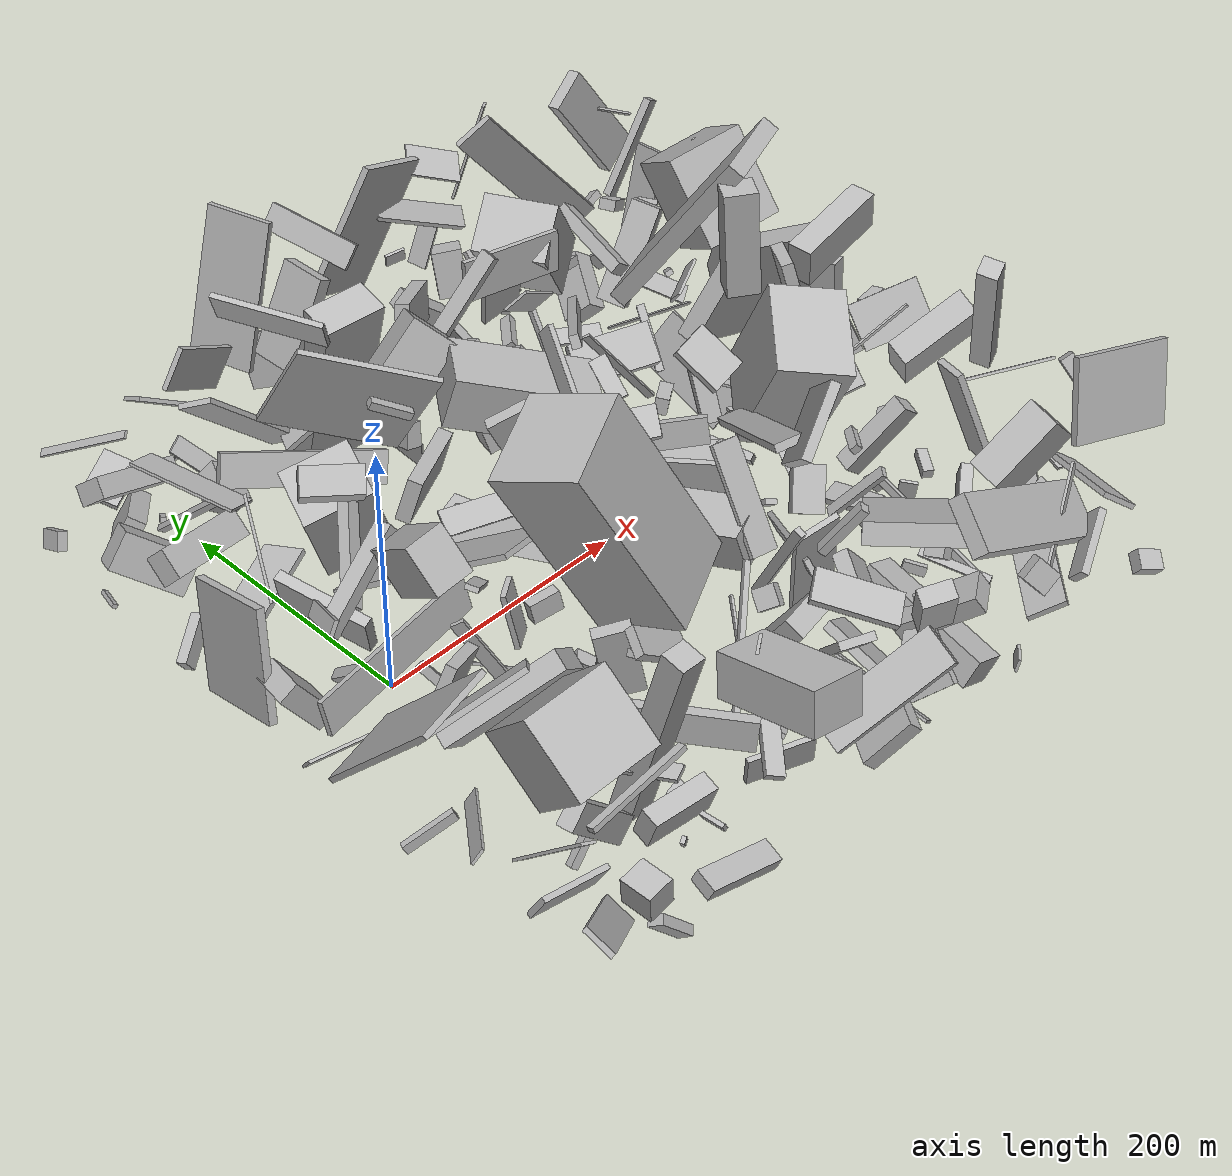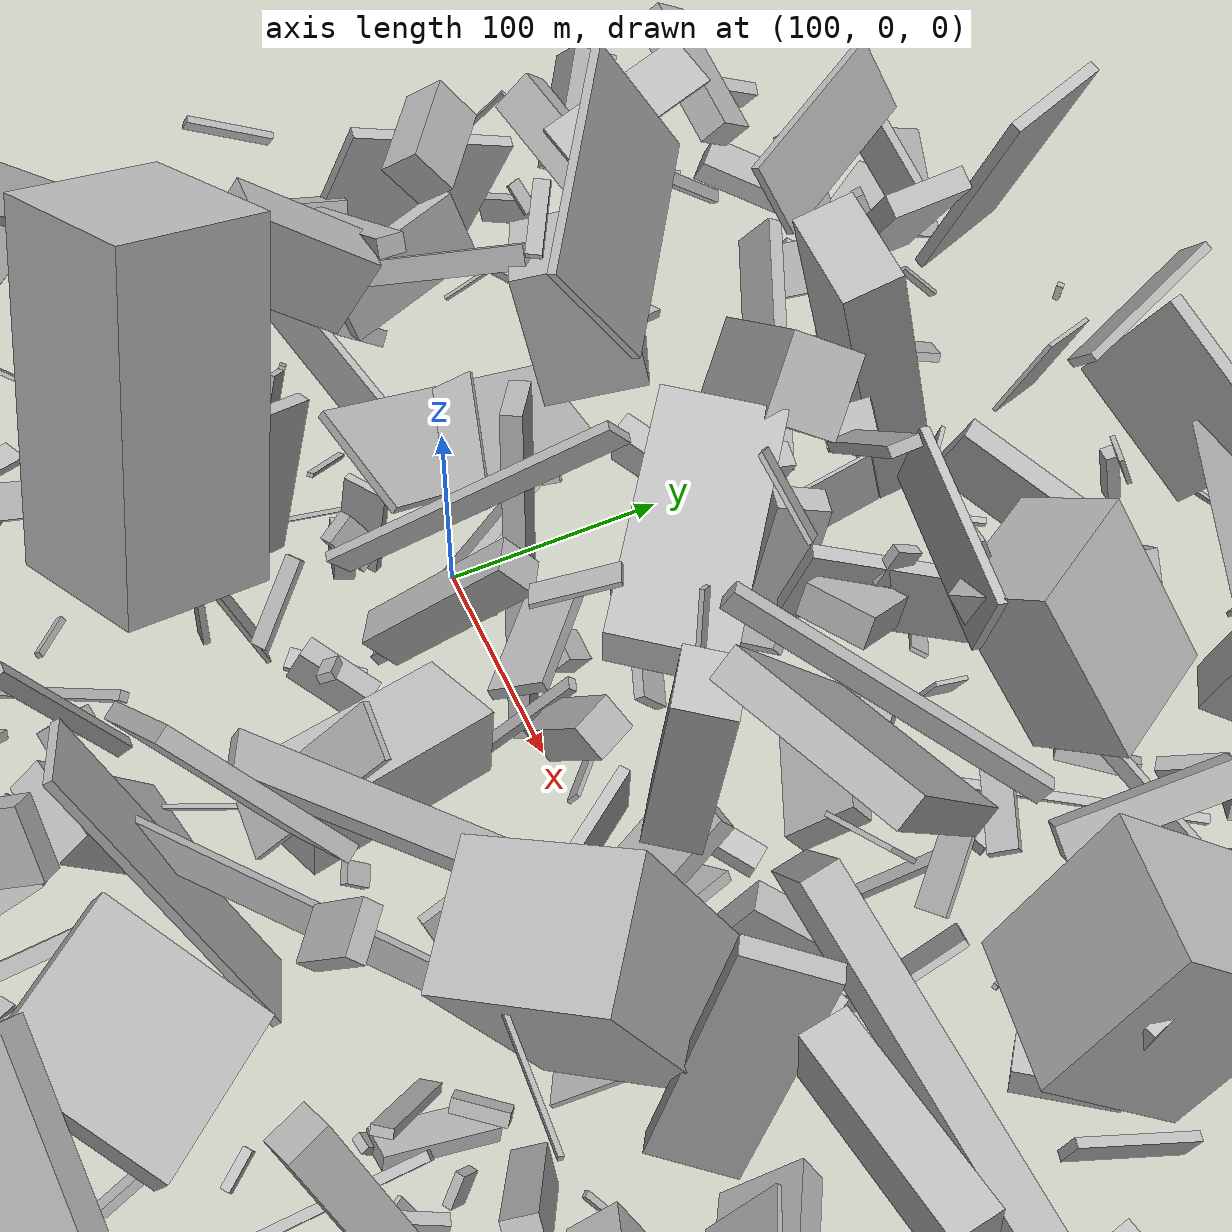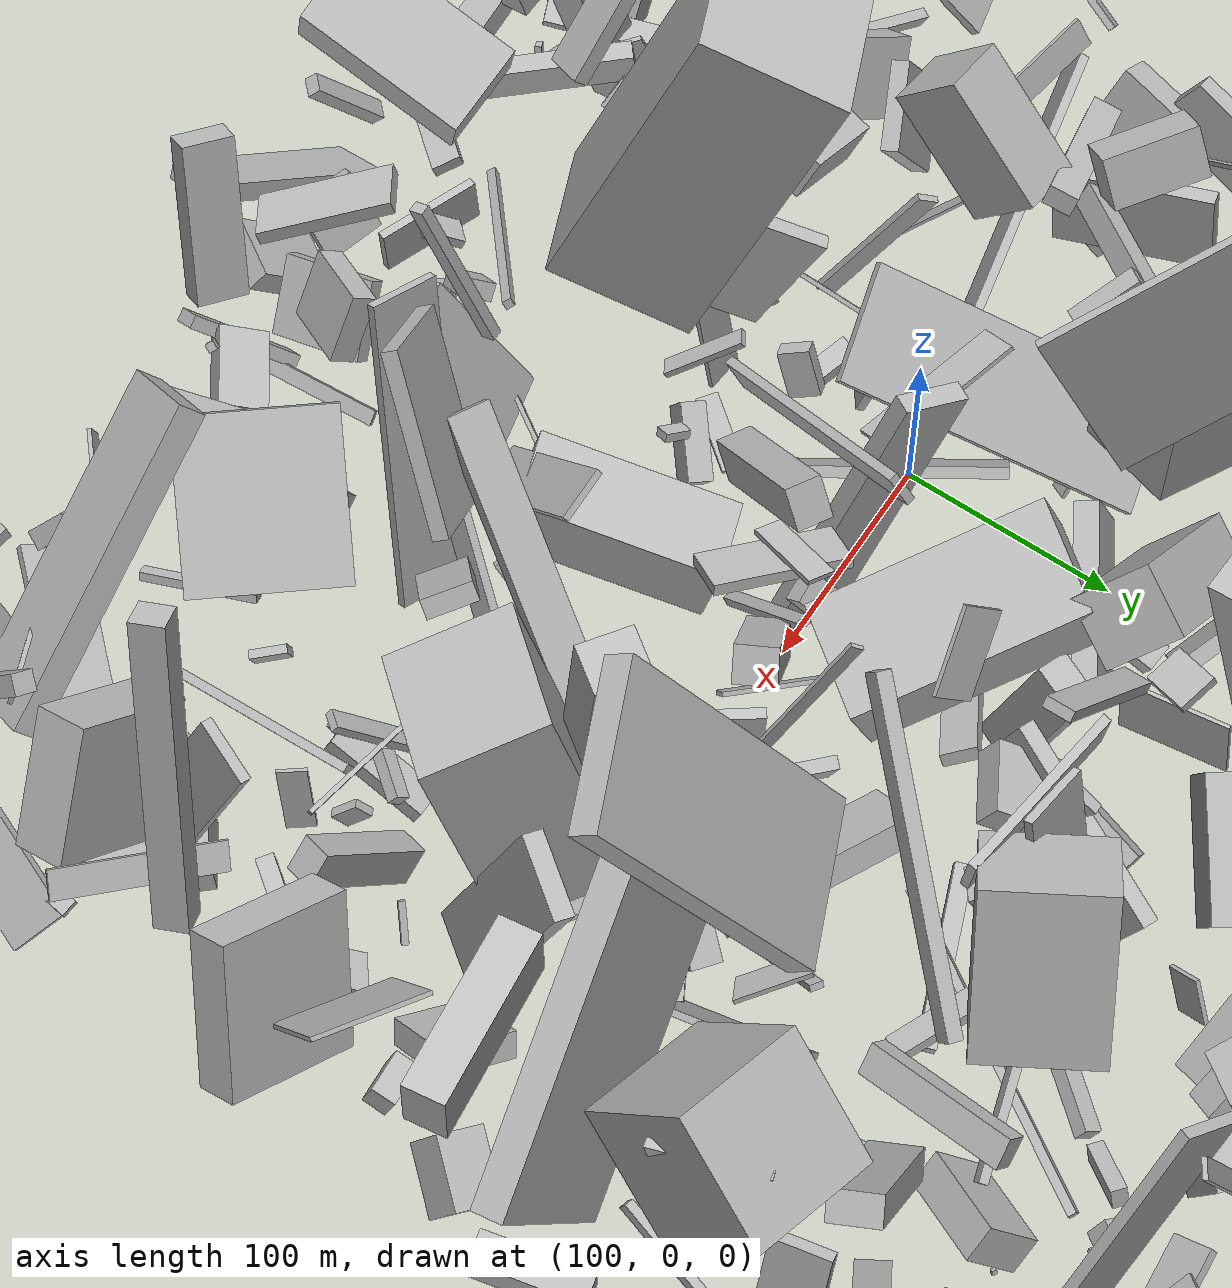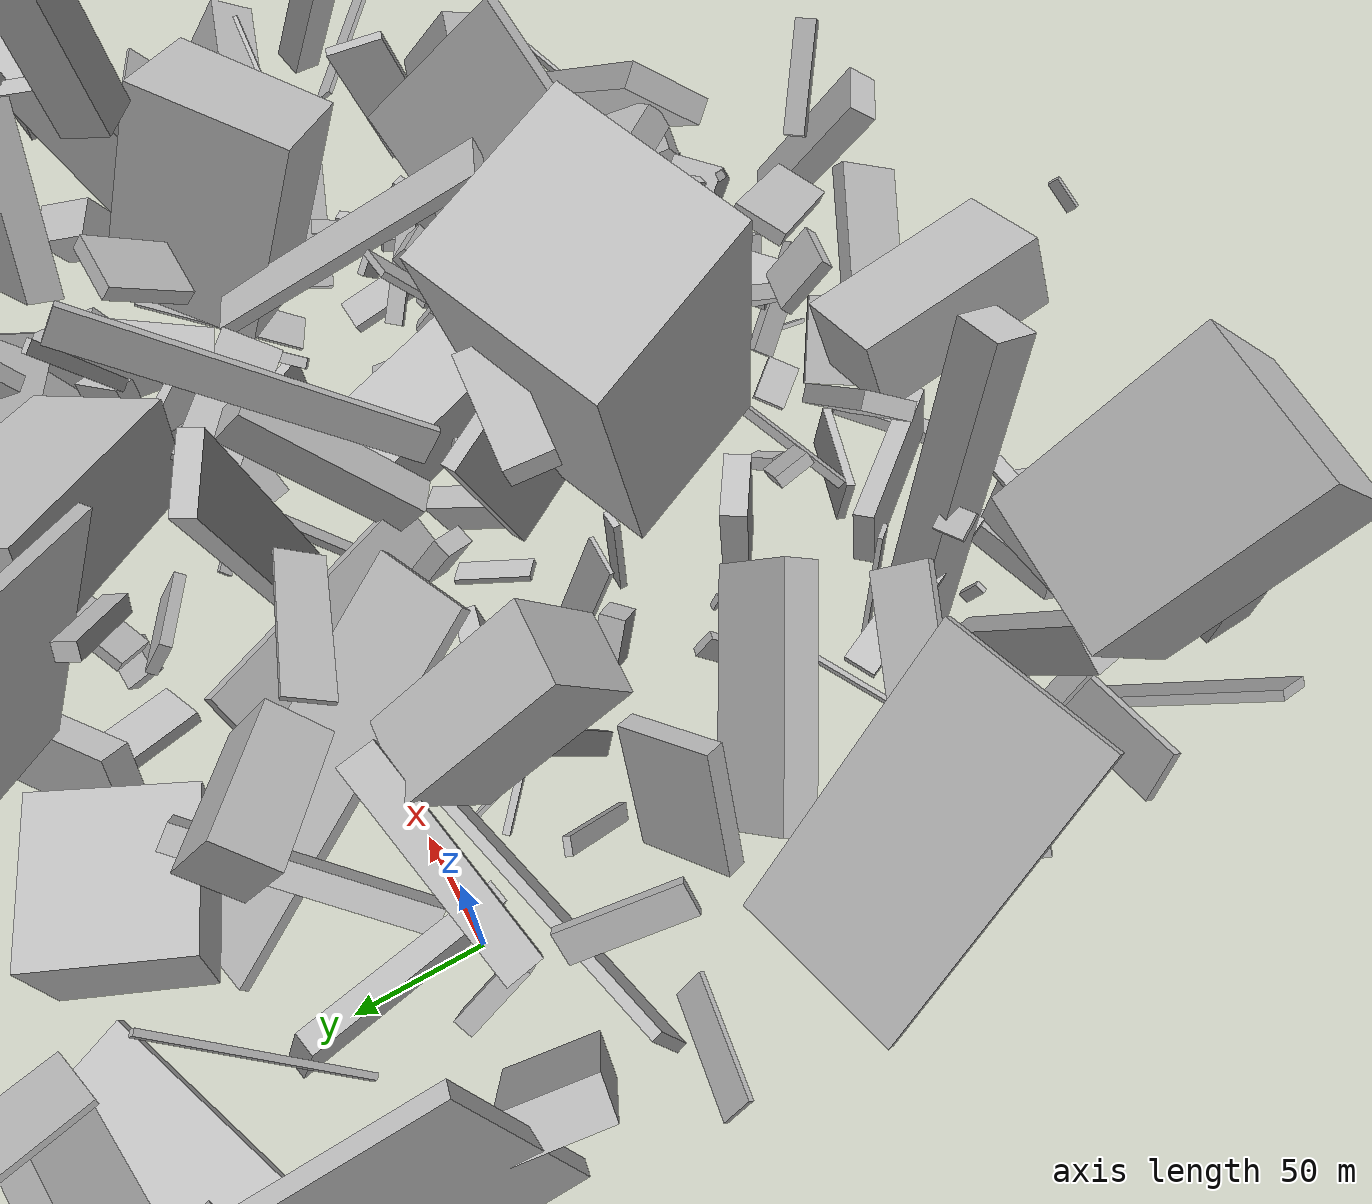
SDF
<sdf version="1.6">
 <world name="default">
  <scene>
   <sky><clouds><speed>12</speed></clouds></sky>
   <ambient>0.4 0.4 0.4 1</ambient>
   <background>0.7 0.7 0.7 1</background>
   <shadows>1</shadows>
  </scene>
  <gravity>0 0 -9.8066</gravity>
  <magnetic_field>6e-06 2.3e-05 -4.2e-05</magnetic_field>
  <physics default="0" name="default_physics" type="ode">
   <ode>
    <solver>
     <type>quick</type>
     <iters>10</iters>
     <sor>1.0</sor>
     <use_dynamic_moi_rescaling>0</use_dynamic_moi_rescaling>
    </solver>
    <constraints>
     <cfm>0</cfm>
     <erp>0.2</erp>
     <contact_max_correcting_vel>100</contact_max_correcting_vel>
     <contact_surface_layer>0.001</contact_surface_layer>
    </constraints>
   </ode>
   <max_step_size>0.004</max_step_size>
   <real_time_factor>1</real_time_factor>
   <real_time_update_rate>250</real_time_update_rate>
  </physics>
  <light name="sun" type="directional">
   <pose>0 0 10 0 0 0</pose>
   <diffuse>0.8 0.8 0.8 1</diffuse>
   <specular>0.2 0.2 0.2 1</specular>
   <attenuation>
    <range>1000</range>
    <constant>0.9</constant>
    <linear>0.01</linear>
    <quadratic>0.001</quadratic>
   </attenuation>
   <direction>-0.5 0.1 -0.9</direction>
  </light>
  <model name="building_1">
   <static>0</static>
   <pose>416.7283779944425 210.92979826897448 18.98239796938811 0.8828051827888167 0.32550872839916073 -2.833453676443939</pose>
   <link name="link">
    <gravity>0</gravity>
    <pose>0 0 6.5 0 0 0</pose>
    <collision name="collision"><geometry><box><size>4 32 13</size></box></geometry></collision>
    <visual name="visual">
     <cast_shadows>0</cast_shadows>
     <geometry><box><size>4 32 13</size></box></geometry>
     <material>
      <script>
       <uri>model://HANNAS_wall/materials/scripts</uri>
       <uri>model://HANNAS_wall/materials/textures</uri>
       <name>vrc/HANNAS_wall</name>
      </script>
     </material>
    </visual>
   </link>
  </model>
  <model name="building_2">
   <static>0</static>
   <pose>-4.265464963011265 -214.34550953891124 35.140416664109665 0.7161109243127337 -0.007068046469748389 -1.4078705098081357</pose>
   <link name="link">
    <gravity>0</gravity>
    <pose>0 0 36.5 0 0 0</pose>
    <collision name="collision"><geometry><box><size>12 20 73</size></box></geometry></collision>
    <visual name="visual">
     <cast_shadows>0</cast_shadows>
     <geometry><box><size>12 20 73</size></box></geometry>
     <material>
      <script>
       <uri>model://HANNAS_wall/materials/scripts</uri>
       <uri>model://HANNAS_wall/materials/textures</uri>
       <name>vrc/HANNAS_wall</name>
      </script>
     </material>
    </visual>
   </link>
  </model>
  <model name="building_3">
   <static>0</static>
   <pose>-55.28225506362537 196.1160932820637 103.23580506193083 2.6990530904863754 -0.6686548601358759 -1.2108224262797935</pose>
   <link name="link">
    <gravity>0</gravity>
    <pose>0 0 7.5 0 0 0</pose>
    <collision name="collision"><geometry><box><size>23 68 15</size></box></geometry></collision>
    <visual name="visual">
     <cast_shadows>0</cast_shadows>
     <geometry><box><size>23 68 15</size></box></geometry>
     <material>
      <script>
       <uri>model://HANNAS_wall/materials/scripts</uri>
       <uri>model://HANNAS_wall/materials/textures</uri>
       <name>vrc/HANNAS_wall</name>
      </script>
     </material>
    </visual>
   </link>
  </model>
  <model name="building_4">
   <static>0</static>
   <pose>182.80358350350366 75.05793901918615 81.25627983369378 0.052977912742376704 -0.2959889521816837 2.4877120915452173</pose>
   <link name="link">
    <gravity>0</gravity>
    <pose>0 0 19.5 0 0 0</pose>
    <collision name="collision"><geometry><box><size>105 52 39</size></box></geometry></collision>
    <visual name="visual">
     <cast_shadows>0</cast_shadows>
     <geometry><box><size>105 52 39</size></box></geometry>
     <material>
      <script>
       <uri>model://HANNAS_wall/materials/scripts</uri>
       <uri>model://HANNAS_wall/materials/textures</uri>
       <name>vrc/HANNAS_wall</name>
      </script>
     </material>
    </visual>
   </link>
  </model>
  <model name="building_5">
   <static>0</static>
   <pose>280.8305112230381 201.21083454206996 117.40529876073163 -1.6112890593165738 -0.9193046591542371 -2.5913730514787088</pose>
   <link name="link">
    <gravity>0</gravity>
    <pose>0 0 27.5 0 0 0</pose>
    <collision name="collision"><geometry><box><size>79 44 55</size></box></geometry></collision>
    <visual name="visual">
     <cast_shadows>0</cast_shadows>
     <geometry><box><size>79 44 55</size></box></geometry>
     <material>
      <script>
       <uri>model://HANNAS_wall/materials/scripts</uri>
       <uri>model://HANNAS_wall/materials/textures</uri>
       <name>vrc/HANNAS_wall</name>
      </script>
     </material>
    </visual>
   </link>
  </model>
  <model name="building_6">
   <static>0</static>
   <pose>282.1729372813604 -36.597284121610826 50.50570288907135 -0.35308780203763046 0.7539027413278987 2.2408650711214086</pose>
   <link name="link">
    <gravity>0</gravity>
    <pose>0 0 2.0 0 0 0</pose>
    <collision name="collision"><geometry><box><size>5 25 4</size></box></geometry></collision>
    <visual name="visual">
     <cast_shadows>0</cast_shadows>
     <geometry><box><size>5 25 4</size></box></geometry>
     <material>
      <script>
       <uri>model://HANNAS_wall/materials/scripts</uri>
       <uri>model://HANNAS_wall/materials/textures</uri>
       <name>vrc/HANNAS_wall</name>
      </script>
     </material>
    </visual>
   </link>
  </model>
  <model name="building_7">
   <static>0</static>
   <pose>321.18293519040907 90.14032634972115 120.52418748455804 0.07833895289617772 -0.5774066002061583 1.9267652480553856</pose>
   <link name="link">
    <gravity>0</gravity>
    <pose>0 0 75.0 0 0 0</pose>
    <collision name="collision"><geometry><box><size>13 71 150</size></box></geometry></collision>
    <visual name="visual">
     <cast_shadows>0</cast_shadows>
     <geometry><box><size>13 71 150</size></box></geometry>
     <material>
      <script>
       <uri>model://HANNAS_wall/materials/scripts</uri>
       <uri>model://HANNAS_wall/materials/textures</uri>
       <name>vrc/HANNAS_wall</name>
      </script>
     </material>
    </visual>
   </link>
  </model>
  <model name="building_8">
   <static>0</static>
   <pose>42.81483554489154 18.11997255370308 60.03226280761964 2.0090533513955946 -0.9623262912604077 1.4473765185540202</pose>
   <link name="link">
    <gravity>0</gravity>
    <pose>0 0 26.5 0 0 0</pose>
    <collision name="collision"><geometry><box><size>4 150 53</size></box></geometry></collision>
    <visual name="visual">
     <cast_shadows>0</cast_shadows>
     <geometry><box><size>4 150 53</size></box></geometry>
     <material>
      <script>
       <uri>model://HANNAS_wall/materials/scripts</uri>
       <uri>model://HANNAS_wall/materials/textures</uri>
       <name>vrc/HANNAS_wall</name>
      </script>
     </material>
    </visual>
   </link>
  </model>
  <model name="building_9">
   <static>0</static>
   <pose>55.40457712910734 117.85381674948677 116.89519842510563 0.4024356207725402 -0.32763654302624207 0.8200217314600851</pose>
   <link name="link">
    <gravity>0</gravity>
    <pose>0 0 43.5 0 0 0</pose>
    <collision name="collision"><geometry><box><size>4 99 87</size></box></geometry></collision>
    <visual name="visual">
     <cast_shadows>0</cast_shadows>
     <geometry><box><size>4 99 87</size></box></geometry>
     <material>
      <script>
       <uri>model://HANNAS_wall/materials/scripts</uri>
       <uri>model://HANNAS_wall/materials/textures</uri>
       <name>vrc/HANNAS_wall</name>
      </script>
     </material>
    </visual>
   </link>
  </model>
  <model name="building_10">
   <static>0</static>
   <pose>460.1589038823998 -118.37427874960508 84.8922860000979 0.4953576849340349 0.12150383040471525 -1.203732286622869</pose>
   <link name="link">
    <gravity>0</gravity>
    <pose>0 0 75.0 0 0 0</pose>
    <collision name="collision"><geometry><box><size>15 14 150</size></box></geometry></collision>
    <visual name="visual">
     <cast_shadows>0</cast_shadows>
     <geometry><box><size>15 14 150</size></box></geometry>
     <material>
      <script>
       <uri>model://HANNAS_wall/materials/scripts</uri>
       <uri>model://HANNAS_wall/materials/textures</uri>
       <name>vrc/HANNAS_wall</name>
      </script>
     </material>
    </visual>
   </link>
  </model>
  <model name="building_11">
   <static>0</static>
   <pose>337.3567182355807 -128.44196132347136 14.974710355389043 -1.0140477747053518 -0.029069397226781417 0.16916619876943415</pose>
   <link name="link">
    <gravity>0</gravity>
    <pose>0 0 2.0 0 0 0</pose>
    <collision name="collision"><geometry><box><size>7 24 4</size></box></geometry></collision>
    <visual name="visual">
     <cast_shadows>0</cast_shadows>
     <geometry><box><size>7 24 4</size></box></geometry>
     <material>
      <script>
       <uri>model://HANNAS_wall/materials/scripts</uri>
       <uri>model://HANNAS_wall/materials/textures</uri>
       <name>vrc/HANNAS_wall</name>
      </script>
     </material>
    </visual>
   </link>
  </model>
  <model name="building_12">
   <static>0</static>
   <pose>154.9563873587294 5.650761414576049 76.65083035795222 1.5159323289314215 0.41175495669101403 2.613163994436163</pose>
   <link name="link">
    <gravity>0</gravity>
    <pose>0 0 4.5 0 0 0</pose>
    <collision name="collision"><geometry><box><size>31 150 9</size></box></geometry></collision>
    <visual name="visual">
     <cast_shadows>0</cast_shadows>
     <geometry><box><size>31 150 9</size></box></geometry>
     <material>
      <script>
       <uri>model://HANNAS_wall/materials/scripts</uri>
       <uri>model://HANNAS_wall/materials/textures</uri>
       <name>vrc/HANNAS_wall</name>
      </script>
     </material>
    </visual>
   </link>
  </model>
  <model name="building_13">
   <static>0</static>
   <pose>305.72085957441516 170.0902135539302 17.677615049925144 2.993033016660117 -1.1944992597726782 -0.42007366668599083</pose>
   <link name="link">
    <gravity>0</gravity>
    <pose>0 0 2.0 0 0 0</pose>
    <collision name="collision"><geometry><box><size>5 150 4</size></box></geometry></collision>
    <visual name="visual">
     <cast_shadows>0</cast_shadows>
     <geometry><box><size>5 150 4</size></box></geometry>
     <material>
      <script>
       <uri>model://HANNAS_wall/materials/scripts</uri>
       <uri>model://HANNAS_wall/materials/textures</uri>
       <name>vrc/HANNAS_wall</name>
      </script>
     </material>
    </visual>
   </link>
  </model>
  <model name="building_14">
   <static>0</static>
   <pose>188.73639514579293 245.0899746348153 124.96272206139946 -1.2908248602176795 0.5753956940945602 0.47916340130765883</pose>
   <link name="link">
    <gravity>0</gravity>
    <pose>0 0 35.0 0 0 0</pose>
    <collision name="collision"><geometry><box><size>4 20 70</size></box></geometry></collision>
    <visual name="visual">
     <cast_shadows>0</cast_shadows>
     <geometry><box><size>4 20 70</size></box></geometry>
     <material>
      <script>
       <uri>model://HANNAS_wall/materials/scripts</uri>
       <uri>model://HANNAS_wall/materials/textures</uri>
       <name>vrc/HANNAS_wall</name>
      </script>
     </material>
    </visual>
   </link>
  </model>
  <model name="building_15">
   <static>0</static>
   <pose>293.0118756271913 4.474258770411966 95.61094297676232 -1.181248603299123 0.5923829690147229 -1.2979223778832998</pose>
   <link name="link">
    <gravity>0</gravity>
    <pose>0 0 14.5 0 0 0</pose>
    <collision name="collision"><geometry><box><size>39 8 29</size></box></geometry></collision>
    <visual name="visual">
     <cast_shadows>0</cast_shadows>
     <geometry><box><size>39 8 29</size></box></geometry>
     <material>
      <script>
       <uri>model://HANNAS_wall/materials/scripts</uri>
       <uri>model://HANNAS_wall/materials/textures</uri>
       <name>vrc/HANNAS_wall</name>
      </script>
     </material>
    </visual>
   </link>
  </model>
  <model name="building_16">
   <static>0</static>
   <pose>411.00323146773076 41.315731008576535 88.35890527292715 1.0472873956849313 1.0478627989128555 2.7460470604189346</pose>
   <link name="link">
    <gravity>0</gravity>
    <pose>0 0 7.5 0 0 0</pose>
    <collision name="collision"><geometry><box><size>83 150 15</size></box></geometry></collision>
    <visual name="visual">
     <cast_shadows>0</cast_shadows>
     <geometry><box><size>83 150 15</size></box></geometry>
     <material>
      <script>
       <uri>model://HANNAS_wall/materials/scripts</uri>
       <uri>model://HANNAS_wall/materials/textures</uri>
       <name>vrc/HANNAS_wall</name>
      </script>
     </material>
    </visual>
   </link>
  </model>
  <model name="building_17">
   <static>0</static>
   <pose>434.11143040964225 -63.23655594382947 62.417099421793985 -0.8089950280004476 -0.8640775364685063 -2.533135403056775</pose>
   <link name="link">
    <gravity>0</gravity>
    <pose>0 0 31.5 0 0 0</pose>
    <collision name="collision"><geometry><box><size>71 20 63</size></box></geometry></collision>
    <visual name="visual">
     <cast_shadows>0</cast_shadows>
     <geometry><box><size>71 20 63</size></box></geometry>
     <material>
      <script>
       <uri>model://HANNAS_wall/materials/scripts</uri>
       <uri>model://HANNAS_wall/materials/textures</uri>
       <name>vrc/HANNAS_wall</name>
      </script>
     </material>
    </visual>
   </link>
  </model>
  <model name="building_18">
   <static>0</static>
   <pose>243.62628033249098 124.98921547650758 24.143643422314117 -1.1151127843351323 -1.0576193037624935 -1.3002501609556982</pose>
   <link name="link">
    <gravity>0</gravity>
    <pose>0 0 8.5 0 0 0</pose>
    <collision name="collision"><geometry><box><size>6 15 17</size></box></geometry></collision>
    <visual name="visual">
     <cast_shadows>0</cast_shadows>
     <geometry><box><size>6 15 17</size></box></geometry>
     <material>
      <script>
       <uri>model://HANNAS_wall/materials/scripts</uri>
       <uri>model://HANNAS_wall/materials/textures</uri>
       <name>vrc/HANNAS_wall</name>
      </script>
     </material>
    </visual>
   </link>
  </model>
  <model name="building_19">
   <static>0</static>
   <pose>201.0057819521384 -11.097750578075441 28.199697078443496 1.6185561497208243 0.8543579153049004 -1.8676976375479786</pose>
   <link name="link">
    <gravity>0</gravity>
    <pose>0 0 3.0 0 0 0</pose>
    <collision name="collision"><geometry><box><size>69 4 6</size></box></geometry></collision>
    <visual name="visual">
     <cast_shadows>0</cast_shadows>
     <geometry><box><size>69 4 6</size></box></geometry>
     <material>
      <script>
       <uri>model://HANNAS_wall/materials/scripts</uri>
       <uri>model://HANNAS_wall/materials/textures</uri>
       <name>vrc/HANNAS_wall</name>
      </script>
     </material>
    </visual>
   </link>
  </model>
  <model name="building_20">
   <static>0</static>
   <pose>333.15024526978425 -112.29790113569715 32.963723524804394 2.294804269821696 -0.13437746674991374 0.8997554417228535</pose>
   <link name="link">
    <gravity>0</gravity>
    <pose>0 0 2.0 0 0 0</pose>
    <collision name="collision"><geometry><box><size>9 53 4</size></box></geometry></collision>
    <visual name="visual">
     <cast_shadows>0</cast_shadows>
     <geometry><box><size>9 53 4</size></box></geometry>
     <material>
      <script>
       <uri>model://HANNAS_wall/materials/scripts</uri>
       <uri>model://HANNAS_wall/materials/textures</uri>
       <name>vrc/HANNAS_wall</name>
      </script>
     </material>
    </visual>
   </link>
  </model>
  <model name="building_21">
   <static>0</static>
   <pose>8.457655197368247 -112.51763174960851 65.24477038749917 0.6654835469640487 -0.5815607926443658 -0.557341626577998</pose>
   <link name="link">
    <gravity>0</gravity>
    <pose>0 0 18.0 0 0 0</pose>
    <collision name="collision"><geometry><box><size>93 15 36</size></box></geometry></collision>
    <visual name="visual">
     <cast_shadows>0</cast_shadows>
     <geometry><box><size>93 15 36</size></box></geometry>
     <material>
      <script>
       <uri>model://HANNAS_wall/materials/scripts</uri>
       <uri>model://HANNAS_wall/materials/textures</uri>
       <name>vrc/HANNAS_wall</name>
      </script>
     </material>
    </visual>
   </link>
  </model>
  <model name="building_22">
   <static>0</static>
   <pose>-9.055808616856012 -22.570312768813796 37.857318943666606 -0.3160825522196778 0.05846673091310445 0.19661354772006312</pose>
   <link name="link">
    <gravity>0</gravity>
    <pose>0 0 12.5 0 0 0</pose>
    <collision name="collision"><geometry><box><size>150 4 25</size></box></geometry></collision>
    <visual name="visual">
     <cast_shadows>0</cast_shadows>
     <geometry><box><size>150 4 25</size></box></geometry>
     <material>
      <script>
       <uri>model://HANNAS_wall/materials/scripts</uri>
       <uri>model://HANNAS_wall/materials/textures</uri>
       <name>vrc/HANNAS_wall</name>
      </script>
     </material>
    </visual>
   </link>
  </model>
  <model name="building_23">
   <static>0</static>
   <pose>98.3337527439675 45.10996295531062 53.80040420355921 1.6647293245427262 -0.9957674719654037 0.4722553468294991</pose>
   <link name="link">
    <gravity>0</gravity>
    <pose>0 0 56.5 0 0 0</pose>
    <collision name="collision"><geometry><box><size>27 5 113</size></box></geometry></collision>
    <visual name="visual">
     <cast_shadows>0</cast_shadows>
     <geometry><box><size>27 5 113</size></box></geometry>
     <material>
      <script>
       <uri>model://HANNAS_wall/materials/scripts</uri>
       <uri>model://HANNAS_wall/materials/textures</uri>
       <name>vrc/HANNAS_wall</name>
      </script>
     </material>
    </visual>
   </link>
  </model>
  <model name="building_24">
   <static>0</static>
   <pose>184.79832759941667 49.655573684571976 28.877530848192748 2.5118512099150387 -0.18689642946880644 2.784816964141763</pose>
   <link name="link">
    <gravity>0</gravity>
    <pose>0 0 8.5 0 0 0</pose>
    <collision name="collision"><geometry><box><size>45 5 17</size></box></geometry></collision>
    <visual name="visual">
     <cast_shadows>0</cast_shadows>
     <geometry><box><size>45 5 17</size></box></geometry>
     <material>
      <script>
       <uri>model://HANNAS_wall/materials/scripts</uri>
       <uri>model://HANNAS_wall/materials/textures</uri>
       <name>vrc/HANNAS_wall</name>
      </script>
     </material>
    </visual>
   </link>
  </model>
  <model name="building_25">
   <static>0</static>
   <pose>32.33401957300136 238.51472650263446 98.40388044989416 -0.5680434460506295 0.11449184152743144 -1.4145679435280494</pose>
   <link name="link">
    <gravity>0</gravity>
    <pose>0 0 16.0 0 0 0</pose>
    <collision name="collision"><geometry><box><size>4 59 32</size></box></geometry></collision>
    <visual name="visual">
     <cast_shadows>0</cast_shadows>
     <geometry><box><size>4 59 32</size></box></geometry>
     <material>
      <script>
       <uri>model://HANNAS_wall/materials/scripts</uri>
       <uri>model://HANNAS_wall/materials/textures</uri>
       <name>vrc/HANNAS_wall</name>
      </script>
     </material>
    </visual>
   </link>
  </model>
  <model name="building_26">
   <static>0</static>
   <pose>197.83947046262287 277.53757635408533 73.37467138632931 0.2440378320414543 0.4236065094169859 0.26116944950718446</pose>
   <link name="link">
    <gravity>0</gravity>
    <pose>0 0 54.5 0 0 0</pose>
    <collision name="collision"><geometry><box><size>70 5 109</size></box></geometry></collision>
    <visual name="visual">
     <cast_shadows>0</cast_shadows>
     <geometry><box><size>70 5 109</size></box></geometry>
     <material>
      <script>
       <uri>model://HANNAS_wall/materials/scripts</uri>
       <uri>model://HANNAS_wall/materials/textures</uri>
       <name>vrc/HANNAS_wall</name>
      </script>
     </material>
    </visual>
   </link>
  </model>
  <model name="building_27">
   <static>0</static>
   <pose>-58.411665902401865 201.56083246318798 39.52666035498493 -1.8922600408789696 0.49958050123174225 -0.8573434355961012</pose>
   <link name="link">
    <gravity>0</gravity>
    <pose>0 0 24.5 0 0 0</pose>
    <collision name="collision"><geometry><box><size>14 32 49</size></box></geometry></collision>
    <visual name="visual">
     <cast_shadows>0</cast_shadows>
     <geometry><box><size>14 32 49</size></box></geometry>
     <material>
      <script>
       <uri>model://HANNAS_wall/materials/scripts</uri>
       <uri>model://HANNAS_wall/materials/textures</uri>
       <name>vrc/HANNAS_wall</name>
      </script>
     </material>
    </visual>
   </link>
  </model>
  <model name="building_28">
   <static>0</static>
   <pose>235.4168713873661 -254.85683032448424 34.52441124242624 -0.36384586400319685 -0.01920707055681753 0.6055306552748823</pose>
   <link name="link">
    <gravity>0</gravity>
    <pose>0 0 6.5 0 0 0</pose>
    <collision name="collision"><geometry><box><size>38 22 13</size></box></geometry></collision>
    <visual name="visual">
     <cast_shadows>0</cast_shadows>
     <geometry><box><size>38 22 13</size></box></geometry>
     <material>
      <script>
       <uri>model://HANNAS_wall/materials/scripts</uri>
       <uri>model://HANNAS_wall/materials/textures</uri>
       <name>vrc/HANNAS_wall</name>
      </script>
     </material>
    </visual>
   </link>
  </model>
  <model name="building_29">
   <static>0</static>
   <pose>388.6430166010418 163.41789401701087 66.54947921734367 -2.8306492783292816 -0.9800535455750119 0.1352461155828603</pose>
   <link name="link">
    <gravity>0</gravity>
    <pose>0 0 7.0 0 0 0</pose>
    <collision name="collision"><geometry><box><size>80 23 14</size></box></geometry></collision>
    <visual name="visual">
     <cast_shadows>0</cast_shadows>
     <geometry><box><size>80 23 14</size></box></geometry>
     <material>
      <script>
       <uri>model://HANNAS_wall/materials/scripts</uri>
       <uri>model://HANNAS_wall/materials/textures</uri>
       <name>vrc/HANNAS_wall</name>
      </script>
     </material>
    </visual>
   </link>
  </model>
  <model name="building_30">
   <static>0</static>
   <pose>117.10664770685433 -130.943974789597 100.99099463609906 0.2889966119366335 -0.3691784653962624 -1.268954633508064</pose>
   <link name="link">
    <gravity>0</gravity>
    <pose>0 0 75.0 0 0 0</pose>
    <collision name="collision"><geometry><box><size>66 68 150</size></box></geometry></collision>
    <visual name="visual">
     <cast_shadows>0</cast_shadows>
     <geometry><box><size>66 68 150</size></box></geometry>
     <material>
      <script>
       <uri>model://HANNAS_wall/materials/scripts</uri>
       <uri>model://HANNAS_wall/materials/textures</uri>
       <name>vrc/HANNAS_wall</name>
      </script>
     </material>
    </visual>
   </link>
  </model>
  <model name="building_31">
   <static>0</static>
   <pose>317.9822952073156 -175.98219931909975 65.68136350137047 0.08949255306956216 1.0632707284871563 -2.366867553119166</pose>
   <link name="link">
    <gravity>0</gravity>
    <pose>0 0 37.5 0 0 0</pose>
    <collision name="collision"><geometry><box><size>16 70 75</size></box></geometry></collision>
    <visual name="visual">
     <cast_shadows>0</cast_shadows>
     <geometry><box><size>16 70 75</size></box></geometry>
     <material>
      <script>
       <uri>model://HANNAS_wall/materials/scripts</uri>
       <uri>model://HANNAS_wall/materials/textures</uri>
       <name>vrc/HANNAS_wall</name>
      </script>
     </material>
    </visual>
   </link>
  </model>
  <model name="building_32">
   <static>0</static>
   <pose>44.03630529259533 -130.80900042439174 38.514397665553915 -1.5089520208758345 -0.6667997113792358 1.2417032428408032</pose>
   <link name="link">
    <gravity>0</gravity>
    <pose>0 0 2.0 0 0 0</pose>
    <collision name="collision"><geometry><box><size>25 11 4</size></box></geometry></collision>
    <visual name="visual">
     <cast_shadows>0</cast_shadows>
     <geometry><box><size>25 11 4</size></box></geometry>
     <material>
      <script>
       <uri>model://HANNAS_wall/materials/scripts</uri>
       <uri>model://HANNAS_wall/materials/textures</uri>
       <name>vrc/HANNAS_wall</name>
      </script>
     </material>
    </visual>
   </link>
  </model>
  <model name="building_33">
   <static>0</static>
   <pose>239.7932896995171 194.93084295848075 42.291740489335425 -0.0018048737827131515 -1.300802228745326 1.159511638491516</pose>
   <link name="link">
    <gravity>0</gravity>
    <pose>0 0 47.0 0 0 0</pose>
    <collision name="collision"><geometry><box><size>41 7 94</size></box></geometry></collision>
    <visual name="visual">
     <cast_shadows>0</cast_shadows>
     <geometry><box><size>41 7 94</size></box></geometry>
     <material>
      <script>
       <uri>model://HANNAS_wall/materials/scripts</uri>
       <uri>model://HANNAS_wall/materials/textures</uri>
       <name>vrc/HANNAS_wall</name>
      </script>
     </material>
    </visual>
   </link>
  </model>
  <model name="building_34">
   <static>0</static>
   <pose>457.249233680536 230.10714518390355 50.29948453529093 1.4610760816705493 0.3465931190292476 -0.05478114516371952</pose>
   <link name="link">
    <gravity>0</gravity>
    <pose>0 0 14.0 0 0 0</pose>
    <collision name="collision"><geometry><box><size>4 91 28</size></box></geometry></collision>
    <visual name="visual">
     <cast_shadows>0</cast_shadows>
     <geometry><box><size>4 91 28</size></box></geometry>
     <material>
      <script>
       <uri>model://HANNAS_wall/materials/scripts</uri>
       <uri>model://HANNAS_wall/materials/textures</uri>
       <name>vrc/HANNAS_wall</name>
      </script>
     </material>
    </visual>
   </link>
  </model>
  <model name="building_35">
   <static>0</static>
   <pose>211.60376427736364 -220.27905017314177 101.85397670175263 2.5157299335138896 -0.8857009079345143 -3.1245915232860106</pose>
   <link name="link">
    <gravity>0</gravity>
    <pose>0 0 5.5 0 0 0</pose>
    <collision name="collision"><geometry><box><size>31 36 11</size></box></geometry></collision>
    <visual name="visual">
     <cast_shadows>0</cast_shadows>
     <geometry><box><size>31 36 11</size></box></geometry>
     <material>
      <script>
       <uri>model://HANNAS_wall/materials/scripts</uri>
       <uri>model://HANNAS_wall/materials/textures</uri>
       <name>vrc/HANNAS_wall</name>
      </script>
     </material>
    </visual>
   </link>
  </model>
  <model name="building_36">
   <static>0</static>
   <pose>457.0760395988106 278.03870297747267 100.75126773818518 1.3999977492001678 -0.5422269586380859 0.1986078250218042</pose>
   <link name="link">
    <gravity>0</gravity>
    <pose>0 0 5.0 0 0 0</pose>
    <collision name="collision"><geometry><box><size>34 93 10</size></box></geometry></collision>
    <visual name="visual">
     <cast_shadows>0</cast_shadows>
     <geometry><box><size>34 93 10</size></box></geometry>
     <material>
      <script>
       <uri>model://HANNAS_wall/materials/scripts</uri>
       <uri>model://HANNAS_wall/materials/textures</uri>
       <name>vrc/HANNAS_wall</name>
      </script>
     </material>
    </visual>
   </link>
  </model>
  <model name="building_37">
   <static>0</static>
   <pose>379.0592005224741 -23.764757103029154 96.92471146740642 1.7718425149192778 0.2510704126976804 2.56736003662285</pose>
   <link name="link">
    <gravity>0</gravity>
    <pose>0 0 18.0 0 0 0</pose>
    <collision name="collision"><geometry><box><size>9 117 36</size></box></geometry></collision>
    <visual name="visual">
     <cast_shadows>0</cast_shadows>
     <geometry><box><size>9 117 36</size></box></geometry>
     <material>
      <script>
       <uri>model://HANNAS_wall/materials/scripts</uri>
       <uri>model://HANNAS_wall/materials/textures</uri>
       <name>vrc/HANNAS_wall</name>
      </script>
     </material>
    </visual>
   </link>
  </model>
  <model name="building_38">
   <static>0</static>
   <pose>350.74937876614905 -162.99741595947287 20.990769054794832 1.8768345951856005 -0.2834568657458699 1.5121940201019815</pose>
   <link name="link">
    <gravity>0</gravity>
    <pose>0 0 2.0 0 0 0</pose>
    <collision name="collision"><geometry><box><size>106 6 4</size></box></geometry></collision>
    <visual name="visual">
     <cast_shadows>0</cast_shadows>
     <geometry><box><size>106 6 4</size></box></geometry>
     <material>
      <script>
       <uri>model://HANNAS_wall/materials/scripts</uri>
       <uri>model://HANNAS_wall/materials/textures</uri>
       <name>vrc/HANNAS_wall</name>
      </script>
     </material>
    </visual>
   </link>
  </model>
  <model name="building_39">
   <static>0</static>
   <pose>442.8398557383572 117.53490383616747 67.34212026707625 1.6865817141151425 0.20395103959422184 -0.6415227648487057</pose>
   <link name="link">
    <gravity>0</gravity>
    <pose>0 0 20.0 0 0 0</pose>
    <collision name="collision"><geometry><box><size>14 35 40</size></box></geometry></collision>
    <visual name="visual">
     <cast_shadows>0</cast_shadows>
     <geometry><box><size>14 35 40</size></box></geometry>
     <material>
      <script>
       <uri>model://HANNAS_wall/materials/scripts</uri>
       <uri>model://HANNAS_wall/materials/textures</uri>
       <name>vrc/HANNAS_wall</name>
      </script>
     </material>
    </visual>
   </link>
  </model>
  <model name="building_40">
   <static>0</static>
   <pose>14.613063417208839 99.97085694323675 71.01280587332714 1.292325298984231 -0.21804532078687464 1.227320973306203</pose>
   <link name="link">
    <gravity>0</gravity>
    <pose>0 0 25.5 0 0 0</pose>
    <collision name="collision"><geometry><box><size>48 66 51</size></box></geometry></collision>
    <visual name="visual">
     <cast_shadows>0</cast_shadows>
     <geometry><box><size>48 66 51</size></box></geometry>
     <material>
      <script>
       <uri>model://HANNAS_wall/materials/scripts</uri>
       <uri>model://HANNAS_wall/materials/textures</uri>
       <name>vrc/HANNAS_wall</name>
      </script>
     </material>
    </visual>
   </link>
  </model>
  <model name="building_41">
   <static>0</static>
   <pose>17.09584221940473 204.33313077075593 28.518339037300265 -0.7075024303104669 0.24100345131429876 -1.9526094129967237</pose>
   <link name="link">
    <gravity>0</gravity>
    <pose>0 0 10.5 0 0 0</pose>
    <collision name="collision"><geometry><box><size>28 25 21</size></box></geometry></collision>
    <visual name="visual">
     <cast_shadows>0</cast_shadows>
     <geometry><box><size>28 25 21</size></box></geometry>
     <material>
      <script>
       <uri>model://HANNAS_wall/materials/scripts</uri>
       <uri>model://HANNAS_wall/materials/textures</uri>
       <name>vrc/HANNAS_wall</name>
      </script>
     </material>
    </visual>
   </link>
  </model>
  <model name="building_42">
   <static>0</static>
   <pose>192.7157213353048 124.85466945350338 59.49780146099603 1.3628262631185555 -0.24540779238882335 -0.31049480690275455</pose>
   <link name="link">
    <gravity>0</gravity>
    <pose>0 0 11.5 0 0 0</pose>
    <collision name="collision"><geometry><box><size>15 64 23</size></box></geometry></collision>
    <visual name="visual">
     <cast_shadows>0</cast_shadows>
     <geometry><box><size>15 64 23</size></box></geometry>
     <material>
      <script>
       <uri>model://HANNAS_wall/materials/scripts</uri>
       <uri>model://HANNAS_wall/materials/textures</uri>
       <name>vrc/HANNAS_wall</name>
      </script>
     </material>
    </visual>
   </link>
  </model>
  <model name="building_43">
   <static>0</static>
   <pose>355.7081413751066 -226.23785685120248 91.65332476563502 -2.2603713731433333 -0.4976184332705186 -3.1124423480379075</pose>
   <link name="link">
    <gravity>0</gravity>
    <pose>0 0 21.0 0 0 0</pose>
    <collision name="collision"><geometry><box><size>150 13 42</size></box></geometry></collision>
    <visual name="visual">
     <cast_shadows>0</cast_shadows>
     <geometry><box><size>150 13 42</size></box></geometry>
     <material>
      <script>
       <uri>model://HANNAS_wall/materials/scripts</uri>
       <uri>model://HANNAS_wall/materials/textures</uri>
       <name>vrc/HANNAS_wall</name>
      </script>
     </material>
    </visual>
   </link>
  </model>
  <model name="building_44">
   <static>0</static>
   <pose>144.52448925676998 187.8369770817975 83.63253837687924 1.557518617228997 0.25014867683263464 -1.6345504022708854</pose>
   <link name="link">
    <gravity>0</gravity>
    <pose>0 0 24.5 0 0 0</pose>
    <collision name="collision"><geometry><box><size>27 150 49</size></box></geometry></collision>
    <visual name="visual">
     <cast_shadows>0</cast_shadows>
     <geometry><box><size>27 150 49</size></box></geometry>
     <material>
      <script>
       <uri>model://HANNAS_wall/materials/scripts</uri>
       <uri>model://HANNAS_wall/materials/textures</uri>
       <name>vrc/HANNAS_wall</name>
      </script>
     </material>
    </visual>
   </link>
  </model>
  <model name="building_45">
   <static>0</static>
   <pose>71.7340550363893 171.9143882764367 42.41271891080815 0.5395945788814563 -0.9973067526005303 0.6979869216116512</pose>
   <link name="link">
    <gravity>0</gravity>
    <pose>0 0 3.5 0 0 0</pose>
    <collision name="collision"><geometry><box><size>25 124 7</size></box></geometry></collision>
    <visual name="visual">
     <cast_shadows>0</cast_shadows>
     <geometry><box><size>25 124 7</size></box></geometry>
     <material>
      <script>
       <uri>model://HANNAS_wall/materials/scripts</uri>
       <uri>model://HANNAS_wall/materials/textures</uri>
       <name>vrc/HANNAS_wall</name>
      </script>
     </material>
    </visual>
   </link>
  </model>
  <model name="building_46">
   <static>0</static>
   <pose>457.6577896727 179.8000820094232 74.88433627355745 1.6225985377909675 -0.5171672315456065 0.15397538739588865</pose>
   <link name="link">
    <gravity>0</gravity>
    <pose>0 0 13.0 0 0 0</pose>
    <collision name="collision"><geometry><box><size>6 76 26</size></box></geometry></collision>
    <visual name="visual">
     <cast_shadows>0</cast_shadows>
     <geometry><box><size>6 76 26</size></box></geometry>
     <material>
      <script>
       <uri>model://HANNAS_wall/materials/scripts</uri>
       <uri>model://HANNAS_wall/materials/textures</uri>
       <name>vrc/HANNAS_wall</name>
      </script>
     </material>
    </visual>
   </link>
  </model>
  <model name="building_47">
   <static>0</static>
   <pose>215.18493710199056 -271.1913612932907 27.47882116841408 0.8415555651585404 -0.47683476521809753 -3.0370207028058096</pose>
   <link name="link">
    <gravity>0</gravity>
    <pose>0 0 6.0 0 0 0</pose>
    <collision name="collision"><geometry><box><size>6 56 12</size></box></geometry></collision>
    <visual name="visual">
     <cast_shadows>0</cast_shadows>
     <geometry><box><size>6 56 12</size></box></geometry>
     <material>
      <script>
       <uri>model://HANNAS_wall/materials/scripts</uri>
       <uri>model://HANNAS_wall/materials/textures</uri>
       <name>vrc/HANNAS_wall</name>
      </script>
     </material>
    </visual>
   </link>
  </model>
  <model name="building_48">
   <static>0</static>
   <pose>212.4891290769429 -77.7635215359557 41.445633553725614 -0.2246477361260205 -0.1491714450515656 0.3354588442186512</pose>
   <link name="link">
    <gravity>0</gravity>
    <pose>0 0 16.0 0 0 0</pose>
    <collision name="collision"><geometry><box><size>38 89 32</size></box></geometry></collision>
    <visual name="visual">
     <cast_shadows>0</cast_shadows>
     <geometry><box><size>38 89 32</size></box></geometry>
     <material>
      <script>
       <uri>model://HANNAS_wall/materials/scripts</uri>
       <uri>model://HANNAS_wall/materials/textures</uri>
       <name>vrc/HANNAS_wall</name>
      </script>
     </material>
    </visual>
   </link>
  </model>
  <model name="building_49">
   <static>0</static>
   <pose>245.2291191876191 -126.56439494210305 57.91796113523763 -2.68325481329737 -0.5180728698786812 -2.243137083573296</pose>
   <link name="link">
    <gravity>0</gravity>
    <pose>0 0 7.0 0 0 0</pose>
    <collision name="collision"><geometry><box><size>150 4 14</size></box></geometry></collision>
    <visual name="visual">
     <cast_shadows>0</cast_shadows>
     <geometry><box><size>150 4 14</size></box></geometry>
     <material>
      <script>
       <uri>model://HANNAS_wall/materials/scripts</uri>
       <uri>model://HANNAS_wall/materials/textures</uri>
       <name>vrc/HANNAS_wall</name>
      </script>
     </material>
    </visual>
   </link>
  </model>
  <model name="building_50">
   <static>0</static>
   <pose>247.29898616097603 -253.99254294254627 90.68106334943234 -2.4298114748262445 -0.8616706706315591 0.3567352662043618</pose>
   <link name="link">
    <gravity>0</gravity>
    <pose>0 0 2.0 0 0 0</pose>
    <collision name="collision"><geometry><box><size>4 4 4</size></box></geometry></collision>
    <visual name="visual">
     <cast_shadows>0</cast_shadows>
     <geometry><box><size>4 4 4</size></box></geometry>
     <material>
      <script>
       <uri>model://HANNAS_wall/materials/scripts</uri>
       <uri>model://HANNAS_wall/materials/textures</uri>
       <name>vrc/HANNAS_wall</name>
      </script>
     </material>
    </visual>
   </link>
  </model>
  <model name="building_51">
   <static>0</static>
   <pose>264.733221526885 172.36234834176554 75.37040072782904 0.32428243443624716 -0.2107488211431847 -0.09069788870111702</pose>
   <link name="link">
    <gravity>0</gravity>
    <pose>0 0 37.0 0 0 0</pose>
    <collision name="collision"><geometry><box><size>33 4 74</size></box></geometry></collision>
    <visual name="visual">
     <cast_shadows>0</cast_shadows>
     <geometry><box><size>33 4 74</size></box></geometry>
     <material>
      <script>
       <uri>model://HANNAS_wall/materials/scripts</uri>
       <uri>model://HANNAS_wall/materials/textures</uri>
       <name>vrc/HANNAS_wall</name>
      </script>
     </material>
    </visual>
   </link>
  </model>
  <model name="building_52">
   <static>0</static>
   <pose>318.7343422818073 -66.29008827937255 88.95688643740255 0.5230986797730359 1.1464093705336198 1.410003238743652</pose>
   <link name="link">
    <gravity>0</gravity>
    <pose>0 0 34.5 0 0 0</pose>
    <collision name="collision"><geometry><box><size>99 56 69</size></box></geometry></collision>
    <visual name="visual">
     <cast_shadows>0</cast_shadows>
     <geometry><box><size>99 56 69</size></box></geometry>
     <material>
      <script>
       <uri>model://HANNAS_wall/materials/scripts</uri>
       <uri>model://HANNAS_wall/materials/textures</uri>
       <name>vrc/HANNAS_wall</name>
      </script>
     </material>
    </visual>
   </link>
  </model>
  <model name="building_53">
   <static>0</static>
   <pose>8.089260865041593 -41.882839322425546 114.44893457125949 0.2383154916501212 -0.680165497755677 -1.790175711627763</pose>
   <link name="link">
    <gravity>0</gravity>
    <pose>0 0 18.5 0 0 0</pose>
    <collision name="collision"><geometry><box><size>63 29 37</size></box></geometry></collision>
    <visual name="visual">
     <cast_shadows>0</cast_shadows>
     <geometry><box><size>63 29 37</size></box></geometry>
     <material>
      <script>
       <uri>model://HANNAS_wall/materials/scripts</uri>
       <uri>model://HANNAS_wall/materials/textures</uri>
       <name>vrc/HANNAS_wall</name>
      </script>
     </material>
    </visual>
   </link>
  </model>
  <model name="building_54">
   <static>0</static>
   <pose>134.03059115076852 -218.70502664564117 59.70933349383591 0.9904791006068053 -0.922460166087802 2.853701856156002</pose>
   <link name="link">
    <gravity>0</gravity>
    <pose>0 0 7.0 0 0 0</pose>
    <collision name="collision"><geometry><box><size>4 19 14</size></box></geometry></collision>
    <visual name="visual">
     <cast_shadows>0</cast_shadows>
     <geometry><box><size>4 19 14</size></box></geometry>
     <material>
      <script>
       <uri>model://HANNAS_wall/materials/scripts</uri>
       <uri>model://HANNAS_wall/materials/textures</uri>
       <name>vrc/HANNAS_wall</name>
      </script>
     </material>
    </visual>
   </link>
  </model>
  <model name="building_55">
   <static>0</static>
   <pose>129.09036832552988 -263.2747955892208 52.71069373102612 0.8818578832316202 -0.39101700148677526 1.4134784744206341</pose>
   <link name="link">
    <gravity>0</gravity>
    <pose>0 0 46.5 0 0 0</pose>
    <collision name="collision"><geometry><box><size>29 8 93</size></box></geometry></collision>
    <visual name="visual">
     <cast_shadows>0</cast_shadows>
     <geometry><box><size>29 8 93</size></box></geometry>
     <material>
      <script>
       <uri>model://HANNAS_wall/materials/scripts</uri>
       <uri>model://HANNAS_wall/materials/textures</uri>
       <name>vrc/HANNAS_wall</name>
      </script>
     </material>
    </visual>
   </link>
  </model>
  <model name="building_56">
   <static>0</static>
   <pose>363.96399760905854 201.25691900231197 29.23682638233622 -2.523152872906114 -0.7529717049045235 -0.963471648952157</pose>
   <link name="link">
    <gravity>0</gravity>
    <pose>0 0 8.5 0 0 0</pose>
    <collision name="collision"><geometry><box><size>27 47 17</size></box></geometry></collision>
    <visual name="visual">
     <cast_shadows>0</cast_shadows>
     <geometry><box><size>27 47 17</size></box></geometry>
     <material>
      <script>
       <uri>model://HANNAS_wall/materials/scripts</uri>
       <uri>model://HANNAS_wall/materials/textures</uri>
       <name>vrc/HANNAS_wall</name>
      </script>
     </material>
    </visual>
   </link>
  </model>
  <model name="building_57">
   <static>0</static>
   <pose>120.66175318878281 105.96668498918326 27.74638264042628 0.19811287483000084 -0.2628121662717593 2.068453796951392</pose>
   <link name="link">
    <gravity>0</gravity>
    <pose>0 0 17.0 0 0 0</pose>
    <collision name="collision"><geometry><box><size>11 76 34</size></box></geometry></collision>
    <visual name="visual">
     <cast_shadows>0</cast_shadows>
     <geometry><box><size>11 76 34</size></box></geometry>
     <material>
      <script>
       <uri>model://HANNAS_wall/materials/scripts</uri>
       <uri>model://HANNAS_wall/materials/textures</uri>
       <name>vrc/HANNAS_wall</name>
      </script>
     </material>
    </visual>
   </link>
  </model>
  <model name="building_58">
   <static>0</static>
   <pose>329.5560212792253 38.69504867784643 39.858980811942224 1.2039733850542333 -1.0369723725487037 1.2764648942042573</pose>
   <link name="link">
    <gravity>0</gravity>
    <pose>0 0 7.0 0 0 0</pose>
    <collision name="collision"><geometry><box><size>45 43 14</size></box></geometry></collision>
    <visual name="visual">
     <cast_shadows>0</cast_shadows>
     <geometry><box><size>45 43 14</size></box></geometry>
     <material>
      <script>
       <uri>model://HANNAS_wall/materials/scripts</uri>
       <uri>model://HANNAS_wall/materials/textures</uri>
       <name>vrc/HANNAS_wall</name>
      </script>
     </material>
    </visual>
   </link>
  </model>
  <model name="building_59">
   <static>0</static>
   <pose>89.09729887333867 -26.864553109068638 34.10326478492359 -1.5229319122927119 0.21350409970164158 2.184055917871814</pose>
   <link name="link">
    <gravity>0</gravity>
    <pose>0 0 10.5 0 0 0</pose>
    <collision name="collision"><geometry><box><size>4 45 21</size></box></geometry></collision>
    <visual name="visual">
     <cast_shadows>0</cast_shadows>
     <geometry><box><size>4 45 21</size></box></geometry>
     <material>
      <script>
       <uri>model://HANNAS_wall/materials/scripts</uri>
       <uri>model://HANNAS_wall/materials/textures</uri>
       <name>vrc/HANNAS_wall</name>
      </script>
     </material>
    </visual>
   </link>
  </model>
  <model name="building_60">
   <static>0</static>
   <pose>62.396064117582455 -10.39331776606398 59.719843827986786 1.7917326604913815 0.5839372740204062 0.5923617965788625</pose>
   <link name="link">
    <gravity>0</gravity>
    <pose>0 0 5.0 0 0 0</pose>
    <collision name="collision"><geometry><box><size>29 4 10</size></box></geometry></collision>
    <visual name="visual">
     <cast_shadows>0</cast_shadows>
     <geometry><box><size>29 4 10</size></box></geometry>
     <material>
      <script>
       <uri>model://HANNAS_wall/materials/scripts</uri>
       <uri>model://HANNAS_wall/materials/textures</uri>
       <name>vrc/HANNAS_wall</name>
      </script>
     </material>
    </visual>
   </link>
  </model>
  <model name="building_61">
   <static>0</static>
   <pose>200.9102274237913 -173.73302068580915 40.64430081645144 1.5047500270799214 -1.0065464622510234 -1.307111812371574</pose>
   <link name="link">
    <gravity>0</gravity>
    <pose>0 0 19.5 0 0 0</pose>
    <collision name="collision"><geometry><box><size>75 16 39</size></box></geometry></collision>
    <visual name="visual">
     <cast_shadows>0</cast_shadows>
     <geometry><box><size>75 16 39</size></box></geometry>
     <material>
      <script>
       <uri>model://HANNAS_wall/materials/scripts</uri>
       <uri>model://HANNAS_wall/materials/textures</uri>
       <name>vrc/HANNAS_wall</name>
      </script>
     </material>
    </visual>
   </link>
  </model>
  <model name="building_62">
   <static>0</static>
   <pose>442.2098358875446 -193.98515217330163 83.47265686796575 2.6938296307254874 -0.7813027499943849 -2.8380350246862163</pose>
   <link name="link">
    <gravity>0</gravity>
    <pose>0 0 30.0 0 0 0</pose>
    <collision name="collision"><geometry><box><size>62 25 60</size></box></geometry></collision>
    <visual name="visual">
     <cast_shadows>0</cast_shadows>
     <geometry><box><size>62 25 60</size></box></geometry>
     <material>
      <script>
       <uri>model://HANNAS_wall/materials/scripts</uri>
       <uri>model://HANNAS_wall/materials/textures</uri>
       <name>vrc/HANNAS_wall</name>
      </script>
     </material>
    </visual>
   </link>
  </model>
  <model name="building_63">
   <static>0</static>
   <pose>-8.69810879139225 227.7854453992578 10.770981519292176 1.1458900006279065 1.0801375589387874 -2.5835345688343567</pose>
   <link name="link">
    <gravity>0</gravity>
    <pose>0 0 2.0 0 0 0</pose>
    <collision name="collision"><geometry><box><size>4 10 4</size></box></geometry></collision>
    <visual name="visual">
     <cast_shadows>0</cast_shadows>
     <geometry><box><size>4 10 4</size></box></geometry>
     <material>
      <script>
       <uri>model://HANNAS_wall/materials/scripts</uri>
       <uri>model://HANNAS_wall/materials/textures</uri>
       <name>vrc/HANNAS_wall</name>
      </script>
     </material>
    </visual>
   </link>
  </model>
  <model name="building_64">
   <static>0</static>
   <pose>36.82486771939405 -268.0702073893161 15.54435437106374 2.3558703606401203 -1.1806308722749863 -0.8754767826436558</pose>
   <link name="link">
    <gravity>0</gravity>
    <pose>0 0 8.5 0 0 0</pose>
    <collision name="collision"><geometry><box><size>10 61 17</size></box></geometry></collision>
    <visual name="visual">
     <cast_shadows>0</cast_shadows>
     <geometry><box><size>10 61 17</size></box></geometry>
     <material>
      <script>
       <uri>model://HANNAS_wall/materials/scripts</uri>
       <uri>model://HANNAS_wall/materials/textures</uri>
       <name>vrc/HANNAS_wall</name>
      </script>
     </material>
    </visual>
   </link>
  </model>
  <model name="building_65">
   <static>0</static>
   <pose>-61.3412429722499 128.63337404314132 58.414573460599954 -0.918164395869568 0.3690159313445459 1.2151778657357308</pose>
   <link name="link">
    <gravity>0</gravity>
    <pose>0 0 27.5 0 0 0</pose>
    <collision name="collision"><geometry><box><size>21 28 55</size></box></geometry></collision>
    <visual name="visual">
     <cast_shadows>0</cast_shadows>
     <geometry><box><size>21 28 55</size></box></geometry>
     <material>
      <script>
       <uri>model://HANNAS_wall/materials/scripts</uri>
       <uri>model://HANNAS_wall/materials/textures</uri>
       <name>vrc/HANNAS_wall</name>
      </script>
     </material>
    </visual>
   </link>
  </model>
  <model name="building_66">
   <static>0</static>
   <pose>399.27912694415147 125.6979651761637 123.77829271662075 1.2284308621992117 -0.9448046200631898 1.6108726302940024</pose>
   <link name="link">
    <gravity>0</gravity>
    <pose>0 0 30.0 0 0 0</pose>
    <collision name="collision"><geometry><box><size>71 62 60</size></box></geometry></collision>
    <visual name="visual">
     <cast_shadows>0</cast_shadows>
     <geometry><box><size>71 62 60</size></box></geometry>
     <material>
      <script>
       <uri>model://HANNAS_wall/materials/scripts</uri>
       <uri>model://HANNAS_wall/materials/textures</uri>
       <name>vrc/HANNAS_wall</name>
      </script>
     </material>
    </visual>
   </link>
  </model>
  <model name="building_67">
   <static>0</static>
   <pose>35.60022081892298 -215.35845387333364 94.86126409331602 1.4714746004522552 0.20223589936559444 -1.551034634614684</pose>
   <link name="link">
    <gravity>0</gravity>
    <pose>0 0 10.0 0 0 0</pose>
    <collision name="collision"><geometry><box><size>18 143 20</size></box></geometry></collision>
    <visual name="visual">
     <cast_shadows>0</cast_shadows>
     <geometry><box><size>18 143 20</size></box></geometry>
     <material>
      <script>
       <uri>model://HANNAS_wall/materials/scripts</uri>
       <uri>model://HANNAS_wall/materials/textures</uri>
       <name>vrc/HANNAS_wall</name>
      </script>
     </material>
    </visual>
   </link>
  </model>
  <model name="building_68">
   <static>0</static>
   <pose>197.68954823277446 85.95492834040306 41.02707966754195 0.3713319054706879 -0.536747820604945 0.49810949543507</pose>
   <link name="link">
    <gravity>0</gravity>
    <pose>0 0 3.0 0 0 0</pose>
    <collision name="collision"><geometry><box><size>67 16 6</size></box></geometry></collision>
    <visual name="visual">
     <cast_shadows>0</cast_shadows>
     <geometry><box><size>67 16 6</size></box></geometry>
     <material>
      <script>
       <uri>model://HANNAS_wall/materials/scripts</uri>
       <uri>model://HANNAS_wall/materials/textures</uri>
       <name>vrc/HANNAS_wall</name>
      </script>
     </material>
    </visual>
   </link>
  </model>
  <model name="building_69">
   <static>0</static>
   <pose>365.8626949552328 266.1390472893552 84.93098804419613 0.911775679731943 -0.11340827124241343 1.2286444047596934</pose>
   <link name="link">
    <gravity>0</gravity>
    <pose>0 0 16.0 0 0 0</pose>
    <collision name="collision"><geometry><box><size>5 150 32</size></box></geometry></collision>
    <visual name="visual">
     <cast_shadows>0</cast_shadows>
     <geometry><box><size>5 150 32</size></box></geometry>
     <material>
      <script>
       <uri>model://HANNAS_wall/materials/scripts</uri>
       <uri>model://HANNAS_wall/materials/textures</uri>
       <name>vrc/HANNAS_wall</name>
      </script>
     </material>
    </visual>
   </link>
  </model>
  <model name="building_70">
   <static>0</static>
   <pose>129.9600652152976 -186.9479272892071 71.1638735976464 2.014341622331131 -0.5898850291504657 0.6825994986491154</pose>
   <link name="link">
    <gravity>0</gravity>
    <pose>0 0 2.0 0 0 0</pose>
    <collision name="collision"><geometry><box><size>120 4 4</size></box></geometry></collision>
    <visual name="visual">
     <cast_shadows>0</cast_shadows>
     <geometry><box><size>120 4 4</size></box></geometry>
     <material>
      <script>
       <uri>model://HANNAS_wall/materials/scripts</uri>
       <uri>model://HANNAS_wall/materials/textures</uri>
       <name>vrc/HANNAS_wall</name>
      </script>
     </material>
    </visual>
   </link>
  </model>
  <model name="building_71">
   <static>0</static>
   <pose>262.8368088394414 -13.914337829048538 28.52626781669997 -1.5646411399307802 -0.03999549623215829 -0.9290117045301228</pose>
   <link name="link">
    <gravity>0</gravity>
    <pose>0 0 2.5 0 0 0</pose>
    <collision name="collision"><geometry><box><size>75 28 5</size></box></geometry></collision>
    <visual name="visual">
     <cast_shadows>0</cast_shadows>
     <geometry><box><size>75 28 5</size></box></geometry>
     <material>
      <script>
       <uri>model://HANNAS_wall/materials/scripts</uri>
       <uri>model://HANNAS_wall/materials/textures</uri>
       <name>vrc/HANNAS_wall</name>
      </script>
     </material>
    </visual>
   </link>
  </model>
  <model name="building_72">
   <static>0</static>
   <pose>45.17924721437402 217.96877186514428 70.36531661152894 -0.9560624535688035 -0.8031099361710925 -3.07569080359987</pose>
   <link name="link">
    <gravity>0</gravity>
    <pose>0 0 13.0 0 0 0</pose>
    <collision name="collision"><geometry><box><size>112 4 26</size></box></geometry></collision>
    <visual name="visual">
     <cast_shadows>0</cast_shadows>
     <geometry><box><size>112 4 26</size></box></geometry>
     <material>
      <script>
       <uri>model://HANNAS_wall/materials/scripts</uri>
       <uri>model://HANNAS_wall/materials/textures</uri>
       <name>vrc/HANNAS_wall</name>
      </script>
     </material>
    </visual>
   </link>
  </model>
  <model name="building_73">
   <static>0</static>
   <pose>476.47829088824085 258.6457575517334 19.08068131936118 1.6131036434345054 -0.4751557094998857 -2.8073766236844353</pose>
   <link name="link">
    <gravity>0</gravity>
    <pose>0 0 7.0 0 0 0</pose>
    <collision name="collision"><geometry><box><size>19 9 14</size></box></geometry></collision>
    <visual name="visual">
     <cast_shadows>0</cast_shadows>
     <geometry><box><size>19 9 14</size></box></geometry>
     <material>
      <script>
       <uri>model://HANNAS_wall/materials/scripts</uri>
       <uri>model://HANNAS_wall/materials/textures</uri>
       <name>vrc/HANNAS_wall</name>
      </script>
     </material>
    </visual>
   </link>
  </model>
  <model name="building_74">
   <static>0</static>
   <pose>-19.649366068964433 10.897274502834936 76.36203157556972 0.9369359177109535 -0.8260093751514342 2.931466405032221</pose>
   <link name="link">
    <gravity>0</gravity>
    <pose>0 0 42.0 0 0 0</pose>
    <collision name="collision"><geometry><box><size>11 9 84</size></box></geometry></collision>
    <visual name="visual">
     <cast_shadows>0</cast_shadows>
     <geometry><box><size>11 9 84</size></box></geometry>
     <material>
      <script>
       <uri>model://HANNAS_wall/materials/scripts</uri>
       <uri>model://HANNAS_wall/materials/textures</uri>
       <name>vrc/HANNAS_wall</name>
      </script>
     </material>
    </visual>
   </link>
  </model>
  <model name="building_75">
   <static>0</static>
   <pose>430.14357798420775 187.78840390034736 52.85955436321646 0.9136845108514831 0.03224375944392112 -1.0505137641790114</pose>
   <link name="link">
    <gravity>0</gravity>
    <pose>0 0 2.5 0 0 0</pose>
    <collision name="collision"><geometry><box><size>15 52 5</size></box></geometry></collision>
    <visual name="visual">
     <cast_shadows>0</cast_shadows>
     <geometry><box><size>15 52 5</size></box></geometry>
     <material>
      <script>
       <uri>model://HANNAS_wall/materials/scripts</uri>
       <uri>model://HANNAS_wall/materials/textures</uri>
       <name>vrc/HANNAS_wall</name>
      </script>
     </material>
    </visual>
   </link>
  </model>
  <model name="building_76">
   <static>0</static>
   <pose>-33.566093893904075 270.55068267836515 16.515326761421967 -1.29439821566283 0.3002165453064288 -1.0742808953305902</pose>
   <link name="link">
    <gravity>0</gravity>
    <pose>0 0 19.0 0 0 0</pose>
    <collision name="collision"><geometry><box><size>28 5 38</size></box></geometry></collision>
    <visual name="visual">
     <cast_shadows>0</cast_shadows>
     <geometry><box><size>28 5 38</size></box></geometry>
     <material>
      <script>
       <uri>model://HANNAS_wall/materials/scripts</uri>
       <uri>model://HANNAS_wall/materials/textures</uri>
       <name>vrc/HANNAS_wall</name>
      </script>
     </material>
    </visual>
   </link>
  </model>
  <model name="building_77">
   <static>0</static>
   <pose>280.5271361039097 -229.9597543300415 26.435822574598006 -0.46021683123233476 1.0820189600171166 2.6968286004133035</pose>
   <link name="link">
    <gravity>0</gravity>
    <pose>0 0 13.5 0 0 0</pose>
    <collision name="collision"><geometry><box><size>22 101 27</size></box></geometry></collision>
    <visual name="visual">
     <cast_shadows>0</cast_shadows>
     <geometry><box><size>22 101 27</size></box></geometry>
     <material>
      <script>
       <uri>model://HANNAS_wall/materials/scripts</uri>
       <uri>model://HANNAS_wall/materials/textures</uri>
       <name>vrc/HANNAS_wall</name>
      </script>
     </material>
    </visual>
   </link>
  </model>
  <model name="building_78">
   <static>0</static>
   <pose>449.657005607969 99.06475988580239 122.0125334129476 -0.8325012953534934 -1.4602866425835055 -0.442791761606325</pose>
   <link name="link">
    <gravity>0</gravity>
    <pose>0 0 25.0 0 0 0</pose>
    <collision name="collision"><geometry><box><size>59 4 50</size></box></geometry></collision>
    <visual name="visual">
     <cast_shadows>0</cast_shadows>
     <geometry><box><size>59 4 50</size></box></geometry>
     <material>
      <script>
       <uri>model://HANNAS_wall/materials/scripts</uri>
       <uri>model://HANNAS_wall/materials/textures</uri>
       <name>vrc/HANNAS_wall</name>
      </script>
     </material>
    </visual>
   </link>
  </model>
  <model name="building_79">
   <static>0</static>
   <pose>144.97532172073107 78.6843841827525 8.695321024136678 -0.0370487934932866 0.1067174064504237 -1.2021800109979863</pose>
   <link name="link">
    <gravity>0</gravity>
    <pose>0 0 3.0 0 0 0</pose>
    <collision name="collision"><geometry><box><size>36 20 6</size></box></geometry></collision>
    <visual name="visual">
     <cast_shadows>0</cast_shadows>
     <geometry><box><size>36 20 6</size></box></geometry>
     <material>
      <script>
       <uri>model://HANNAS_wall/materials/scripts</uri>
       <uri>model://HANNAS_wall/materials/textures</uri>
       <name>vrc/HANNAS_wall</name>
      </script>
     </material>
    </visual>
   </link>
  </model>
  <model name="building_80">
   <static>0</static>
   <pose>489.20256372766295 196.7360834247855 27.286272871165902 2.3840841821876944 -0.7897469009757659 -2.793348272971265</pose>
   <link name="link">
    <gravity>0</gravity>
    <pose>0 0 6.0 0 0 0</pose>
    <collision name="collision"><geometry><box><size>4 8 12</size></box></geometry></collision>
    <visual name="visual">
     <cast_shadows>0</cast_shadows>
     <geometry><box><size>4 8 12</size></box></geometry>
     <material>
      <script>
       <uri>model://HANNAS_wall/materials/scripts</uri>
       <uri>model://HANNAS_wall/materials/textures</uri>
       <name>vrc/HANNAS_wall</name>
      </script>
     </material>
    </visual>
   </link>
  </model>
  <model name="building_81">
   <static>0</static>
   <pose>75.40419346455789 258.6322468052874 86.25550073065524 -0.04754921811994838 -0.31978002508036424 -2.7916147015967976</pose>
   <link name="link">
    <gravity>0</gravity>
    <pose>0 0 56.5 0 0 0</pose>
    <collision name="collision"><geometry><box><size>5 49 113</size></box></geometry></collision>
    <visual name="visual">
     <cast_shadows>0</cast_shadows>
     <geometry><box><size>5 49 113</size></box></geometry>
     <material>
      <script>
       <uri>model://HANNAS_wall/materials/scripts</uri>
       <uri>model://HANNAS_wall/materials/textures</uri>
       <name>vrc/HANNAS_wall</name>
      </script>
     </material>
    </visual>
   </link>
  </model>
  <model name="building_82">
   <static>0</static>
   <pose>156.29591486066607 -77.7336352585447 36.95442466836951 0.3963106605677967 0.20833840254748312 2.347769462660655</pose>
   <link name="link">
    <gravity>0</gravity>
    <pose>0 0 8.5 0 0 0</pose>
    <collision name="collision"><geometry><box><size>11 34 17</size></box></geometry></collision>
    <visual name="visual">
     <cast_shadows>0</cast_shadows>
     <geometry><box><size>11 34 17</size></box></geometry>
     <material>
      <script>
       <uri>model://HANNAS_wall/materials/scripts</uri>
       <uri>model://HANNAS_wall/materials/textures</uri>
       <name>vrc/HANNAS_wall</name>
      </script>
     </material>
    </visual>
   </link>
  </model>
  <model name="building_83">
   <static>0</static>
   <pose>346.1227019259903 190.87297713084067 59.972242830875516 2.4194749083358547 1.1388717131956836 -1.9640425179913596</pose>
   <link name="link">
    <gravity>0</gravity>
    <pose>0 0 2.0 0 0 0</pose>
    <collision name="collision"><geometry><box><size>7 49 4</size></box></geometry></collision>
    <visual name="visual">
     <cast_shadows>0</cast_shadows>
     <geometry><box><size>7 49 4</size></box></geometry>
     <material>
      <script>
       <uri>model://HANNAS_wall/materials/scripts</uri>
       <uri>model://HANNAS_wall/materials/textures</uri>
       <name>vrc/HANNAS_wall</name>
      </script>
     </material>
    </visual>
   </link>
  </model>
  <model name="building_84">
   <static>0</static>
   <pose>244.34190300198725 -168.36143782823825 71.7766488303553 2.21729381559508 -1.047114802332166 -2.452151538049546</pose>
   <link name="link">
    <gravity>0</gravity>
    <pose>0 0 16.5 0 0 0</pose>
    <collision name="collision"><geometry><box><size>150 4 33</size></box></geometry></collision>
    <visual name="visual">
     <cast_shadows>0</cast_shadows>
     <geometry><box><size>150 4 33</size></box></geometry>
     <material>
      <script>
       <uri>model://HANNAS_wall/materials/scripts</uri>
       <uri>model://HANNAS_wall/materials/textures</uri>
       <name>vrc/HANNAS_wall</name>
      </script>
     </material>
    </visual>
   </link>
  </model>
  <model name="building_85">
   <static>0</static>
   <pose>-29.98986887952206 164.1099198380301 66.02049776245626 0.9530126305066565 -0.5543416776736872 2.6677261571701316</pose>
   <link name="link">
    <gravity>0</gravity>
    <pose>0 0 2.0 0 0 0</pose>
    <collision name="collision"><geometry><box><size>6 85 4</size></box></geometry></collision>
    <visual name="visual">
     <cast_shadows>0</cast_shadows>
     <geometry><box><size>6 85 4</size></box></geometry>
     <material>
      <script>
       <uri>model://HANNAS_wall/materials/scripts</uri>
       <uri>model://HANNAS_wall/materials/textures</uri>
       <name>vrc/HANNAS_wall</name>
      </script>
     </material>
    </visual>
   </link>
  </model>
  <model name="building_86">
   <static>0</static>
   <pose>229.21808340814266 -4.014487990934506 54.09207085119481 -1.4626850819603021 -0.8847243968433477 0.36858639753987166</pose>
   <link name="link">
    <gravity>0</gravity>
    <pose>0 0 9.5 0 0 0</pose>
    <collision name="collision"><geometry><box><size>46 17 19</size></box></geometry></collision>
    <visual name="visual">
     <cast_shadows>0</cast_shadows>
     <geometry><box><size>46 17 19</size></box></geometry>
     <material>
      <script>
       <uri>model://HANNAS_wall/materials/scripts</uri>
       <uri>model://HANNAS_wall/materials/textures</uri>
       <name>vrc/HANNAS_wall</name>
      </script>
     </material>
    </visual>
   </link>
  </model>
  <model name="building_87">
   <static>0</static>
   <pose>276.87474930274055 112.53352903750906 89.36237907781393 1.053284452702516 -1.0184701785304715 1.3932175354094545</pose>
   <link name="link">
    <gravity>0</gravity>
    <pose>0 0 3.5 0 0 0</pose>
    <collision name="collision"><geometry><box><size>10 150 7</size></box></geometry></collision>
    <visual name="visual">
     <cast_shadows>0</cast_shadows>
     <geometry><box><size>10 150 7</size></box></geometry>
     <material>
      <script>
       <uri>model://HANNAS_wall/materials/scripts</uri>
       <uri>model://HANNAS_wall/materials/textures</uri>
       <name>vrc/HANNAS_wall</name>
      </script>
     </material>
    </visual>
   </link>
  </model>
  <model name="building_88">
   <static>0</static>
   <pose>-27.449427481589602 127.30207428584652 15.688930625676312 -1.3044661306192447 0.19408184990522565 -2.7651050228242573</pose>
   <link name="link">
    <gravity>0</gravity>
    <pose>0 0 16.5 0 0 0</pose>
    <collision name="collision"><geometry><box><size>90 4 33</size></box></geometry></collision>
    <visual name="visual">
     <cast_shadows>0</cast_shadows>
     <geometry><box><size>90 4 33</size></box></geometry>
     <material>
      <script>
       <uri>model://HANNAS_wall/materials/scripts</uri>
       <uri>model://HANNAS_wall/materials/textures</uri>
       <name>vrc/HANNAS_wall</name>
      </script>
     </material>
    </visual>
   </link>
  </model>
  <model name="building_89">
   <static>0</static>
   <pose>260.725664843806 -72.84100023236724 104.545054607556 -1.3204204983094419 -0.5610882045661703 -2.118408202622135</pose>
   <link name="link">
    <gravity>0</gravity>
    <pose>0 0 10.0 0 0 0</pose>
    <collision name="collision"><geometry><box><size>150 6 20</size></box></geometry></collision>
    <visual name="visual">
     <cast_shadows>0</cast_shadows>
     <geometry><box><size>150 6 20</size></box></geometry>
     <material>
      <script>
       <uri>model://HANNAS_wall/materials/scripts</uri>
       <uri>model://HANNAS_wall/materials/textures</uri>
       <name>vrc/HANNAS_wall</name>
      </script>
     </material>
    </visual>
   </link>
  </model>
  <model name="building_90">
   <static>0</static>
   <pose>-56.04111779029377 -110.48113359825709 112.77134011998304 -1.6294803322030729 0.8294587691193467 1.746389617576886</pose>
   <link name="link">
    <gravity>0</gravity>
    <pose>0 0 30.5 0 0 0</pose>
    <collision name="collision"><geometry><box><size>113 4 61</size></box></geometry></collision>
    <visual name="visual">
     <cast_shadows>0</cast_shadows>
     <geometry><box><size>113 4 61</size></box></geometry>
     <material>
      <script>
       <uri>model://HANNAS_wall/materials/scripts</uri>
       <uri>model://HANNAS_wall/materials/textures</uri>
       <name>vrc/HANNAS_wall</name>
      </script>
     </material>
    </visual>
   </link>
  </model>
  <model name="building_91">
   <static>0</static>
   <pose>317.00248711427525 146.15823586757512 38.94900789006553 3.0376621913909494 0.49378347296533126 -2.060651664440267</pose>
   <link name="link">
    <gravity>0</gravity>
    <pose>0 0 2.0 0 0 0</pose>
    <collision name="collision"><geometry><box><size>13 39 4</size></box></geometry></collision>
    <visual name="visual">
     <cast_shadows>0</cast_shadows>
     <geometry><box><size>13 39 4</size></box></geometry>
     <material>
      <script>
       <uri>model://HANNAS_wall/materials/scripts</uri>
       <uri>model://HANNAS_wall/materials/textures</uri>
       <name>vrc/HANNAS_wall</name>
      </script>
     </material>
    </visual>
   </link>
  </model>
  <model name="building_92">
   <static>0</static>
   <pose>320.22706287352025 -212.35248156447483 36.90239027115036 2.5389613801580104 -0.1098347615020814 1.8934259265785665</pose>
   <link name="link">
    <gravity>0</gravity>
    <pose>0 0 2.0 0 0 0</pose>
    <collision name="collision"><geometry><box><size>52 6 4</size></box></geometry></collision>
    <visual name="visual">
     <cast_shadows>0</cast_shadows>
     <geometry><box><size>52 6 4</size></box></geometry>
     <material>
      <script>
       <uri>model://HANNAS_wall/materials/scripts</uri>
       <uri>model://HANNAS_wall/materials/textures</uri>
       <name>vrc/HANNAS_wall</name>
      </script>
     </material>
    </visual>
   </link>
  </model>
  <model name="building_93">
   <static>0</static>
   <pose>-26.59798900375001 -73.94937219585813 42.5041613676136 -0.3794871209268782 0.2508420091364803 -1.219588153596777</pose>
   <link name="link">
    <gravity>0</gravity>
    <pose>0 0 25.0 0 0 0</pose>
    <collision name="collision"><geometry><box><size>8 39 50</size></box></geometry></collision>
    <visual name="visual">
     <cast_shadows>0</cast_shadows>
     <geometry><box><size>8 39 50</size></box></geometry>
     <material>
      <script>
       <uri>model://HANNAS_wall/materials/scripts</uri>
       <uri>model://HANNAS_wall/materials/textures</uri>
       <name>vrc/HANNAS_wall</name>
      </script>
     </material>
    </visual>
   </link>
  </model>
  <model name="building_94">
   <static>0</static>
   <pose>194.98764021035242 245.1730364768581 18.778830888129193 -1.4973742004381199 -0.4494673796898255 -2.6411898909230405</pose>
   <link name="link">
    <gravity>0</gravity>
    <pose>0 0 2.0 0 0 0</pose>
    <collision name="collision"><geometry><box><size>43 6 4</size></box></geometry></collision>
    <visual name="visual">
     <cast_shadows>0</cast_shadows>
     <geometry><box><size>43 6 4</size></box></geometry>
     <material>
      <script>
       <uri>model://HANNAS_wall/materials/scripts</uri>
       <uri>model://HANNAS_wall/materials/textures</uri>
       <name>vrc/HANNAS_wall</name>
      </script>
     </material>
    </visual>
   </link>
  </model>
  <model name="building_95">
   <static>0</static>
   <pose>486.37256333069 70.01814231644202 43.91703869220627 2.465859368603533 -1.4692860908054397 0.902849779842075</pose>
   <link name="link">
    <gravity>0</gravity>
    <pose>0 0 7.0 0 0 0</pose>
    <collision name="collision"><geometry><box><size>32 49 14</size></box></geometry></collision>
    <visual name="visual">
     <cast_shadows>0</cast_shadows>
     <geometry><box><size>32 49 14</size></box></geometry>
     <material>
      <script>
       <uri>model://HANNAS_wall/materials/scripts</uri>
       <uri>model://HANNAS_wall/materials/textures</uri>
       <name>vrc/HANNAS_wall</name>
      </script>
     </material>
    </visual>
   </link>
  </model>
  <model name="building_96">
   <static>0</static>
   <pose>283.5645232219683 68.39088656995158 62.831093671311564 -0.8568619608282227 -0.10670012767350853 -0.4429840133270437</pose>
   <link name="link">
    <gravity>0</gravity>
    <pose>0 0 15.5 0 0 0</pose>
    <collision name="collision"><geometry><box><size>61 12 31</size></box></geometry></collision>
    <visual name="visual">
     <cast_shadows>0</cast_shadows>
     <geometry><box><size>61 12 31</size></box></geometry>
     <material>
      <script>
       <uri>model://HANNAS_wall/materials/scripts</uri>
       <uri>model://HANNAS_wall/materials/textures</uri>
       <name>vrc/HANNAS_wall</name>
      </script>
     </material>
    </visual>
   </link>
  </model>
  <model name="building_97">
   <static>0</static>
   <pose>74.92024204567053 52.76219711886922 158.78686503340927 -1.0666500312799656 0.02078865635765667 1.0351849961601958</pose>
   <link name="link">
    <gravity>0</gravity>
    <pose>0 0 15.5 0 0 0</pose>
    <collision name="collision"><geometry><box><size>7 6 31</size></box></geometry></collision>
    <visual name="visual">
     <cast_shadows>0</cast_shadows>
     <geometry><box><size>7 6 31</size></box></geometry>
     <material>
      <script>
       <uri>model://HANNAS_wall/materials/scripts</uri>
       <uri>model://HANNAS_wall/materials/textures</uri>
       <name>vrc/HANNAS_wall</name>
      </script>
     </material>
    </visual>
   </link>
  </model>
  <model name="building_98">
   <static>0</static>
   <pose>119.18431412080068 -237.2127195605793 16.167111881668447 -0.2189825948224754 1.4366462722114635 0.984672169318002</pose>
   <link name="link">
    <gravity>0</gravity>
    <pose>0 0 2.0 0 0 0</pose>
    <collision name="collision"><geometry><box><size>23 48 4</size></box></geometry></collision>
    <visual name="visual">
     <cast_shadows>0</cast_shadows>
     <geometry><box><size>23 48 4</size></box></geometry>
     <material>
      <script>
       <uri>model://HANNAS_wall/materials/scripts</uri>
       <uri>model://HANNAS_wall/materials/textures</uri>
       <name>vrc/HANNAS_wall</name>
      </script>
     </material>
    </visual>
   </link>
  </model>
  <model name="building_99">
   <static>0</static>
   <pose>380.911453621354 -214.32253185496637 18.43099594032138 1.0690812252482276 0.00394586074833387 0.817220577300553</pose>
   <link name="link">
    <gravity>0</gravity>
    <pose>0 0 14.5 0 0 0</pose>
    <collision name="collision"><geometry><box><size>150 4 29</size></box></geometry></collision>
    <visual name="visual">
     <cast_shadows>0</cast_shadows>
     <geometry><box><size>150 4 29</size></box></geometry>
     <material>
      <script>
       <uri>model://HANNAS_wall/materials/scripts</uri>
       <uri>model://HANNAS_wall/materials/textures</uri>
       <name>vrc/HANNAS_wall</name>
      </script>
     </material>
    </visual>
   </link>
  </model>
  <model name="building_100">
   <static>0</static>
   <pose>163.3175027391452 -6.54829040491758 132.8515423798928 0.2277947993553356 -0.603644311357102 1.190084627448217</pose>
   <link name="link">
    <gravity>0</gravity>
    <pose>0 0 7.5 0 0 0</pose>
    <collision name="collision"><geometry><box><size>132 4 15</size></box></geometry></collision>
    <visual name="visual">
     <cast_shadows>0</cast_shadows>
     <geometry><box><size>132 4 15</size></box></geometry>
     <material>
      <script>
       <uri>model://HANNAS_wall/materials/scripts</uri>
       <uri>model://HANNAS_wall/materials/textures</uri>
       <name>vrc/HANNAS_wall</name>
      </script>
     </material>
    </visual>
   </link>
  </model>
  <model name="building_101">
   <static>0</static>
   <pose>208.93288259155446 -228.6883443920047 50.87617227311907 0.5088292097565456 -0.8053347149819384 -0.32761566895497757</pose>
   <link name="link">
    <gravity>0</gravity>
    <pose>0 0 17.5 0 0 0</pose>
    <collision name="collision"><geometry><box><size>7 46 35</size></box></geometry></collision>
    <visual name="visual">
     <cast_shadows>0</cast_shadows>
     <geometry><box><size>7 46 35</size></box></geometry>
     <material>
      <script>
       <uri>model://HANNAS_wall/materials/scripts</uri>
       <uri>model://HANNAS_wall/materials/textures</uri>
       <name>vrc/HANNAS_wall</name>
      </script>
     </material>
    </visual>
   </link>
  </model>
  <model name="building_102">
   <static>0</static>
   <pose>197.05068423242207 7.87368653762563 65.06146433142462 0.7684974324361102 -0.20761949788170211 -3.099644692266919</pose>
   <link name="link">
    <gravity>0</gravity>
    <pose>0 0 5.0 0 0 0</pose>
    <collision name="collision"><geometry><box><size>14 15 10</size></box></geometry></collision>
    <visual name="visual">
     <cast_shadows>0</cast_shadows>
     <geometry><box><size>14 15 10</size></box></geometry>
     <material>
      <script>
       <uri>model://HANNAS_wall/materials/scripts</uri>
       <uri>model://HANNAS_wall/materials/textures</uri>
       <name>vrc/HANNAS_wall</name>
      </script>
     </material>
    </visual>
   </link>
  </model>
  <model name="building_103">
   <static>0</static>
   <pose>141.3063366610645 -208.37222591819136 11.544024826815711 -2.373138286693042 1.0035124382310943 2.831521102307824</pose>
   <link name="link">
    <gravity>0</gravity>
    <pose>0 0 5.5 0 0 0</pose>
    <collision name="collision"><geometry><box><size>6 15 11</size></box></geometry></collision>
    <visual name="visual">
     <cast_shadows>0</cast_shadows>
     <geometry><box><size>6 15 11</size></box></geometry>
     <material>
      <script>
       <uri>model://HANNAS_wall/materials/scripts</uri>
       <uri>model://HANNAS_wall/materials/textures</uri>
       <name>vrc/HANNAS_wall</name>
      </script>
     </material>
    </visual>
   </link>
  </model>
  <model name="building_104">
   <static>0</static>
   <pose>-64.87136049951255 -1.5872855018063063 28.597710219060026 0.596288286334263 -0.11358219780877257 -1.77367795127317</pose>
   <link name="link">
    <gravity>0</gravity>
    <pose>0 0 21.0 0 0 0</pose>
    <collision name="collision"><geometry><box><size>33 16 42</size></box></geometry></collision>
    <visual name="visual">
     <cast_shadows>0</cast_shadows>
     <geometry><box><size>33 16 42</size></box></geometry>
     <material>
      <script>
       <uri>model://HANNAS_wall/materials/scripts</uri>
       <uri>model://HANNAS_wall/materials/textures</uri>
       <name>vrc/HANNAS_wall</name>
      </script>
     </material>
    </visual>
   </link>
  </model>
  <model name="building_105">
   <static>0</static>
   <pose>258.4045665779703 259.4052395192392 38.217067799972234 1.6143486060459762 0.7164919999004442 -0.20599987662518712</pose>
   <link name="link">
    <gravity>0</gravity>
    <pose>0 0 10.0 0 0 0</pose>
    <collision name="collision"><geometry><box><size>46 15 20</size></box></geometry></collision>
    <visual name="visual">
     <cast_shadows>0</cast_shadows>
     <geometry><box><size>46 15 20</size></box></geometry>
     <material>
      <script>
       <uri>model://HANNAS_wall/materials/scripts</uri>
       <uri>model://HANNAS_wall/materials/textures</uri>
       <name>vrc/HANNAS_wall</name>
      </script>
     </material>
    </visual>
   </link>
  </model>
  <model name="building_106">
   <static>0</static>
   <pose>422.5730622116431 216.7877350872582 77.15961411873042 0.15449135935117675 0.552107405858267 0.27078738645763417</pose>
   <link name="link">
    <gravity>0</gravity>
    <pose>0 0 40.0 0 0 0</pose>
    <collision name="collision"><geometry><box><size>11 6 80</size></box></geometry></collision>
    <visual name="visual">
     <cast_shadows>0</cast_shadows>
     <geometry><box><size>11 6 80</size></box></geometry>
     <material>
      <script>
       <uri>model://HANNAS_wall/materials/scripts</uri>
       <uri>model://HANNAS_wall/materials/textures</uri>
       <name>vrc/HANNAS_wall</name>
      </script>
     </material>
    </visual>
   </link>
  </model>
  <model name="building_107">
   <static>0</static>
   <pose>-81.32505297785947 109.4312137848554 23.541807014322096 -1.3242114365454367 0.4692168317637345 -2.61707283413217</pose>
   <link name="link">
    <gravity>0</gravity>
    <pose>0 0 4.0 0 0 0</pose>
    <collision name="collision"><geometry><box><size>36 12 8</size></box></geometry></collision>
    <visual name="visual">
     <cast_shadows>0</cast_shadows>
     <geometry><box><size>36 12 8</size></box></geometry>
     <material>
      <script>
       <uri>model://HANNAS_wall/materials/scripts</uri>
       <uri>model://HANNAS_wall/materials/textures</uri>
       <name>vrc/HANNAS_wall</name>
      </script>
     </material>
    </visual>
   </link>
  </model>
  <model name="building_108">
   <static>0</static>
   <pose>313.3329752314691 265.2259818146147 40.14841009612861 -1.9158574941276698 -1.246538846733231 1.2866411623613208</pose>
   <link name="link">
    <gravity>0</gravity>
    <pose>0 0 11.5 0 0 0</pose>
    <collision name="collision"><geometry><box><size>37 21 23</size></box></geometry></collision>
    <visual name="visual">
     <cast_shadows>0</cast_shadows>
     <geometry><box><size>37 21 23</size></box></geometry>
     <material>
      <script>
       <uri>model://HANNAS_wall/materials/scripts</uri>
       <uri>model://HANNAS_wall/materials/textures</uri>
       <name>vrc/HANNAS_wall</name>
      </script>
     </material>
    </visual>
   </link>
  </model>
  <model name="building_109">
   <static>0</static>
   <pose>373.3770741221309 -127.4637251876629 18.6794212886369 1.9851911082569653 0.07983012994358722 -0.9564743889754774</pose>
   <link name="link">
    <gravity>0</gravity>
    <pose>0 0 1.0 0 0 0</pose>
    <collision name="collision"><geometry><box><size>13 32 2</size></box></geometry></collision>
    <visual name="visual">
     <cast_shadows>0</cast_shadows>
     <geometry><box><size>13 32 2</size></box></geometry>
     <material>
      <script>
       <uri>model://HANNAS_wall/materials/scripts</uri>
       <uri>model://HANNAS_wall/materials/textures</uri>
       <name>vrc/HANNAS_wall</name>
      </script>
     </material>
    </visual>
   </link>
  </model>
  <model name="building_110">
   <static>0</static>
   <pose>189.3494798930816 -233.90068318987755 123.8378949537716 -2.413807583799854 1.1196567251162641 1.3497812016183395</pose>
   <link name="link">
    <gravity>0</gravity>
    <pose>0 0 12.0 0 0 0</pose>
    <collision name="collision"><geometry><box><size>6 59 24</size></box></geometry></collision>
    <visual name="visual">
     <cast_shadows>0</cast_shadows>
     <geometry><box><size>6 59 24</size></box></geometry>
     <material>
      <script>
       <uri>model://HANNAS_wall/materials/scripts</uri>
       <uri>model://HANNAS_wall/materials/textures</uri>
       <name>vrc/HANNAS_wall</name>
      </script>
     </material>
    </visual>
   </link>
  </model>
  <model name="building_111">
   <static>0</static>
   <pose>103.83473351075395 -114.50796457504876 26.527256762634273 0.08405672233436892 0.16559142417451744 -3.122697884316718</pose>
   <link name="link">
    <gravity>0</gravity>
    <pose>0 0 25.5 0 0 0</pose>
    <collision name="collision"><geometry><box><size>8 3 51</size></box></geometry></collision>
    <visual name="visual">
     <cast_shadows>0</cast_shadows>
     <geometry><box><size>8 3 51</size></box></geometry>
     <material>
      <script>
       <uri>model://HANNAS_wall/materials/scripts</uri>
       <uri>model://HANNAS_wall/materials/textures</uri>
       <name>vrc/HANNAS_wall</name>
      </script>
     </material>
    </visual>
   </link>
  </model>
  <model name="building_112">
   <static>0</static>
   <pose>429.3280615655318 -9.371850978719056 25.48867288802772 -0.5132500371576331 -0.648340227710543 1.3303308879779345</pose>
   <link name="link">
    <gravity>0</gravity>
    <pose>0 0 6.0 0 0 0</pose>
    <collision name="collision"><geometry><box><size>37 35 12</size></box></geometry></collision>
    <visual name="visual">
     <cast_shadows>0</cast_shadows>
     <geometry><box><size>37 35 12</size></box></geometry>
     <material>
      <script>
       <uri>model://HANNAS_wall/materials/scripts</uri>
       <uri>model://HANNAS_wall/materials/textures</uri>
       <name>vrc/HANNAS_wall</name>
      </script>
     </material>
    </visual>
   </link>
  </model>
  <model name="building_113">
   <static>0</static>
   <pose>351.75602927940236 -25.21822038322445 31.0880091699745 0.6014661158206445 -0.3114937482552844 -0.5002535703727622</pose>
   <link name="link">
    <gravity>0</gravity>
    <pose>0 0 1.0 0 0 0</pose>
    <collision name="collision"><geometry><box><size>18 80 2</size></box></geometry></collision>
    <visual name="visual">
     <cast_shadows>0</cast_shadows>
     <geometry><box><size>18 80 2</size></box></geometry>
     <material>
      <script>
       <uri>model://HANNAS_wall/materials/scripts</uri>
       <uri>model://HANNAS_wall/materials/textures</uri>
       <name>vrc/HANNAS_wall</name>
      </script>
     </material>
    </visual>
   </link>
  </model>
  <model name="building_114">
   <static>0</static>
   <pose>-21.806508819982408 33.442919600578634 50.7061628729218 0.32352230922870706 0.15522749503296213 -1.2987762000855674</pose>
   <link name="link">
    <gravity>0</gravity>
    <pose>0 0 18.0 0 0 0</pose>
    <collision name="collision"><geometry><box><size>70 8 36</size></box></geometry></collision>
    <visual name="visual">
     <cast_shadows>0</cast_shadows>
     <geometry><box><size>70 8 36</size></box></geometry>
     <material>
      <script>
       <uri>model://HANNAS_wall/materials/scripts</uri>
       <uri>model://HANNAS_wall/materials/textures</uri>
       <name>vrc/HANNAS_wall</name>
      </script>
     </material>
    </visual>
   </link>
  </model>
  <model name="building_115">
   <static>0</static>
   <pose>369.2684045399191 29.47378663381967 25.99447643424424 -1.475940865460995 0.2350424718179134 0.4996471460523976</pose>
   <link name="link">
    <gravity>0</gravity>
    <pose>0 0 13.5 0 0 0</pose>
    <collision name="collision"><geometry><box><size>11 2 27</size></box></geometry></collision>
    <visual name="visual">
     <cast_shadows>0</cast_shadows>
     <geometry><box><size>11 2 27</size></box></geometry>
     <material>
      <script>
       <uri>model://HANNAS_wall/materials/scripts</uri>
       <uri>model://HANNAS_wall/materials/textures</uri>
       <name>vrc/HANNAS_wall</name>
      </script>
     </material>
    </visual>
   </link>
  </model>
  <model name="building_116">
   <static>0</static>
   <pose>96.87498388201024 -245.16952385712105 55.82285012252682 -0.2928568030673622 0.2648987880419629 -2.292056646102759</pose>
   <link name="link">
    <gravity>0</gravity>
    <pose>0 0 2.5 0 0 0</pose>
    <collision name="collision"><geometry><box><size>51 13 5</size></box></geometry></collision>
    <visual name="visual">
     <cast_shadows>0</cast_shadows>
     <geometry><box><size>51 13 5</size></box></geometry>
     <material>
      <script>
       <uri>model://HANNAS_wall/materials/scripts</uri>
       <uri>model://HANNAS_wall/materials/textures</uri>
       <name>vrc/HANNAS_wall</name>
      </script>
     </material>
    </visual>
   </link>
  </model>
  <model name="building_117">
   <static>0</static>
   <pose>410.1704699382176 -85.08262220811868 139.7395193428975 1.8405389211374017 -0.21448771616415635 -1.72395791164219</pose>
   <link name="link">
    <gravity>0</gravity>
    <pose>0 0 40.0 0 0 0</pose>
    <collision name="collision"><geometry><box><size>2 2 80</size></box></geometry></collision>
    <visual name="visual">
     <cast_shadows>0</cast_shadows>
     <geometry><box><size>2 2 80</size></box></geometry>
     <material>
      <script>
       <uri>model://HANNAS_wall/materials/scripts</uri>
       <uri>model://HANNAS_wall/materials/textures</uri>
       <name>vrc/HANNAS_wall</name>
      </script>
     </material>
    </visual>
   </link>
  </model>
  <model name="building_118">
   <static>0</static>
   <pose>19.160162841406475 -179.2739129325653 36.47136834688626 0.01459105093743752 -0.30164451281721444 2.28811932466393</pose>
   <link name="link">
    <gravity>0</gravity>
    <pose>0 0 26.0 0 0 0</pose>
    <collision name="collision"><geometry><box><size>11 2 52</size></box></geometry></collision>
    <visual name="visual">
     <cast_shadows>0</cast_shadows>
     <geometry><box><size>11 2 52</size></box></geometry>
     <material>
      <script>
       <uri>model://HANNAS_wall/materials/scripts</uri>
       <uri>model://HANNAS_wall/materials/textures</uri>
       <name>vrc/HANNAS_wall</name>
      </script>
     </material>
    </visual>
   </link>
  </model>
  <model name="building_119">
   <static>0</static>
   <pose>100.23458117888589 -253.6107986539479 132.1361113279835 2.9410484896377467 -0.25910080724764406 -1.570773547076893</pose>
   <link name="link">
    <gravity>0</gravity>
    <pose>0 0 16.0 0 0 0</pose>
    <collision name="collision"><geometry><box><size>80 42 32</size></box></geometry></collision>
    <visual name="visual">
     <cast_shadows>0</cast_shadows>
     <geometry><box><size>80 42 32</size></box></geometry>
     <material>
      <script>
       <uri>model://HANNAS_wall/materials/scripts</uri>
       <uri>model://HANNAS_wall/materials/textures</uri>
       <name>vrc/HANNAS_wall</name>
      </script>
     </material>
    </visual>
   </link>
  </model>
  <model name="building_120">
   <static>0</static>
   <pose>222.80487415275718 8.842846656907106 21.487023866916903 0.4118301263867102 -0.5902649508780219 -2.495541873016665</pose>
   <link name="link">
    <gravity>0</gravity>
    <pose>0 0 3.0 0 0 0</pose>
    <collision name="collision"><geometry><box><size>2 52 6</size></box></geometry></collision>
    <visual name="visual">
     <cast_shadows>0</cast_shadows>
     <geometry><box><size>2 52 6</size></box></geometry>
     <material>
      <script>
       <uri>model://HANNAS_wall/materials/scripts</uri>
       <uri>model://HANNAS_wall/materials/textures</uri>
       <name>vrc/HANNAS_wall</name>
      </script>
     </material>
    </visual>
   </link>
  </model>
  <model name="building_121">
   <static>0</static>
   <pose>-57.0336386271707 45.25344324108331 83.87728832393101 -0.11710797696540369 0.6887519796007496 0.9693267213961914</pose>
   <link name="link">
    <gravity>0</gravity>
    <pose>0 0 36.0 0 0 0</pose>
    <collision name="collision"><geometry><box><size>2 2 72</size></box></geometry></collision>
    <visual name="visual">
     <cast_shadows>0</cast_shadows>
     <geometry><box><size>2 2 72</size></box></geometry>
     <material>
      <script>
       <uri>model://HANNAS_wall/materials/scripts</uri>
       <uri>model://HANNAS_wall/materials/textures</uri>
       <name>vrc/HANNAS_wall</name>
      </script>
     </material>
    </visual>
   </link>
  </model>
  <model name="building_122">
   <static>0</static>
   <pose>98.64367186893618 -64.19219145227608 108.47146421775933 1.1735765112685452 -0.051530652573093014 0.440255926948289</pose>
   <link name="link">
    <gravity>0</gravity>
    <pose>0 0 27.5 0 0 0</pose>
    <collision name="collision"><geometry><box><size>6 71 55</size></box></geometry></collision>
    <visual name="visual">
     <cast_shadows>0</cast_shadows>
     <geometry><box><size>6 71 55</size></box></geometry>
     <material>
      <script>
       <uri>model://HANNAS_wall/materials/scripts</uri>
       <uri>model://HANNAS_wall/materials/textures</uri>
       <name>vrc/HANNAS_wall</name>
      </script>
     </material>
    </visual>
   </link>
  </model>
  <model name="building_123">
   <static>0</static>
   <pose>68.60610485620734 -181.37069689157627 5.656118047330042 -2.015256721518883 0.9031881334917877 0.5677242479688731</pose>
   <link name="link">
    <gravity>0</gravity>
    <pose>0 0 12.5 0 0 0</pose>
    <collision name="collision"><geometry><box><size>3 3 25</size></box></geometry></collision>
    <visual name="visual">
     <cast_shadows>0</cast_shadows>
     <geometry><box><size>3 3 25</size></box></geometry>
     <material>
      <script>
       <uri>model://HANNAS_wall/materials/scripts</uri>
       <uri>model://HANNAS_wall/materials/textures</uri>
       <name>vrc/HANNAS_wall</name>
      </script>
     </material>
    </visual>
   </link>
  </model>
  <model name="building_124">
   <static>0</static>
   <pose>401.70941161766746 132.18391191827504 56.450102386859214 0.6327620110769436 0.4537174029529805 2.7188911823203927</pose>
   <link name="link">
    <gravity>0</gravity>
    <pose>0 0 2.0 0 0 0</pose>
    <collision name="collision"><geometry><box><size>6 20 4</size></box></geometry></collision>
    <visual name="visual">
     <cast_shadows>0</cast_shadows>
     <geometry><box><size>6 20 4</size></box></geometry>
     <material>
      <script>
       <uri>model://HANNAS_wall/materials/scripts</uri>
       <uri>model://HANNAS_wall/materials/textures</uri>
       <name>vrc/HANNAS_wall</name>
      </script>
     </material>
    </visual>
   </link>
  </model>
  <model name="building_125">
   <static>0</static>
   <pose>291.0878081388329 -288.7931266781011 23.455761138645848 -2.468119949734481 1.296719110242469 2.92131677258619</pose>
   <link name="link">
    <gravity>0</gravity>
    <pose>0 0 1.0 0 0 0</pose>
    <collision name="collision"><geometry><box><size>10 18 2</size></box></geometry></collision>
    <visual name="visual">
     <cast_shadows>0</cast_shadows>
     <geometry><box><size>10 18 2</size></box></geometry>
     <material>
      <script>
       <uri>model://HANNAS_wall/materials/scripts</uri>
       <uri>model://HANNAS_wall/materials/textures</uri>
       <name>vrc/HANNAS_wall</name>
      </script>
     </material>
    </visual>
   </link>
  </model>
  <model name="building_126">
   <static>0</static>
   <pose>99.53181889617133 8.691943916124309 87.69631208684653 0.5254192341341997 0.05582609954995539 -0.2833288817607553</pose>
   <link name="link">
    <gravity>0</gravity>
    <pose>0 0 1.0 0 0 0</pose>
    <collision name="collision"><geometry><box><size>69 19 2</size></box></geometry></collision>
    <visual name="visual">
     <cast_shadows>0</cast_shadows>
     <geometry><box><size>69 19 2</size></box></geometry>
     <material>
      <script>
       <uri>model://HANNAS_wall/materials/scripts</uri>
       <uri>model://HANNAS_wall/materials/textures</uri>
       <name>vrc/HANNAS_wall</name>
      </script>
     </material>
    </visual>
   </link>
  </model>
  <model name="building_127">
   <static>0</static>
   <pose>361.75209405764963 286.79138329998966 35.17495688443237 2.5489926137126138 -0.49169000456192735 2.720610101038984</pose>
   <link name="link">
    <gravity>0</gravity>
    <pose>0 0 1.0 0 0 0</pose>
    <collision name="collision"><geometry><box><size>20 17 2</size></box></geometry></collision>
    <visual name="visual">
     <cast_shadows>0</cast_shadows>
     <geometry><box><size>20 17 2</size></box></geometry>
     <material>
      <script>
       <uri>model://HANNAS_wall/materials/scripts</uri>
       <uri>model://HANNAS_wall/materials/textures</uri>
       <name>vrc/HANNAS_wall</name>
      </script>
     </material>
    </visual>
   </link>
  </model>
  <model name="building_128">
   <static>0</static>
   <pose>-0.9567967907580872 46.34859702361704 147.93016849592846 -0.09559002140764897 0.6890864188170976 -2.268539798478727</pose>
   <link name="link">
    <gravity>0</gravity>
    <pose>0 0 11.5 0 0 0</pose>
    <collision name="collision"><geometry><box><size>20 42 23</size></box></geometry></collision>
    <visual name="visual">
     <cast_shadows>0</cast_shadows>
     <geometry><box><size>20 42 23</size></box></geometry>
     <material>
      <script>
       <uri>model://HANNAS_wall/materials/scripts</uri>
       <uri>model://HANNAS_wall/materials/textures</uri>
       <name>vrc/HANNAS_wall</name>
      </script>
     </material>
    </visual>
   </link>
  </model>
  <model name="building_129">
   <static>0</static>
   <pose>252.76649434030867 42.89965967738517 101.38300917921957 -0.9663795626660437 0.22961775202047927 -2.384224982997667</pose>
   <link name="link">
    <gravity>0</gravity>
    <pose>0 0 3.0 0 0 0</pose>
    <collision name="collision"><geometry><box><size>2 80 6</size></box></geometry></collision>
    <visual name="visual">
     <cast_shadows>0</cast_shadows>
     <geometry><box><size>2 80 6</size></box></geometry>
     <material>
      <script>
       <uri>model://HANNAS_wall/materials/scripts</uri>
       <uri>model://HANNAS_wall/materials/textures</uri>
       <name>vrc/HANNAS_wall</name>
      </script>
     </material>
    </visual>
   </link>
  </model>
  <model name="building_130">
   <static>0</static>
   <pose>48.88215898093908 221.52479328542944 171.55910941974992 1.837455787269737 1.0331312649721516 0.7527288349032589</pose>
   <link name="link">
    <gravity>0</gravity>
    <pose>0 0 40.0 0 0 0</pose>
    <collision name="collision"><geometry><box><size>35 4 80</size></box></geometry></collision>
    <visual name="visual">
     <cast_shadows>0</cast_shadows>
     <geometry><box><size>35 4 80</size></box></geometry>
     <material>
      <script>
       <uri>model://HANNAS_wall/materials/scripts</uri>
       <uri>model://HANNAS_wall/materials/textures</uri>
       <name>vrc/HANNAS_wall</name>
      </script>
     </material>
    </visual>
   </link>
  </model>
  <model name="building_131">
   <static>0</static>
   <pose>365.9706727161073 173.7083122480752 84.83728366238124 -0.8633403085846044 -0.23379369376280346 1.4385850544872596</pose>
   <link name="link">
    <gravity>0</gravity>
    <pose>0 0 7.0 0 0 0</pose>
    <collision name="collision"><geometry><box><size>70 10 14</size></box></geometry></collision>
    <visual name="visual">
     <cast_shadows>0</cast_shadows>
     <geometry><box><size>70 10 14</size></box></geometry>
     <material>
      <script>
       <uri>model://HANNAS_wall/materials/scripts</uri>
       <uri>model://HANNAS_wall/materials/textures</uri>
       <name>vrc/HANNAS_wall</name>
      </script>
     </material>
    </visual>
   </link>
  </model>
  <model name="building_132">
   <static>0</static>
   <pose>-32.86733781594625 6.919693454143404 32.70234783522245 -2.562675145918974 -0.7190671212905725 -1.5526019696133229</pose>
   <link name="link">
    <gravity>0</gravity>
    <pose>0 0 4.0 0 0 0</pose>
    <collision name="collision"><geometry><box><size>33 8 8</size></box></geometry></collision>
    <visual name="visual">
     <cast_shadows>0</cast_shadows>
     <geometry><box><size>33 8 8</size></box></geometry>
     <material>
      <script>
       <uri>model://HANNAS_wall/materials/scripts</uri>
       <uri>model://HANNAS_wall/materials/textures</uri>
       <name>vrc/HANNAS_wall</name>
      </script>
     </material>
    </visual>
   </link>
  </model>
  <model name="building_133">
   <static>0</static>
   <pose>165.4870641929346 -80.38280643514275 65.57493204488283 1.1111709343190665 0.42480155172595807 2.565120743197266</pose>
   <link name="link">
    <gravity>0</gravity>
    <pose>0 0 3.5 0 0 0</pose>
    <collision name="collision"><geometry><box><size>12 4 7</size></box></geometry></collision>
    <visual name="visual">
     <cast_shadows>0</cast_shadows>
     <geometry><box><size>12 4 7</size></box></geometry>
     <material>
      <script>
       <uri>model://HANNAS_wall/materials/scripts</uri>
       <uri>model://HANNAS_wall/materials/textures</uri>
       <name>vrc/HANNAS_wall</name>
      </script>
     </material>
    </visual>
   </link>
  </model>
  <model name="building_134">
   <static>0</static>
   <pose>176.8685713898887 -179.57494807406042 114.74142206709148 1.612653322111994 -1.1384957281749355 -1.6065433803653633</pose>
   <link name="link">
    <gravity>0</gravity>
    <pose>0 0 2.5 0 0 0</pose>
    <collision name="collision"><geometry><box><size>80 7 5</size></box></geometry></collision>
    <visual name="visual">
     <cast_shadows>0</cast_shadows>
     <geometry><box><size>80 7 5</size></box></geometry>
     <material>
      <script>
       <uri>model://HANNAS_wall/materials/scripts</uri>
       <uri>model://HANNAS_wall/materials/textures</uri>
       <name>vrc/HANNAS_wall</name>
      </script>
     </material>
    </visual>
   </link>
  </model>
  <model name="building_135">
   <static>0</static>
   <pose>63.25730305731042 -176.34906886290585 105.48629114363378 2.15465286123464 0.8613509696868397 -2.652416901295734</pose>
   <link name="link">
    <gravity>0</gravity>
    <pose>0 0 7.5 0 0 0</pose>
    <collision name="collision"><geometry><box><size>5 15 15</size></box></geometry></collision>
    <visual name="visual">
     <cast_shadows>0</cast_shadows>
     <geometry><box><size>5 15 15</size></box></geometry>
     <material>
      <script>
       <uri>model://HANNAS_wall/materials/scripts</uri>
       <uri>model://HANNAS_wall/materials/textures</uri>
       <name>vrc/HANNAS_wall</name>
      </script>
     </material>
    </visual>
   </link>
  </model>
  <model name="building_136">
   <static>0</static>
   <pose>449.2815757519602 -252.64814022709473 38.86930768673807 1.9775527400731718 0.8932343174269934 3.080754585479773</pose>
   <link name="link">
    <gravity>0</gravity>
    <pose>0 0 40.0 0 0 0</pose>
    <collision name="collision"><geometry><box><size>4 29 80</size></box></geometry></collision>
    <visual name="visual">
     <cast_shadows>0</cast_shadows>
     <geometry><box><size>4 29 80</size></box></geometry>
     <material>
      <script>
       <uri>model://HANNAS_wall/materials/scripts</uri>
       <uri>model://HANNAS_wall/materials/textures</uri>
       <name>vrc/HANNAS_wall</name>
      </script>
     </material>
    </visual>
   </link>
  </model>
  <model name="building_137">
   <static>0</static>
   <pose>108.07087043226352 235.54284035469266 51.32552827863193 -1.5109208029102812 0.6400132798593834 2.7187418608859204</pose>
   <link name="link">
    <gravity>0</gravity>
    <pose>0 0 29.0 0 0 0</pose>
    <collision name="collision"><geometry><box><size>25 4 58</size></box></geometry></collision>
    <visual name="visual">
     <cast_shadows>0</cast_shadows>
     <geometry><box><size>25 4 58</size></box></geometry>
     <material>
      <script>
       <uri>model://HANNAS_wall/materials/scripts</uri>
       <uri>model://HANNAS_wall/materials/textures</uri>
       <name>vrc/HANNAS_wall</name>
      </script>
     </material>
    </visual>
   </link>
  </model>
  <model name="building_138">
   <static>0</static>
   <pose>294.23806833684785 37.13948605273141 46.30469928434575 -0.18462439882660148 0.1494504506471539 -0.9629700547610163</pose>
   <link name="link">
    <gravity>0</gravity>
    <pose>0 0 6.5 0 0 0</pose>
    <collision name="collision"><geometry><box><size>10 25 13</size></box></geometry></collision>
    <visual name="visual">
     <cast_shadows>0</cast_shadows>
     <geometry><box><size>10 25 13</size></box></geometry>
     <material>
      <script>
       <uri>model://HANNAS_wall/materials/scripts</uri>
       <uri>model://HANNAS_wall/materials/textures</uri>
       <name>vrc/HANNAS_wall</name>
      </script>
     </material>
    </visual>
   </link>
  </model>
  <model name="building_139">
   <static>0</static>
   <pose>169.72336114505777 -185.19062023765713 93.82598808777294 -2.2500915324150186 0.616615850692262 0.22243706019914328</pose>
   <link name="link">
    <gravity>0</gravity>
    <pose>0 0 8.0 0 0 0</pose>
    <collision name="collision"><geometry><box><size>8 15 16</size></box></geometry></collision>
    <visual name="visual">
     <cast_shadows>0</cast_shadows>
     <geometry><box><size>8 15 16</size></box></geometry>
     <material>
      <script>
       <uri>model://HANNAS_wall/materials/scripts</uri>
       <uri>model://HANNAS_wall/materials/textures</uri>
       <name>vrc/HANNAS_wall</name>
      </script>
     </material>
    </visual>
   </link>
  </model>
  <model name="building_140">
   <static>0</static>
   <pose>225.14962807315837 -102.90028612967566 89.05644045869357 0.29493797088226326 -0.839328732036599 1.3148853432662513</pose>
   <link name="link">
    <gravity>0</gravity>
    <pose>0 0 1.5 0 0 0</pose>
    <collision name="collision"><geometry><box><size>80 24 3</size></box></geometry></collision>
    <visual name="visual">
     <cast_shadows>0</cast_shadows>
     <geometry><box><size>80 24 3</size></box></geometry>
     <material>
      <script>
       <uri>model://HANNAS_wall/materials/scripts</uri>
       <uri>model://HANNAS_wall/materials/textures</uri>
       <name>vrc/HANNAS_wall</name>
      </script>
     </material>
    </visual>
   </link>
  </model>
  <model name="building_141">
   <static>0</static>
   <pose>-77.63936774420743 -123.65457419610453 15.446372538515723 -1.7473257350252585 -0.4741033861206407 -0.3950172431933037</pose>
   <link name="link">
    <gravity>0</gravity>
    <pose>0 0 2.5 0 0 0</pose>
    <collision name="collision"><geometry><box><size>39 7 5</size></box></geometry></collision>
    <visual name="visual">
     <cast_shadows>0</cast_shadows>
     <geometry><box><size>39 7 5</size></box></geometry>
     <material>
      <script>
       <uri>model://HANNAS_wall/materials/scripts</uri>
       <uri>model://HANNAS_wall/materials/textures</uri>
       <name>vrc/HANNAS_wall</name>
      </script>
     </material>
    </visual>
   </link>
  </model>
  <model name="building_142">
   <static>0</static>
   <pose>280.6606472069559 282.159119960742 50.40378739966411 0.44476270113769223 -0.07833761941146375 1.8011359726383782</pose>
   <link name="link">
    <gravity>0</gravity>
    <pose>0 0 21.5 0 0 0</pose>
    <collision name="collision"><geometry><box><size>16 2 43</size></box></geometry></collision>
    <visual name="visual">
     <cast_shadows>0</cast_shadows>
     <geometry><box><size>16 2 43</size></box></geometry>
     <material>
      <script>
       <uri>model://HANNAS_wall/materials/scripts</uri>
       <uri>model://HANNAS_wall/materials/textures</uri>
       <name>vrc/HANNAS_wall</name>
      </script>
     </material>
    </visual>
   </link>
  </model>
  <model name="building_143">
   <static>0</static>
   <pose>6.84644482716004 -244.50287059443713 73.52250939105599 1.8556902141842115 0.06122076679206859 -0.06165881060691995</pose>
   <link name="link">
    <gravity>0</gravity>
    <pose>0 0 7.0 0 0 0</pose>
    <collision name="collision"><geometry><box><size>50 23 14</size></box></geometry></collision>
    <visual name="visual">
     <cast_shadows>0</cast_shadows>
     <geometry><box><size>50 23 14</size></box></geometry>
     <material>
      <script>
       <uri>model://HANNAS_wall/materials/scripts</uri>
       <uri>model://HANNAS_wall/materials/textures</uri>
       <name>vrc/HANNAS_wall</name>
      </script>
     </material>
    </visual>
   </link>
  </model>
  <model name="building_144">
   <static>0</static>
   <pose>-90.54550433203342 233.75934598762757 39.95853931387913 1.1422185721233828 -0.47055177360960665 -1.6141679705223604</pose>
   <link name="link">
    <gravity>0</gravity>
    <pose>0 0 3.5 0 0 0</pose>
    <collision name="collision"><geometry><box><size>22 14 7</size></box></geometry></collision>
    <visual name="visual">
     <cast_shadows>0</cast_shadows>
     <geometry><box><size>22 14 7</size></box></geometry>
     <material>
      <script>
       <uri>model://HANNAS_wall/materials/scripts</uri>
       <uri>model://HANNAS_wall/materials/textures</uri>
       <name>vrc/HANNAS_wall</name>
      </script>
     </material>
    </visual>
   </link>
  </model>
  <model name="building_145">
   <static>0</static>
   <pose>-82.48751530699866 201.39946495779546 7.22865489900468 -1.3207373044758943 -0.6601715939080046 2.69489348794703</pose>
   <link name="link">
    <gravity>0</gravity>
    <pose>0 0 11.0 0 0 0</pose>
    <collision name="collision"><geometry><box><size>4 3 22</size></box></geometry></collision>
    <visual name="visual">
     <cast_shadows>0</cast_shadows>
     <geometry><box><size>4 3 22</size></box></geometry>
     <material>
      <script>
       <uri>model://HANNAS_wall/materials/scripts</uri>
       <uri>model://HANNAS_wall/materials/textures</uri>
       <name>vrc/HANNAS_wall</name>
      </script>
     </material>
    </visual>
   </link>
  </model>
  <model name="building_146">
   <static>0</static>
   <pose>414.73256315072655 -264.1627639766887 126.25105230959478 -0.2188273654402538 -0.34099935820905325 -1.7172369734844972</pose>
   <link name="link">
    <gravity>0</gravity>
    <pose>0 0 30.0 0 0 0</pose>
    <collision name="collision"><geometry><box><size>5 80 60</size></box></geometry></collision>
    <visual name="visual">
     <cast_shadows>0</cast_shadows>
     <geometry><box><size>5 80 60</size></box></geometry>
     <material>
      <script>
       <uri>model://HANNAS_wall/materials/scripts</uri>
       <uri>model://HANNAS_wall/materials/textures</uri>
       <name>vrc/HANNAS_wall</name>
      </script>
     </material>
    </visual>
   </link>
  </model>
  <model name="building_147">
   <static>0</static>
   <pose>405.4929641702719 -154.5167294639753 18.57505729771713 -2.735737354694274 0.10841578608229505 -0.8840340368185594</pose>
   <link name="link">
    <gravity>0</gravity>
    <pose>0 0 9.5 0 0 0</pose>
    <collision name="collision"><geometry><box><size>9 37 19</size></box></geometry></collision>
    <visual name="visual">
     <cast_shadows>0</cast_shadows>
     <geometry><box><size>9 37 19</size></box></geometry>
     <material>
      <script>
       <uri>model://HANNAS_wall/materials/scripts</uri>
       <uri>model://HANNAS_wall/materials/textures</uri>
       <name>vrc/HANNAS_wall</name>
      </script>
     </material>
    </visual>
   </link>
  </model>
  <model name="building_148">
   <static>0</static>
   <pose>272.9935659992181 265.2874705503281 112.58389467648365 -2.5723217041317783 -0.583642072720329 1.0126187355645468</pose>
   <link name="link">
    <gravity>0</gravity>
    <pose>0 0 3.0 0 0 0</pose>
    <collision name="collision"><geometry><box><size>17 80 6</size></box></geometry></collision>
    <visual name="visual">
     <cast_shadows>0</cast_shadows>
     <geometry><box><size>17 80 6</size></box></geometry>
     <material>
      <script>
       <uri>model://HANNAS_wall/materials/scripts</uri>
       <uri>model://HANNAS_wall/materials/textures</uri>
       <name>vrc/HANNAS_wall</name>
      </script>
     </material>
    </visual>
   </link>
  </model>
  <model name="building_149">
   <static>0</static>
   <pose>369.3165522928846 257.1093276851775 47.49732094912308 1.743699431746775 -0.3918637991634492 -0.5017964476277167</pose>
   <link name="link">
    <gravity>0</gravity>
    <pose>0 0 5.0 0 0 0</pose>
    <collision name="collision"><geometry><box><size>2 2 10</size></box></geometry></collision>
    <visual name="visual">
     <cast_shadows>0</cast_shadows>
     <geometry><box><size>2 2 10</size></box></geometry>
     <material>
      <script>
       <uri>model://HANNAS_wall/materials/scripts</uri>
       <uri>model://HANNAS_wall/materials/textures</uri>
       <name>vrc/HANNAS_wall</name>
      </script>
     </material>
    </visual>
   </link>
  </model>
  <model name="building_150">
   <static>0</static>
   <pose>-53.16533592566607 -200.91634513525523 40.29401314918282 -1.9792663880752985 0.6869611116204871 -2.104991381200642</pose>
   <link name="link">
    <gravity>0</gravity>
    <pose>0 0 5.5 0 0 0</pose>
    <collision name="collision"><geometry><box><size>2 80 11</size></box></geometry></collision>
    <visual name="visual">
     <cast_shadows>0</cast_shadows>
     <geometry><box><size>2 80 11</size></box></geometry>
     <material>
      <script>
       <uri>model://HANNAS_wall/materials/scripts</uri>
       <uri>model://HANNAS_wall/materials/textures</uri>
       <name>vrc/HANNAS_wall</name>
      </script>
     </material>
    </visual>
   </link>
  </model>
  <model name="building_151">
   <static>0</static>
   <pose>72.7082145858484 -92.68008941443725 22.246785960721553 0.5630718255832776 -0.03979023214397993 0.720623168198426</pose>
   <link name="link">
    <gravity>0</gravity>
    <pose>0 0 11.0 0 0 0</pose>
    <collision name="collision"><geometry><box><size>11 14 22</size></box></geometry></collision>
    <visual name="visual">
     <cast_shadows>0</cast_shadows>
     <geometry><box><size>11 14 22</size></box></geometry>
     <material>
      <script>
       <uri>model://HANNAS_wall/materials/scripts</uri>
       <uri>model://HANNAS_wall/materials/textures</uri>
       <name>vrc/HANNAS_wall</name>
      </script>
     </material>
    </visual>
   </link>
  </model>
  <model name="building_152">
   <static>0</static>
   <pose>287.2871676406291 -121.6690813711336 69.24595631852546 -1.3652841876755313 0.7134322438633618 1.0393939513840176</pose>
   <link name="link">
    <gravity>0</gravity>
    <pose>0 0 11.5 0 0 0</pose>
    <collision name="collision"><geometry><box><size>9 34 23</size></box></geometry></collision>
    <visual name="visual">
     <cast_shadows>0</cast_shadows>
     <geometry><box><size>9 34 23</size></box></geometry>
     <material>
      <script>
       <uri>model://HANNAS_wall/materials/scripts</uri>
       <uri>model://HANNAS_wall/materials/textures</uri>
       <name>vrc/HANNAS_wall</name>
      </script>
     </material>
    </visual>
   </link>
  </model>
  <model name="building_153">
   <static>0</static>
   <pose>279.5868036140089 -223.26594215084552 86.36456683612614 -2.7239069145814025 0.7763298759437856 -2.636738384228357</pose>
   <link name="link">
    <gravity>0</gravity>
    <pose>0 0 5.0 0 0 0</pose>
    <collision name="collision"><geometry><box><size>12 15 10</size></box></geometry></collision>
    <visual name="visual">
     <cast_shadows>0</cast_shadows>
     <geometry><box><size>12 15 10</size></box></geometry>
     <material>
      <script>
       <uri>model://HANNAS_wall/materials/scripts</uri>
       <uri>model://HANNAS_wall/materials/textures</uri>
       <name>vrc/HANNAS_wall</name>
      </script>
     </material>
    </visual>
   </link>
  </model>
  <model name="building_154">
   <static>0</static>
   <pose>-0.7224412832864715 -160.98400024004968 57.07068552480791 0.43584611800257866 1.3761994859210922 -0.7336296672819462</pose>
   <link name="link">
    <gravity>0</gravity>
    <pose>0 0 40.0 0 0 0</pose>
    <collision name="collision"><geometry><box><size>3 13 80</size></box></geometry></collision>
    <visual name="visual">
     <cast_shadows>0</cast_shadows>
     <geometry><box><size>3 13 80</size></box></geometry>
     <material>
      <script>
       <uri>model://HANNAS_wall/materials/scripts</uri>
       <uri>model://HANNAS_wall/materials/textures</uri>
       <name>vrc/HANNAS_wall</name>
      </script>
     </material>
    </visual>
   </link>
  </model>
  <model name="building_155">
   <static>0</static>
   <pose>71.23050265559921 -78.58384860864837 175.16567001841037 1.9438146171542554 -1.0503298679439146 2.649571710442287</pose>
   <link name="link">
    <gravity>0</gravity>
    <pose>0 0 8.5 0 0 0</pose>
    <collision name="collision"><geometry><box><size>20 39 17</size></box></geometry></collision>
    <visual name="visual">
     <cast_shadows>0</cast_shadows>
     <geometry><box><size>20 39 17</size></box></geometry>
     <material>
      <script>
       <uri>model://HANNAS_wall/materials/scripts</uri>
       <uri>model://HANNAS_wall/materials/textures</uri>
       <name>vrc/HANNAS_wall</name>
      </script>
     </material>
    </visual>
   </link>
  </model>
  <model name="building_156">
   <static>0</static>
   <pose>267.6418408713831 -70.91517537222309 18.346345175938712 1.9709376357255821 0.19784956948103993 -1.3757708798279347</pose>
   <link name="link">
    <gravity>0</gravity>
    <pose>0 0 2.5 0 0 0</pose>
    <collision name="collision"><geometry><box><size>13 19 5</size></box></geometry></collision>
    <visual name="visual">
     <cast_shadows>0</cast_shadows>
     <geometry><box><size>13 19 5</size></box></geometry>
     <material>
      <script>
       <uri>model://HANNAS_wall/materials/scripts</uri>
       <uri>model://HANNAS_wall/materials/textures</uri>
       <name>vrc/HANNAS_wall</name>
      </script>
     </material>
    </visual>
   </link>
  </model>
  <model name="building_157">
   <static>0</static>
   <pose>169.86428997039482 -242.112633833977 91.845640954065 2.2684612202040797 0.06929740927560153 -0.31641200230975075</pose>
   <link name="link">
    <gravity>0</gravity>
    <pose>0 0 3.0 0 0 0</pose>
    <collision name="collision"><geometry><box><size>27 28 6</size></box></geometry></collision>
    <visual name="visual">
     <cast_shadows>0</cast_shadows>
     <geometry><box><size>27 28 6</size></box></geometry>
     <material>
      <script>
       <uri>model://HANNAS_wall/materials/scripts</uri>
       <uri>model://HANNAS_wall/materials/textures</uri>
       <name>vrc/HANNAS_wall</name>
      </script>
     </material>
    </visual>
   </link>
  </model>
  <model name="building_158">
   <static>0</static>
   <pose>329.81868289927615 -267.89528603912163 48.512691341317804 -0.5780775207685969 0.7541461604437004 -0.8692349804844707</pose>
   <link name="link">
    <gravity>0</gravity>
    <pose>0 0 9.0 0 0 0</pose>
    <collision name="collision"><geometry><box><size>21 9 18</size></box></geometry></collision>
    <visual name="visual">
     <cast_shadows>0</cast_shadows>
     <geometry><box><size>21 9 18</size></box></geometry>
     <material>
      <script>
       <uri>model://HANNAS_wall/materials/scripts</uri>
       <uri>model://HANNAS_wall/materials/textures</uri>
       <name>vrc/HANNAS_wall</name>
      </script>
     </material>
    </visual>
   </link>
  </model>
  <model name="building_159">
   <static>0</static>
   <pose>32.03619812071453 -62.25374940463121 42.179719458745694 -1.5972328983035993 1.026006301826804 -0.8348892972943885</pose>
   <link name="link">
    <gravity>0</gravity>
    <pose>0 0 1.5 0 0 0</pose>
    <collision name="collision"><geometry><box><size>80 10 3</size></box></geometry></collision>
    <visual name="visual">
     <cast_shadows>0</cast_shadows>
     <geometry><box><size>80 10 3</size></box></geometry>
     <material>
      <script>
       <uri>model://HANNAS_wall/materials/scripts</uri>
       <uri>model://HANNAS_wall/materials/textures</uri>
       <name>vrc/HANNAS_wall</name>
      </script>
     </material>
    </visual>
   </link>
  </model>
  <model name="building_160">
   <static>0</static>
   <pose>-79.50129783488231 53.32705327912343 53.97057574649375 1.3902607413590413 -0.3410643997548671 -1.682143725974149</pose>
   <link name="link">
    <gravity>0</gravity>
    <pose>0 0 3.0 0 0 0</pose>
    <collision name="collision"><geometry><box><size>80 80 6</size></box></geometry></collision>
    <visual name="visual">
     <cast_shadows>0</cast_shadows>
     <geometry><box><size>80 80 6</size></box></geometry>
     <material>
      <script>
       <uri>model://HANNAS_wall/materials/scripts</uri>
       <uri>model://HANNAS_wall/materials/textures</uri>
       <name>vrc/HANNAS_wall</name>
      </script>
     </material>
    </visual>
   </link>
  </model>
  <model name="building_161">
   <static>0</static>
   <pose>-64.22088744225104 -50.66970434201275 37.52819026922488 -1.5149862609717681 0.9293636907214444 1.4341708400387678</pose>
   <link name="link">
    <gravity>0</gravity>
    <pose>0 0 22.0 0 0 0</pose>
    <collision name="collision"><geometry><box><size>14 2 44</size></box></geometry></collision>
    <visual name="visual">
     <cast_shadows>0</cast_shadows>
     <geometry><box><size>14 2 44</size></box></geometry>
     <material>
      <script>
       <uri>model://HANNAS_wall/materials/scripts</uri>
       <uri>model://HANNAS_wall/materials/textures</uri>
       <name>vrc/HANNAS_wall</name>
      </script>
     </material>
    </visual>
   </link>
  </model>
  <model name="building_162">
   <static>0</static>
   <pose>-13.34472521475455 -237.46448959481785 97.08578458904265 -2.8197828778380933 0.12762575531290013 -3.1243558554226807</pose>
   <link name="link">
    <gravity>0</gravity>
    <pose>0 0 2.0 0 0 0</pose>
    <collision name="collision"><geometry><box><size>80 6 4</size></box></geometry></collision>
    <visual name="visual">
     <cast_shadows>0</cast_shadows>
     <geometry><box><size>80 6 4</size></box></geometry>
     <material>
      <script>
       <uri>model://HANNAS_wall/materials/scripts</uri>
       <uri>model://HANNAS_wall/materials/textures</uri>
       <name>vrc/HANNAS_wall</name>
      </script>
     </material>
    </visual>
   </link>
  </model>
  <model name="building_163">
   <static>0</static>
   <pose>452.7937043170224 88.85650968251547 58.84904787771336 -3.0642907604655445 -1.2783173050366765 1.2316994184170125</pose>
   <link name="link">
    <gravity>0</gravity>
    <pose>0 0 25.5 0 0 0</pose>
    <collision name="collision"><geometry><box><size>13 4 51</size></box></geometry></collision>
    <visual name="visual">
     <cast_shadows>0</cast_shadows>
     <geometry><box><size>13 4 51</size></box></geometry>
     <material>
      <script>
       <uri>model://HANNAS_wall/materials/scripts</uri>
       <uri>model://HANNAS_wall/materials/textures</uri>
       <name>vrc/HANNAS_wall</name>
      </script>
     </material>
    </visual>
   </link>
  </model>
  <model name="building_164">
   <static>0</static>
   <pose>165.1992628782745 157.38300308116342 89.30617300248977 1.021705678414265 -1.1723573151559403 -1.3290419487980647</pose>
   <link name="link">
    <gravity>0</gravity>
    <pose>0 0 9.0 0 0 0</pose>
    <collision name="collision"><geometry><box><size>4 22 18</size></box></geometry></collision>
    <visual name="visual">
     <cast_shadows>0</cast_shadows>
     <geometry><box><size>4 22 18</size></box></geometry>
     <material>
      <script>
       <uri>model://HANNAS_wall/materials/scripts</uri>
       <uri>model://HANNAS_wall/materials/textures</uri>
       <name>vrc/HANNAS_wall</name>
      </script>
     </material>
    </visual>
   </link>
  </model>
  <model name="building_165">
   <static>0</static>
   <pose>335.57052285467626 88.78791125671438 56.218840200725246 0.7793475014270441 -0.18068173421298092 -0.5522395537673732</pose>
   <link name="link">
    <gravity>0</gravity>
    <pose>0 0 1.5 0 0 0</pose>
    <collision name="collision"><geometry><box><size>6 51 3</size></box></geometry></collision>
    <visual name="visual">
     <cast_shadows>0</cast_shadows>
     <geometry><box><size>6 51 3</size></box></geometry>
     <material>
      <script>
       <uri>model://HANNAS_wall/materials/scripts</uri>
       <uri>model://HANNAS_wall/materials/textures</uri>
       <name>vrc/HANNAS_wall</name>
      </script>
     </material>
    </visual>
   </link>
  </model>
  <model name="building_166">
   <static>0</static>
   <pose>232.45141431393952 -141.18465936207 137.83967684268134 -0.45809020107708237 -0.7491240944061937 -2.229161635064339</pose>
   <link name="link">
    <gravity>0</gravity>
    <pose>0 0 27.0 0 0 0</pose>
    <collision name="collision"><geometry><box><size>80 7 54</size></box></geometry></collision>
    <visual name="visual">
     <cast_shadows>0</cast_shadows>
     <geometry><box><size>80 7 54</size></box></geometry>
     <material>
      <script>
       <uri>model://HANNAS_wall/materials/scripts</uri>
       <uri>model://HANNAS_wall/materials/textures</uri>
       <name>vrc/HANNAS_wall</name>
      </script>
     </material>
    </visual>
   </link>
  </model>
  <model name="building_167">
   <static>0</static>
   <pose>-50.873161901696896 118.1238660691389 86.38721974592474 -2.380123763513086 0.2272606792255713 0.2226647863508987</pose>
   <link name="link">
    <gravity>0</gravity>
    <pose>0 0 8.5 0 0 0</pose>
    <collision name="collision"><geometry><box><size>73 22 17</size></box></geometry></collision>
    <visual name="visual">
     <cast_shadows>0</cast_shadows>
     <geometry><box><size>73 22 17</size></box></geometry>
     <material>
      <script>
       <uri>model://HANNAS_wall/materials/scripts</uri>
       <uri>model://HANNAS_wall/materials/textures</uri>
       <name>vrc/HANNAS_wall</name>
      </script>
     </material>
    </visual>
   </link>
  </model>
  <model name="building_168">
   <static>0</static>
   <pose>292.77227742457313 84.06348936101254 70.34975838269288 0.8632024259589286 1.1815845240260385 -2.555954228664792</pose>
   <link name="link">
    <gravity>0</gravity>
    <pose>0 0 4.0 0 0 0</pose>
    <collision name="collision"><geometry><box><size>2 2 8</size></box></geometry></collision>
    <visual name="visual">
     <cast_shadows>0</cast_shadows>
     <geometry><box><size>2 2 8</size></box></geometry>
     <material>
      <script>
       <uri>model://HANNAS_wall/materials/scripts</uri>
       <uri>model://HANNAS_wall/materials/textures</uri>
       <name>vrc/HANNAS_wall</name>
      </script>
     </material>
    </visual>
   </link>
  </model>
  <model name="building_169">
   <static>0</static>
   <pose>-78.3692893725243 -45.74531803307898 138.57211989078274 1.9789048534516198 -0.5159274627951586 2.6172112245147283</pose>
   <link name="link">
    <gravity>0</gravity>
    <pose>0 0 19.0 0 0 0</pose>
    <collision name="collision"><geometry><box><size>3 11 38</size></box></geometry></collision>
    <visual name="visual">
     <cast_shadows>0</cast_shadows>
     <geometry><box><size>3 11 38</size></box></geometry>
     <material>
      <script>
       <uri>model://HANNAS_wall/materials/scripts</uri>
       <uri>model://HANNAS_wall/materials/textures</uri>
       <name>vrc/HANNAS_wall</name>
      </script>
     </material>
    </visual>
   </link>
  </model>
  <model name="building_170">
   <static>0</static>
   <pose>446.2461324147872 15.122900395823383 116.65607429519787 -0.04124243475620482 0.09692599358590012 -3.0240005264980327</pose>
   <link name="link">
    <gravity>0</gravity>
    <pose>0 0 15.0 0 0 0</pose>
    <collision name="collision"><geometry><box><size>80 19 30</size></box></geometry></collision>
    <visual name="visual">
     <cast_shadows>0</cast_shadows>
     <geometry><box><size>80 19 30</size></box></geometry>
     <material>
      <script>
       <uri>model://HANNAS_wall/materials/scripts</uri>
       <uri>model://HANNAS_wall/materials/textures</uri>
       <name>vrc/HANNAS_wall</name>
      </script>
     </material>
    </visual>
   </link>
  </model>
  <model name="building_171">
   <static>0</static>
   <pose>85.23677022312012 205.96904670684214 109.30049004744944 -0.022050282180032386 -0.4914566239142433 -3.082736674334253</pose>
   <link name="link">
    <gravity>0</gravity>
    <pose>0 0 35.5 0 0 0</pose>
    <collision name="collision"><geometry><box><size>10 36 71</size></box></geometry></collision>
    <visual name="visual">
     <cast_shadows>0</cast_shadows>
     <geometry><box><size>10 36 71</size></box></geometry>
     <material>
      <script>
       <uri>model://HANNAS_wall/materials/scripts</uri>
       <uri>model://HANNAS_wall/materials/textures</uri>
       <name>vrc/HANNAS_wall</name>
      </script>
     </material>
    </visual>
   </link>
  </model>
  <model name="building_172">
   <static>0</static>
   <pose>249.76748364898106 143.59678550344267 121.15595691939001 0.11602773695597916 -0.07707295436294058 2.9927620414011034</pose>
   <link name="link">
    <gravity>0</gravity>
    <pose>0 0 16.0 0 0 0</pose>
    <collision name="collision"><geometry><box><size>80 4 32</size></box></geometry></collision>
    <visual name="visual">
     <cast_shadows>0</cast_shadows>
     <geometry><box><size>80 4 32</size></box></geometry>
     <material>
      <script>
       <uri>model://HANNAS_wall/materials/scripts</uri>
       <uri>model://HANNAS_wall/materials/textures</uri>
       <name>vrc/HANNAS_wall</name>
      </script>
     </material>
    </visual>
   </link>
  </model>
  <model name="building_173">
   <static>0</static>
   <pose>474.2117444123524 210.18173411613623 10.415541309828823 0.9365753353007944 -0.16165642402721994 -0.7828230822666644</pose>
   <link name="link">
    <gravity>0</gravity>
    <pose>0 0 6.0 0 0 0</pose>
    <collision name="collision"><geometry><box><size>24 10 12</size></box></geometry></collision>
    <visual name="visual">
     <cast_shadows>0</cast_shadows>
     <geometry><box><size>24 10 12</size></box></geometry>
     <material>
      <script>
       <uri>model://HANNAS_wall/materials/scripts</uri>
       <uri>model://HANNAS_wall/materials/textures</uri>
       <name>vrc/HANNAS_wall</name>
      </script>
     </material>
    </visual>
   </link>
  </model>
  <model name="building_174">
   <static>0</static>
   <pose>359.5808154215357 104.97031686609147 38.86329453842737 2.0105169324928616 0.4133534662081634 0.23634124488091307</pose>
   <link name="link">
    <gravity>0</gravity>
    <pose>0 0 40.0 0 0 0</pose>
    <collision name="collision"><geometry><box><size>3 46 80</size></box></geometry></collision>
    <visual name="visual">
     <cast_shadows>0</cast_shadows>
     <geometry><box><size>3 46 80</size></box></geometry>
     <material>
      <script>
       <uri>model://HANNAS_wall/materials/scripts</uri>
       <uri>model://HANNAS_wall/materials/textures</uri>
       <name>vrc/HANNAS_wall</name>
      </script>
     </material>
    </visual>
   </link>
  </model>
  <model name="building_175">
   <static>0</static>
   <pose>27.3297248792964 -239.8629047435749 15.218236703601953 -0.1000074896484922 0.5526082568195779 -2.7238361600879206</pose>
   <link name="link">
    <gravity>0</gravity>
    <pose>0 0 5.5 0 0 0</pose>
    <collision name="collision"><geometry><box><size>5 3 11</size></box></geometry></collision>
    <visual name="visual">
     <cast_shadows>0</cast_shadows>
     <geometry><box><size>5 3 11</size></box></geometry>
     <material>
      <script>
       <uri>model://HANNAS_wall/materials/scripts</uri>
       <uri>model://HANNAS_wall/materials/textures</uri>
       <name>vrc/HANNAS_wall</name>
      </script>
     </material>
    </visual>
   </link>
  </model>
  <model name="building_176">
   <static>0</static>
   <pose>353.912015487791 -264.39546690677946 45.61929384404063 -1.1295302715417508 -0.24631573228398373 -1.2104357430718784</pose>
   <link name="link">
    <gravity>0</gravity>
    <pose>0 0 40.0 0 0 0</pose>
    <collision name="collision"><geometry><box><size>2 5 80</size></box></geometry></collision>
    <visual name="visual">
     <cast_shadows>0</cast_shadows>
     <geometry><box><size>2 5 80</size></box></geometry>
     <material>
      <script>
       <uri>model://HANNAS_wall/materials/scripts</uri>
       <uri>model://HANNAS_wall/materials/textures</uri>
       <name>vrc/HANNAS_wall</name>
      </script>
     </material>
    </visual>
   </link>
  </model>
  <model name="building_177">
   <static>0</static>
   <pose>248.49588714647624 168.4412995664476 18.451811629545865 2.8608151919829 -0.3473560574651741 -1.5462978007250838</pose>
   <link name="link">
    <gravity>0</gravity>
    <pose>0 0 6.5 0 0 0</pose>
    <collision name="collision"><geometry><box><size>18 2 13</size></box></geometry></collision>
    <visual name="visual">
     <cast_shadows>0</cast_shadows>
     <geometry><box><size>18 2 13</size></box></geometry>
     <material>
      <script>
       <uri>model://HANNAS_wall/materials/scripts</uri>
       <uri>model://HANNAS_wall/materials/textures</uri>
       <name>vrc/HANNAS_wall</name>
      </script>
     </material>
    </visual>
   </link>
  </model>
  <model name="building_178">
   <static>0</static>
   <pose>232.02193947073613 293.04997972606117 60.049961889834506 1.7824408405099683 -1.2403534058390604 3.02582597899931</pose>
   <link name="link">
    <gravity>0</gravity>
    <pose>0 0 1.0 0 0 0</pose>
    <collision name="collision"><geometry><box><size>2 20 2</size></box></geometry></collision>
    <visual name="visual">
     <cast_shadows>0</cast_shadows>
     <geometry><box><size>2 20 2</size></box></geometry>
     <material>
      <script>
       <uri>model://HANNAS_wall/materials/scripts</uri>
       <uri>model://HANNAS_wall/materials/textures</uri>
       <name>vrc/HANNAS_wall</name>
      </script>
     </material>
    </visual>
   </link>
  </model>
  <model name="building_179">
   <static>0</static>
   <pose>204.69328430090488 267.93628572814765 8.32271920632627 -0.40399521191513843 -0.8348429869950846 -1.6585596636374629</pose>
   <link name="link">
    <gravity>0</gravity>
    <pose>0 0 4.0 0 0 0</pose>
    <collision name="collision"><geometry><box><size>8 16 8</size></box></geometry></collision>
    <visual name="visual">
     <cast_shadows>0</cast_shadows>
     <geometry><box><size>8 16 8</size></box></geometry>
     <material>
      <script>
       <uri>model://HANNAS_wall/materials/scripts</uri>
       <uri>model://HANNAS_wall/materials/textures</uri>
       <name>vrc/HANNAS_wall</name>
      </script>
     </material>
    </visual>
   </link>
  </model>
  <model name="building_180">
   <static>0</static>
   <pose>-65.01395495579396 -268.02563006401135 41.766918626077455 2.4951396597796633 -0.6263667189431273 -2.5395103993794637</pose>
   <link name="link">
    <gravity>0</gravity>
    <pose>0 0 2.0 0 0 0</pose>
    <collision name="collision"><geometry><box><size>80 23 4</size></box></geometry></collision>
    <visual name="visual">
     <cast_shadows>0</cast_shadows>
     <geometry><box><size>80 23 4</size></box></geometry>
     <material>
      <script>
       <uri>model://HANNAS_wall/materials/scripts</uri>
       <uri>model://HANNAS_wall/materials/textures</uri>
       <name>vrc/HANNAS_wall</name>
      </script>
     </material>
    </visual>
   </link>
  </model>
  <model name="building_181">
   <static>0</static>
   <pose>1.5425011008789706 -50.80012065943278 30.027755233943765 -0.46167124133367565 0.801945872292175 -0.9749104600228118</pose>
   <link name="link">
    <gravity>0</gravity>
    <pose>0 0 3.5 0 0 0</pose>
    <collision name="collision"><geometry><box><size>52 3 7</size></box></geometry></collision>
    <visual name="visual">
     <cast_shadows>0</cast_shadows>
     <geometry><box><size>52 3 7</size></box></geometry>
     <material>
      <script>
       <uri>model://HANNAS_wall/materials/scripts</uri>
       <uri>model://HANNAS_wall/materials/textures</uri>
       <name>vrc/HANNAS_wall</name>
      </script>
     </material>
    </visual>
   </link>
  </model>
  <model name="building_182">
   <static>0</static>
   <pose>384.757821133791 -93.32251795567214 35.792251811439044 1.3199742497294986 -0.6986104676257516 3.039856276194207</pose>
   <link name="link">
    <gravity>0</gravity>
    <pose>0 0 7.0 0 0 0</pose>
    <collision name="collision"><geometry><box><size>17 62 14</size></box></geometry></collision>
    <visual name="visual">
     <cast_shadows>0</cast_shadows>
     <geometry><box><size>17 62 14</size></box></geometry>
     <material>
      <script>
       <uri>model://HANNAS_wall/materials/scripts</uri>
       <uri>model://HANNAS_wall/materials/textures</uri>
       <name>vrc/HANNAS_wall</name>
      </script>
     </material>
    </visual>
   </link>
  </model>
  <model name="building_183">
   <static>0</static>
   <pose>452.0002055676973 -40.28192570525388 84.71014822423041 2.695352748670511 -0.8760170750224685 1.4285386869640437</pose>
   <link name="link">
    <gravity>0</gravity>
    <pose>0 0 1.0 0 0 0</pose>
    <collision name="collision"><geometry><box><size>36 54 2</size></box></geometry></collision>
    <visual name="visual">
     <cast_shadows>0</cast_shadows>
     <geometry><box><size>36 54 2</size></box></geometry>
     <material>
      <script>
       <uri>model://HANNAS_wall/materials/scripts</uri>
       <uri>model://HANNAS_wall/materials/textures</uri>
       <name>vrc/HANNAS_wall</name>
      </script>
     </material>
    </visual>
   </link>
  </model>
  <model name="building_184">
   <static>0</static>
   <pose>129.93209356553692 230.25147793584244 20.189346611986906 1.4315234407622044 0.2402922324419058 0.8223905128495504</pose>
   <link name="link">
    <gravity>0</gravity>
    <pose>0 0 12.0 0 0 0</pose>
    <collision name="collision"><geometry><box><size>2 10 24</size></box></geometry></collision>
    <visual name="visual">
     <cast_shadows>0</cast_shadows>
     <geometry><box><size>2 10 24</size></box></geometry>
     <material>
      <script>
       <uri>model://HANNAS_wall/materials/scripts</uri>
       <uri>model://HANNAS_wall/materials/textures</uri>
       <name>vrc/HANNAS_wall</name>
      </script>
     </material>
    </visual>
   </link>
  </model>
  <model name="building_185">
   <static>0</static>
   <pose>-36.65419098368977 147.8015894349121 111.94348299716688 -3.0297742083048727 0.39672433418016184 0.33445932132647677</pose>
   <link name="link">
    <gravity>0</gravity>
    <pose>0 0 1.0 0 0 0</pose>
    <collision name="collision"><geometry><box><size>26 80 2</size></box></geometry></collision>
    <visual name="visual">
     <cast_shadows>0</cast_shadows>
     <geometry><box><size>26 80 2</size></box></geometry>
     <material>
      <script>
       <uri>model://HANNAS_wall/materials/scripts</uri>
       <uri>model://HANNAS_wall/materials/textures</uri>
       <name>vrc/HANNAS_wall</name>
      </script>
     </material>
    </visual>
   </link>
  </model>
  <model name="building_186">
   <static>0</static>
   <pose>266.58747893749165 -237.49479715576445 58.50452231603069 2.527397417235398 -0.005324374064252108 0.5818382885486832</pose>
   <link name="link">
    <gravity>0</gravity>
    <pose>0 0 7.0 0 0 0</pose>
    <collision name="collision"><geometry><box><size>27 63 14</size></box></geometry></collision>
    <visual name="visual">
     <cast_shadows>0</cast_shadows>
     <geometry><box><size>27 63 14</size></box></geometry>
     <material>
      <script>
       <uri>model://HANNAS_wall/materials/scripts</uri>
       <uri>model://HANNAS_wall/materials/textures</uri>
       <name>vrc/HANNAS_wall</name>
      </script>
     </material>
    </visual>
   </link>
  </model>
  <model name="building_187">
   <static>0</static>
   <pose>221.46436710533433 166.72265565588205 21.625145234560108 -0.9490801670253256 -0.29255526679777627 -2.365911231379561</pose>
   <link name="link">
    <gravity>0</gravity>
    <pose>0 0 13.0 0 0 0</pose>
    <collision name="collision"><geometry><box><size>8 2 26</size></box></geometry></collision>
    <visual name="visual">
     <cast_shadows>0</cast_shadows>
     <geometry><box><size>8 2 26</size></box></geometry>
     <material>
      <script>
       <uri>model://HANNAS_wall/materials/scripts</uri>
       <uri>model://HANNAS_wall/materials/textures</uri>
       <name>vrc/HANNAS_wall</name>
      </script>
     </material>
    </visual>
   </link>
  </model>
  <model name="building_188">
   <static>0</static>
   <pose>352.3148130261338 -89.56056580248385 52.18562549907406 0.800385976160919 0.036525562152169996 0.8944927806602351</pose>
   <link name="link">
    <gravity>0</gravity>
    <pose>0 0 3.5 0 0 0</pose>
    <collision name="collision"><geometry><box><size>22 6 7</size></box></geometry></collision>
    <visual name="visual">
     <cast_shadows>0</cast_shadows>
     <geometry><box><size>22 6 7</size></box></geometry>
     <material>
      <script>
       <uri>model://HANNAS_wall/materials/scripts</uri>
       <uri>model://HANNAS_wall/materials/textures</uri>
       <name>vrc/HANNAS_wall</name>
      </script>
     </material>
    </visual>
   </link>
  </model>
  <model name="building_189">
   <static>0</static>
   <pose>93.95152737515347 -45.70087333279344 49.60324598818932 2.9949750163343016 0.16388753381032997 1.3200592473786201</pose>
   <link name="link">
    <gravity>0</gravity>
    <pose>0 0 7.5 0 0 0</pose>
    <collision name="collision"><geometry><box><size>9 23 15</size></box></geometry></collision>
    <visual name="visual">
     <cast_shadows>0</cast_shadows>
     <geometry><box><size>9 23 15</size></box></geometry>
     <material>
      <script>
       <uri>model://HANNAS_wall/materials/scripts</uri>
       <uri>model://HANNAS_wall/materials/textures</uri>
       <name>vrc/HANNAS_wall</name>
      </script>
     </material>
    </visual>
   </link>
  </model>
  <model name="building_190">
   <static>0</static>
   <pose>141.04475078396624 136.8471281402978 64.99626740685493 -2.925865151378262 0.2587876318040471 1.515851479244591</pose>
   <link name="link">
    <gravity>0</gravity>
    <pose>0 0 9.5 0 0 0</pose>
    <collision name="collision"><geometry><box><size>14 12 19</size></box></geometry></collision>
    <visual name="visual">
     <cast_shadows>0</cast_shadows>
     <geometry><box><size>14 12 19</size></box></geometry>
     <material>
      <script>
       <uri>model://HANNAS_wall/materials/scripts</uri>
       <uri>model://HANNAS_wall/materials/textures</uri>
       <name>vrc/HANNAS_wall</name>
      </script>
     </material>
    </visual>
   </link>
  </model>
  <model name="building_191">
   <static>0</static>
   <pose>-41.19637756778425 -210.64821571714631 25.02284376765015 0.7168342927704968 0.2915526067996107 1.3761347448640593</pose>
   <link name="link">
    <gravity>0</gravity>
    <pose>0 0 18.0 0 0 0</pose>
    <collision name="collision"><geometry><box><size>6 6 36</size></box></geometry></collision>
    <visual name="visual">
     <cast_shadows>0</cast_shadows>
     <geometry><box><size>6 6 36</size></box></geometry>
     <material>
      <script>
       <uri>model://HANNAS_wall/materials/scripts</uri>
       <uri>model://HANNAS_wall/materials/textures</uri>
       <name>vrc/HANNAS_wall</name>
      </script>
     </material>
    </visual>
   </link>
  </model>
  <model name="building_192">
   <static>0</static>
   <pose>-52.100339583031605 72.66710903251504 11.441203219115796 -1.3472392362945482 -0.6773969748973838 1.2535304661408047</pose>
   <link name="link">
    <gravity>0</gravity>
    <pose>0 0 1.0 0 0 0</pose>
    <collision name="collision"><geometry><box><size>32 2 2</size></box></geometry></collision>
    <visual name="visual">
     <cast_shadows>0</cast_shadows>
     <geometry><box><size>32 2 2</size></box></geometry>
     <material>
      <script>
       <uri>model://HANNAS_wall/materials/scripts</uri>
       <uri>model://HANNAS_wall/materials/textures</uri>
       <name>vrc/HANNAS_wall</name>
      </script>
     </material>
    </visual>
   </link>
  </model>
  <model name="building_193">
   <static>0</static>
   <pose>207.54509011995157 -2.671475326634855 98.32807655428078 0.5109551175016086 -0.1813684836204179 -0.6879201099737895</pose>
   <link name="link">
    <gravity>0</gravity>
    <pose>0 0 2.5 0 0 0</pose>
    <collision name="collision"><geometry><box><size>60 24 5</size></box></geometry></collision>
    <visual name="visual">
     <cast_shadows>0</cast_shadows>
     <geometry><box><size>60 24 5</size></box></geometry>
     <material>
      <script>
       <uri>model://HANNAS_wall/materials/scripts</uri>
       <uri>model://HANNAS_wall/materials/textures</uri>
       <name>vrc/HANNAS_wall</name>
      </script>
     </material>
    </visual>
   </link>
  </model>
  <model name="building_194">
   <static>0</static>
   <pose>56.94393099574823 -181.96447690374134 136.93748167841787 2.085956927840523 0.6522625768414212 -0.08814170703717637</pose>
   <link name="link">
    <gravity>0</gravity>
    <pose>0 0 10.0 0 0 0</pose>
    <collision name="collision"><geometry><box><size>48 7 20</size></box></geometry></collision>
    <visual name="visual">
     <cast_shadows>0</cast_shadows>
     <geometry><box><size>48 7 20</size></box></geometry>
     <material>
      <script>
       <uri>model://HANNAS_wall/materials/scripts</uri>
       <uri>model://HANNAS_wall/materials/textures</uri>
       <name>vrc/HANNAS_wall</name>
      </script>
     </material>
    </visual>
   </link>
  </model>
  <model name="building_195">
   <static>0</static>
   <pose>398.6148518912083 -56.11403691110969 9.936649229690644 0.8857116902244666 -0.1574499618858989 -0.7708297915637211</pose>
   <link name="link">
    <gravity>0</gravity>
    <pose>0 0 9.5 0 0 0</pose>
    <collision name="collision"><geometry><box><size>3 2 19</size></box></geometry></collision>
    <visual name="visual">
     <cast_shadows>0</cast_shadows>
     <geometry><box><size>3 2 19</size></box></geometry>
     <material>
      <script>
       <uri>model://HANNAS_wall/materials/scripts</uri>
       <uri>model://HANNAS_wall/materials/textures</uri>
       <name>vrc/HANNAS_wall</name>
      </script>
     </material>
    </visual>
   </link>
  </model>
  <model name="building_196">
   <static>0</static>
   <pose>-56.333829447061675 99.72448875221471 53.23480526141286 -1.5403307289212698 -0.8022381216080837 0.3555604596261636</pose>
   <link name="link">
    <gravity>0</gravity>
    <pose>0 0 3.5 0 0 0</pose>
    <collision name="collision"><geometry><box><size>2 16 7</size></box></geometry></collision>
    <visual name="visual">
     <cast_shadows>0</cast_shadows>
     <geometry><box><size>2 16 7</size></box></geometry>
     <material>
      <script>
       <uri>model://HANNAS_wall/materials/scripts</uri>
       <uri>model://HANNAS_wall/materials/textures</uri>
       <name>vrc/HANNAS_wall</name>
      </script>
     </material>
    </visual>
   </link>
  </model>
  <model name="building_197">
   <static>0</static>
   <pose>52.47621458628717 -53.53327117494303 18.134532646958107 2.121084547831618 0.41607127608700556 1.7316540711269375</pose>
   <link name="link">
    <gravity>0</gravity>
    <pose>0 0 1.0 0 0 0</pose>
    <collision name="collision"><geometry><box><size>80 2 2</size></box></geometry></collision>
    <visual name="visual">
     <cast_shadows>0</cast_shadows>
     <geometry><box><size>80 2 2</size></box></geometry>
     <material>
      <script>
       <uri>model://HANNAS_wall/materials/scripts</uri>
       <uri>model://HANNAS_wall/materials/textures</uri>
       <name>vrc/HANNAS_wall</name>
      </script>
     </material>
    </visual>
   </link>
  </model>
  <model name="building_198">
   <static>0</static>
   <pose>-69.35458328737866 -149.71198683904194 29.865440665442254 -0.6501210067321338 -0.35641796016545846 -2.2553972061552563</pose>
   <link name="link">
    <gravity>0</gravity>
    <pose>0 0 6.0 0 0 0</pose>
    <collision name="collision"><geometry><box><size>80 2 12</size></box></geometry></collision>
    <visual name="visual">
     <cast_shadows>0</cast_shadows>
     <geometry><box><size>80 2 12</size></box></geometry>
     <material>
      <script>
       <uri>model://HANNAS_wall/materials/scripts</uri>
       <uri>model://HANNAS_wall/materials/textures</uri>
       <name>vrc/HANNAS_wall</name>
      </script>
     </material>
    </visual>
   </link>
  </model>
  <model name="building_199">
   <static>0</static>
   <pose>225.98741351184913 -265.30427694292723 87.37741415822177 -0.5568529490042251 0.2199550169626228 2.5614939123412315</pose>
   <link name="link">
    <gravity>0</gravity>
    <pose>0 0 36.5 0 0 0</pose>
    <collision name="collision"><geometry><box><size>23 13 73</size></box></geometry></collision>
    <visual name="visual">
     <cast_shadows>0</cast_shadows>
     <geometry><box><size>23 13 73</size></box></geometry>
     <material>
      <script>
       <uri>model://HANNAS_wall/materials/scripts</uri>
       <uri>model://HANNAS_wall/materials/textures</uri>
       <name>vrc/HANNAS_wall</name>
      </script>
     </material>
    </visual>
   </link>
  </model>
  <model name="building_200">
   <static>0</static>
   <pose>475.4740956115719 -12.047044035503074 72.79756329516431 -1.8802935923014712 -1.2786365887042017 1.9335715009967556</pose>
   <link name="link">
    <gravity>0</gravity>
    <pose>0 0 9.5 0 0 0</pose>
    <collision name="collision"><geometry><box><size>17 11 19</size></box></geometry></collision>
    <visual name="visual">
     <cast_shadows>0</cast_shadows>
     <geometry><box><size>17 11 19</size></box></geometry>
     <material>
      <script>
       <uri>model://HANNAS_wall/materials/scripts</uri>
       <uri>model://HANNAS_wall/materials/textures</uri>
       <name>vrc/HANNAS_wall</name>
      </script>
     </material>
    </visual>
   </link>
  </model>
  <model name="building_201">
   <static>0</static>
   <pose>133.84346485884495 -69.61778500047996 23.481990800763107 -1.6126901671749312 -0.18698823689973065 -2.2076726721886377</pose>
   <link name="link">
    <gravity>0</gravity>
    <pose>0 0 5.0 0 0 0</pose>
    <collision name="collision"><geometry><box><size>34 3 10</size></box></geometry></collision>
    <visual name="visual">
     <cast_shadows>0</cast_shadows>
     <geometry><box><size>34 3 10</size></box></geometry>
     <material>
      <script>
       <uri>model://HANNAS_wall/materials/scripts</uri>
       <uri>model://HANNAS_wall/materials/textures</uri>
       <name>vrc/HANNAS_wall</name>
      </script>
     </material>
    </visual>
   </link>
  </model>
  <model name="building_202">
   <static>0</static>
   <pose>468.31813455069744 24.39104427543413 32.188247212938684 2.6861691440328332 0.2882680797660198 0.844940834363414</pose>
   <link name="link">
    <gravity>0</gravity>
    <pose>0 0 11.5 0 0 0</pose>
    <collision name="collision"><geometry><box><size>32 22 23</size></box></geometry></collision>
    <visual name="visual">
     <cast_shadows>0</cast_shadows>
     <geometry><box><size>32 22 23</size></box></geometry>
     <material>
      <script>
       <uri>model://HANNAS_wall/materials/scripts</uri>
       <uri>model://HANNAS_wall/materials/textures</uri>
       <name>vrc/HANNAS_wall</name>
      </script>
     </material>
    </visual>
   </link>
  </model>
  <model name="building_203">
   <static>0</static>
   <pose>444.98041982905164 -281.0155998135211 12.676293733304997 -2.1201341763396915 -0.3078308564666747 2.684431427243636</pose>
   <link name="link">
    <gravity>0</gravity>
    <pose>0 0 7.5 0 0 0</pose>
    <collision name="collision"><geometry><box><size>19 11 15</size></box></geometry></collision>
    <visual name="visual">
     <cast_shadows>0</cast_shadows>
     <geometry><box><size>19 11 15</size></box></geometry>
     <material>
      <script>
       <uri>model://HANNAS_wall/materials/scripts</uri>
       <uri>model://HANNAS_wall/materials/textures</uri>
       <name>vrc/HANNAS_wall</name>
      </script>
     </material>
    </visual>
   </link>
  </model>
  <model name="building_204">
   <static>0</static>
   <pose>218.32761291205944 91.74210478167691 151.05596535832092 0.967579528309521 -0.5741424216073037 -2.9362396673679436</pose>
   <link name="link">
    <gravity>0</gravity>
    <pose>0 0 1.0 0 0 0</pose>
    <collision name="collision"><geometry><box><size>38 21 2</size></box></geometry></collision>
    <visual name="visual">
     <cast_shadows>0</cast_shadows>
     <geometry><box><size>38 21 2</size></box></geometry>
     <material>
      <script>
       <uri>model://HANNAS_wall/materials/scripts</uri>
       <uri>model://HANNAS_wall/materials/textures</uri>
       <name>vrc/HANNAS_wall</name>
      </script>
     </material>
    </visual>
   </link>
  </model>
  <model name="building_205">
   <static>0</static>
   <pose>-19.262234600275917 11.054023517927712 105.01385469987059 -1.236686624332083 -1.015131955002302 2.9855177531799497</pose>
   <link name="link">
    <gravity>0</gravity>
    <pose>0 0 6.5 0 0 0</pose>
    <collision name="collision"><geometry><box><size>9 80 13</size></box></geometry></collision>
    <visual name="visual">
     <cast_shadows>0</cast_shadows>
     <geometry><box><size>9 80 13</size></box></geometry>
     <material>
      <script>
       <uri>model://HANNAS_wall/materials/scripts</uri>
       <uri>model://HANNAS_wall/materials/textures</uri>
       <name>vrc/HANNAS_wall</name>
      </script>
     </material>
    </visual>
   </link>
  </model>
  <model name="building_206">
   <static>0</static>
   <pose>127.23371811938424 -87.66740834414435 70.60219667461095 -1.317323234088389 0.6010545864027776 -0.8931307144009247</pose>
   <link name="link">
    <gravity>0</gravity>
    <pose>0 0 4.0 0 0 0</pose>
    <collision name="collision"><geometry><box><size>39 3 8</size></box></geometry></collision>
    <visual name="visual">
     <cast_shadows>0</cast_shadows>
     <geometry><box><size>39 3 8</size></box></geometry>
     <material>
      <script>
       <uri>model://HANNAS_wall/materials/scripts</uri>
       <uri>model://HANNAS_wall/materials/textures</uri>
       <name>vrc/HANNAS_wall</name>
      </script>
     </material>
    </visual>
   </link>
  </model>
  <model name="building_207">
   <static>0</static>
   <pose>66.95571385313262 -150.51964295169068 57.30014984048724 0.018714344645083696 0.18133940356099928 2.5292528657953035</pose>
   <link name="link">
    <gravity>0</gravity>
    <pose>0 0 27.0 0 0 0</pose>
    <collision name="collision"><geometry><box><size>26 10 54</size></box></geometry></collision>
    <visual name="visual">
     <cast_shadows>0</cast_shadows>
     <geometry><box><size>26 10 54</size></box></geometry>
     <material>
      <script>
       <uri>model://HANNAS_wall/materials/scripts</uri>
       <uri>model://HANNAS_wall/materials/textures</uri>
       <name>vrc/HANNAS_wall</name>
      </script>
     </material>
    </visual>
   </link>
  </model>
  <model name="building_208">
   <static>0</static>
   <pose>70.48937637542201 59.96982126161657 13.632758592398527 -2.4819232896030203 0.5018702866999006 -2.1943264514335015</pose>
   <link name="link">
    <gravity>0</gravity>
    <pose>0 0 3.5 0 0 0</pose>
    <collision name="collision"><geometry><box><size>10 2 7</size></box></geometry></collision>
    <visual name="visual">
     <cast_shadows>0</cast_shadows>
     <geometry><box><size>10 2 7</size></box></geometry>
     <material>
      <script>
       <uri>model://HANNAS_wall/materials/scripts</uri>
       <uri>model://HANNAS_wall/materials/textures</uri>
       <name>vrc/HANNAS_wall</name>
      </script>
     </material>
    </visual>
   </link>
  </model>
  <model name="building_209">
   <static>0</static>
   <pose>329.39686558107206 237.78296918842636 18.651445602026133 0.5457061714893708 -0.005680434530325027 -0.7026483183357048</pose>
   <link name="link">
    <gravity>0</gravity>
    <pose>0 0 4.5 0 0 0</pose>
    <collision name="collision"><geometry><box><size>7 30 9</size></box></geometry></collision>
    <visual name="visual">
     <cast_shadows>0</cast_shadows>
     <geometry><box><size>7 30 9</size></box></geometry>
     <material>
      <script>
       <uri>model://HANNAS_wall/materials/scripts</uri>
       <uri>model://HANNAS_wall/materials/textures</uri>
       <name>vrc/HANNAS_wall</name>
      </script>
     </material>
    </visual>
   </link>
  </model>
  <model name="building_210">
   <static>0</static>
   <pose>111.53132732629764 -98.74303485567081 32.791977139133806 1.736467512535818 0.2964067312292615 -1.567673898894252</pose>
   <link name="link">
    <gravity>0</gravity>
    <pose>0 0 9.5 0 0 0</pose>
    <collision name="collision"><geometry><box><size>2 50 19</size></box></geometry></collision>
    <visual name="visual">
     <cast_shadows>0</cast_shadows>
     <geometry><box><size>2 50 19</size></box></geometry>
     <material>
      <script>
       <uri>model://HANNAS_wall/materials/scripts</uri>
       <uri>model://HANNAS_wall/materials/textures</uri>
       <name>vrc/HANNAS_wall</name>
      </script>
     </material>
    </visual>
   </link>
  </model>
  <model name="building_211">
   <static>0</static>
   <pose>7.394109596898332 -165.80131390403406 32.63608430195195 1.2019160888982447 -0.5053037093101266 0.7232955823429961</pose>
   <link name="link">
    <gravity>0</gravity>
    <pose>0 0 1.0 0 0 0</pose>
    <collision name="collision"><geometry><box><size>59 5 2</size></box></geometry></collision>
    <visual name="visual">
     <cast_shadows>0</cast_shadows>
     <geometry><box><size>59 5 2</size></box></geometry>
     <material>
      <script>
       <uri>model://HANNAS_wall/materials/scripts</uri>
       <uri>model://HANNAS_wall/materials/textures</uri>
       <name>vrc/HANNAS_wall</name>
      </script>
     </material>
    </visual>
   </link>
  </model>
  <model name="building_212">
   <static>0</static>
   <pose>149.0391910872952 159.1951532734031 30.381510609996546 0.7355096016201296 1.3160683646255584 0.7816038743940866</pose>
   <link name="link">
    <gravity>0</gravity>
    <pose>0 0 1.0 0 0 0</pose>
    <collision name="collision"><geometry><box><size>29 50 2</size></box></geometry></collision>
    <visual name="visual">
     <cast_shadows>0</cast_shadows>
     <geometry><box><size>29 50 2</size></box></geometry>
     <material>
      <script>
       <uri>model://HANNAS_wall/materials/scripts</uri>
       <uri>model://HANNAS_wall/materials/textures</uri>
       <name>vrc/HANNAS_wall</name>
      </script>
     </material>
    </visual>
   </link>
  </model>
  <model name="building_213">
   <static>0</static>
   <pose>414.0235066203342 -215.71159243192452 37.63064805315756 1.0290724206506887 -0.14562475175916942 -2.856353176489603</pose>
   <link name="link">
    <gravity>0</gravity>
    <pose>0 0 6.5 0 0 0</pose>
    <collision name="collision"><geometry><box><size>34 2 13</size></box></geometry></collision>
    <visual name="visual">
     <cast_shadows>0</cast_shadows>
     <geometry><box><size>34 2 13</size></box></geometry>
     <material>
      <script>
       <uri>model://HANNAS_wall/materials/scripts</uri>
       <uri>model://HANNAS_wall/materials/textures</uri>
       <name>vrc/HANNAS_wall</name>
      </script>
     </material>
    </visual>
   </link>
  </model>
  <model name="building_214">
   <static>0</static>
   <pose>467.6491806465598 285.6639639863521 7.835302648742471 0.00489829784198263 -0.6212207790194048 -1.2685420099865268</pose>
   <link name="link">
    <gravity>0</gravity>
    <pose>0 0 3.0 0 0 0</pose>
    <collision name="collision"><geometry><box><size>8 34 6</size></box></geometry></collision>
    <visual name="visual">
     <cast_shadows>0</cast_shadows>
     <geometry><box><size>8 34 6</size></box></geometry>
     <material>
      <script>
       <uri>model://HANNAS_wall/materials/scripts</uri>
       <uri>model://HANNAS_wall/materials/textures</uri>
       <name>vrc/HANNAS_wall</name>
      </script>
     </material>
    </visual>
   </link>
  </model>
  <model name="building_215">
   <static>0</static>
   <pose>230.27851642499525 115.24127190292474 74.5198493097194 2.9987872538507854 -1.0345877092032894 2.2108480389462914</pose>
   <link name="link">
    <gravity>0</gravity>
    <pose>0 0 16.0 0 0 0</pose>
    <collision name="collision"><geometry><box><size>15 32 32</size></box></geometry></collision>
    <visual name="visual">
     <cast_shadows>0</cast_shadows>
     <geometry><box><size>15 32 32</size></box></geometry>
     <material>
      <script>
       <uri>model://HANNAS_wall/materials/scripts</uri>
       <uri>model://HANNAS_wall/materials/textures</uri>
       <name>vrc/HANNAS_wall</name>
      </script>
     </material>
    </visual>
   </link>
  </model>
  <model name="building_216">
   <static>0</static>
   <pose>342.04798197796106 245.93192462902502 11.973776119453127 1.5822660829692505 0.5981189430325423 2.5408048092398454</pose>
   <link name="link">
    <gravity>0</gravity>
    <pose>0 0 4.5 0 0 0</pose>
    <collision name="collision"><geometry><box><size>14 12 9</size></box></geometry></collision>
    <visual name="visual">
     <cast_shadows>0</cast_shadows>
     <geometry><box><size>14 12 9</size></box></geometry>
     <material>
      <script>
       <uri>model://HANNAS_wall/materials/scripts</uri>
       <uri>model://HANNAS_wall/materials/textures</uri>
       <name>vrc/HANNAS_wall</name>
      </script>
     </material>
    </visual>
   </link>
  </model>
  <model name="building_217">
   <static>0</static>
   <pose>-65.08658346018213 -234.21232799927589 40.508853773802514 -0.4198902372011861 -1.0829254345114885 -1.2385804161838063</pose>
   <link name="link">
    <gravity>0</gravity>
    <pose>0 0 2.0 0 0 0</pose>
    <collision name="collision"><geometry><box><size>22 53 4</size></box></geometry></collision>
    <visual name="visual">
     <cast_shadows>0</cast_shadows>
     <geometry><box><size>22 53 4</size></box></geometry>
     <material>
      <script>
       <uri>model://HANNAS_wall/materials/scripts</uri>
       <uri>model://HANNAS_wall/materials/textures</uri>
       <name>vrc/HANNAS_wall</name>
      </script>
     </material>
    </visual>
   </link>
  </model>
  <model name="building_218">
   <static>0</static>
   <pose>352.29300106038335 20.582691918619144 17.04311837675122 0.988191651833156 1.2887185298257378 2.384891948484386</pose>
   <link name="link">
    <gravity>0</gravity>
    <pose>0 0 2.0 0 0 0</pose>
    <collision name="collision"><geometry><box><size>2 6 4</size></box></geometry></collision>
    <visual name="visual">
     <cast_shadows>0</cast_shadows>
     <geometry><box><size>2 6 4</size></box></geometry>
     <material>
      <script>
       <uri>model://HANNAS_wall/materials/scripts</uri>
       <uri>model://HANNAS_wall/materials/textures</uri>
       <name>vrc/HANNAS_wall</name>
      </script>
     </material>
    </visual>
   </link>
  </model>
  <model name="building_219">
   <static>0</static>
   <pose>346.66386774198395 279.6223613751373 23.531581854383386 2.476466319866069 -0.21196051848660874 -3.068850507295459</pose>
   <link name="link">
    <gravity>0</gravity>
    <pose>0 0 2.0 0 0 0</pose>
    <collision name="collision"><geometry><box><size>26 21 4</size></box></geometry></collision>
    <visual name="visual">
     <cast_shadows>0</cast_shadows>
     <geometry><box><size>26 21 4</size></box></geometry>
     <material>
      <script>
       <uri>model://HANNAS_wall/materials/scripts</uri>
       <uri>model://HANNAS_wall/materials/textures</uri>
       <name>vrc/HANNAS_wall</name>
      </script>
     </material>
    </visual>
   </link>
  </model>
  <model name="building_220">
   <static>0</static>
   <pose>470.0754260198901 258.85509088189366 112.603108990624 -2.3637758400071887 0.9445750876647167 1.8744059173321086</pose>
   <link name="link">
    <gravity>0</gravity>
    <pose>0 0 1.0 0 0 0</pose>
    <collision name="collision"><geometry><box><size>2 30 2</size></box></geometry></collision>
    <visual name="visual">
     <cast_shadows>0</cast_shadows>
     <geometry><box><size>2 30 2</size></box></geometry>
     <material>
      <script>
       <uri>model://HANNAS_wall/materials/scripts</uri>
       <uri>model://HANNAS_wall/materials/textures</uri>
       <name>vrc/HANNAS_wall</name>
      </script>
     </material>
    </visual>
   </link>
  </model>
  <model name="building_221">
   <static>0</static>
   <pose>-57.17845026794848 238.20711008950897 101.7332499287809 0.5642048330797098 0.44863214443753807 -2.4762759007871478</pose>
   <link name="link">
    <gravity>0</gravity>
    <pose>0 0 1.0 0 0 0</pose>
    <collision name="collision"><geometry><box><size>6 80 2</size></box></geometry></collision>
    <visual name="visual">
     <cast_shadows>0</cast_shadows>
     <geometry><box><size>6 80 2</size></box></geometry>
     <material>
      <script>
       <uri>model://HANNAS_wall/materials/scripts</uri>
       <uri>model://HANNAS_wall/materials/textures</uri>
       <name>vrc/HANNAS_wall</name>
      </script>
     </material>
    </visual>
   </link>
  </model>
  <model name="building_222">
   <static>0</static>
   <pose>35.223799990564444 -35.52768037190956 25.82294700119205 1.5925208091532321 0.5760738141674808 2.3293444912886234</pose>
   <link name="link">
    <gravity>0</gravity>
    <pose>0 0 1.5 0 0 0</pose>
    <collision name="collision"><geometry><box><size>33 2 3</size></box></geometry></collision>
    <visual name="visual">
     <cast_shadows>0</cast_shadows>
     <geometry><box><size>33 2 3</size></box></geometry>
     <material>
      <script>
       <uri>model://HANNAS_wall/materials/scripts</uri>
       <uri>model://HANNAS_wall/materials/textures</uri>
       <name>vrc/HANNAS_wall</name>
      </script>
     </material>
    </visual>
   </link>
  </model>
  <model name="building_223">
   <static>0</static>
   <pose>171.22753916448585 71.21002074599028 10.788201649840605 0.9446451834926625 -0.8115848030455926 2.118011542018187</pose>
   <link name="link">
    <gravity>0</gravity>
    <pose>0 0 8.5 0 0 0</pose>
    <collision name="collision"><geometry><box><size>6 15 17</size></box></geometry></collision>
    <visual name="visual">
     <cast_shadows>0</cast_shadows>
     <geometry><box><size>6 15 17</size></box></geometry>
     <material>
      <script>
       <uri>model://HANNAS_wall/materials/scripts</uri>
       <uri>model://HANNAS_wall/materials/textures</uri>
       <name>vrc/HANNAS_wall</name>
      </script>
     </material>
    </visual>
   </link>
  </model>
  <model name="building_224">
   <static>0</static>
   <pose>105.60401227599246 137.9195672968432 82.78064033870311 0.7508852697978926 0.4175444138503735 1.0999782713068422</pose>
   <link name="link">
    <gravity>0</gravity>
    <pose>0 0 40.0 0 0 0</pose>
    <collision name="collision"><geometry><box><size>32 37 80</size></box></geometry></collision>
    <visual name="visual">
     <cast_shadows>0</cast_shadows>
     <geometry><box><size>32 37 80</size></box></geometry>
     <material>
      <script>
       <uri>model://HANNAS_wall/materials/scripts</uri>
       <uri>model://HANNAS_wall/materials/textures</uri>
       <name>vrc/HANNAS_wall</name>
      </script>
     </material>
    </visual>
   </link>
  </model>
  <model name="building_225">
   <static>0</static>
   <pose>327.65888566979197 -183.63507281361268 7.703247428624127 -0.5183740473696631 -1.2722524248183096 -0.3845627458115768</pose>
   <link name="link">
    <gravity>0</gravity>
    <pose>0 0 8.5 0 0 0</pose>
    <collision name="collision"><geometry><box><size>8 4 17</size></box></geometry></collision>
    <visual name="visual">
     <cast_shadows>0</cast_shadows>
     <geometry><box><size>8 4 17</size></box></geometry>
     <material>
      <script>
       <uri>model://HANNAS_wall/materials/scripts</uri>
       <uri>model://HANNAS_wall/materials/textures</uri>
       <name>vrc/HANNAS_wall</name>
      </script>
     </material>
    </visual>
   </link>
  </model>
  <model name="building_226">
   <static>0</static>
   <pose>366.7769026242431 -104.30438031781568 17.848444811332563 1.7270425938182346 0.72181893465127 -0.9281871619327985</pose>
   <link name="link">
    <gravity>0</gravity>
    <pose>0 0 2.0 0 0 0</pose>
    <collision name="collision"><geometry><box><size>14 10 4</size></box></geometry></collision>
    <visual name="visual">
     <cast_shadows>0</cast_shadows>
     <geometry><box><size>14 10 4</size></box></geometry>
     <material>
      <script>
       <uri>model://HANNAS_wall/materials/scripts</uri>
       <uri>model://HANNAS_wall/materials/textures</uri>
       <name>vrc/HANNAS_wall</name>
      </script>
     </material>
    </visual>
   </link>
  </model>
  <model name="building_227">
   <static>0</static>
   <pose>52.731845898314766 -268.8298910773645 189.1513520926954 -1.6835232802427984 -0.7910635911220858 -2.465869292046212</pose>
   <link name="link">
    <gravity>0</gravity>
    <pose>0 0 1.0 0 0 0</pose>
    <collision name="collision"><geometry><box><size>4 12 2</size></box></geometry></collision>
    <visual name="visual">
     <cast_shadows>0</cast_shadows>
     <geometry><box><size>4 12 2</size></box></geometry>
     <material>
      <script>
       <uri>model://HANNAS_wall/materials/scripts</uri>
       <uri>model://HANNAS_wall/materials/textures</uri>
       <name>vrc/HANNAS_wall</name>
      </script>
     </material>
    </visual>
   </link>
  </model>
  <model name="building_228">
   <static>0</static>
   <pose>75.38767021392646 -143.4797145575923 19.59834723888184 -0.49477606022625603 0.004701430128238113 3.1017321663661903</pose>
   <link name="link">
    <gravity>0</gravity>
    <pose>0 0 3.5 0 0 0</pose>
    <collision name="collision"><geometry><box><size>3 2 7</size></box></geometry></collision>
    <visual name="visual">
     <cast_shadows>0</cast_shadows>
     <geometry><box><size>3 2 7</size></box></geometry>
     <material>
      <script>
       <uri>model://HANNAS_wall/materials/scripts</uri>
       <uri>model://HANNAS_wall/materials/textures</uri>
       <name>vrc/HANNAS_wall</name>
      </script>
     </material>
    </visual>
   </link>
  </model>
  <model name="building_229">
   <static>0</static>
   <pose>452.97913793833214 -141.03205694023018 90.38858818394006 2.4569927567856866 -0.25007572058317135 -0.7058262473563519</pose>
   <link name="link">
    <gravity>0</gravity>
    <pose>0 0 1.0 0 0 0</pose>
    <collision name="collision"><geometry><box><size>74 13 2</size></box></geometry></collision>
    <visual name="visual">
     <cast_shadows>0</cast_shadows>
     <geometry><box><size>74 13 2</size></box></geometry>
     <material>
      <script>
       <uri>model://HANNAS_wall/materials/scripts</uri>
       <uri>model://HANNAS_wall/materials/textures</uri>
       <name>vrc/HANNAS_wall</name>
      </script>
     </material>
    </visual>
   </link>
  </model>
  <model name="building_230">
   <static>0</static>
   <pose>26.713126620947293 274.7593998076396 68.61293310834047 0.8472033877111464 -0.823810040897304 0.6720503756448327</pose>
   <link name="link">
    <gravity>0</gravity>
    <pose>0 0 9.5 0 0 0</pose>
    <collision name="collision"><geometry><box><size>3 52 19</size></box></geometry></collision>
    <visual name="visual">
     <cast_shadows>0</cast_shadows>
     <geometry><box><size>3 52 19</size></box></geometry>
     <material>
      <script>
       <uri>model://HANNAS_wall/materials/scripts</uri>
       <uri>model://HANNAS_wall/materials/textures</uri>
       <name>vrc/HANNAS_wall</name>
      </script>
     </material>
    </visual>
   </link>
  </model>
  <model name="building_231">
   <static>0</static>
   <pose>-49.344661585185555 -203.63546734747172 133.778177057213 -0.2296763602187461 -0.6990439616286438 1.604350238359699</pose>
   <link name="link">
    <gravity>0</gravity>
    <pose>0 0 40.0 0 0 0</pose>
    <collision name="collision"><geometry><box><size>56 58 80</size></box></geometry></collision>
    <visual name="visual">
     <cast_shadows>0</cast_shadows>
     <geometry><box><size>56 58 80</size></box></geometry>
     <material>
      <script>
       <uri>model://HANNAS_wall/materials/scripts</uri>
       <uri>model://HANNAS_wall/materials/textures</uri>
       <name>vrc/HANNAS_wall</name>
      </script>
     </material>
    </visual>
   </link>
  </model>
  <model name="building_232">
   <static>0</static>
   <pose>180.25809269194286 294.31697720335984 17.1448955614884 2.3436675600126775 1.3123541542685193 0.6042475722250616</pose>
   <link name="link">
    <gravity>0</gravity>
    <pose>0 0 3.0 0 0 0</pose>
    <collision name="collision"><geometry><box><size>27 8 6</size></box></geometry></collision>
    <visual name="visual">
     <cast_shadows>0</cast_shadows>
     <geometry><box><size>27 8 6</size></box></geometry>
     <material>
      <script>
       <uri>model://HANNAS_wall/materials/scripts</uri>
       <uri>model://HANNAS_wall/materials/textures</uri>
       <name>vrc/HANNAS_wall</name>
      </script>
     </material>
    </visual>
   </link>
  </model>
  <model name="building_233">
   <static>0</static>
   <pose>387.95294799120194 220.31789161549537 28.41024077228776 -1.2310520696516039 -0.9053217860827084 -2.4595027720515183</pose>
   <link name="link">
    <gravity>0</gravity>
    <pose>0 0 1.0 0 0 0</pose>
    <collision name="collision"><geometry><box><size>2 2 2</size></box></geometry></collision>
    <visual name="visual">
     <cast_shadows>0</cast_shadows>
     <geometry><box><size>2 2 2</size></box></geometry>
     <material>
      <script>
       <uri>model://HANNAS_wall/materials/scripts</uri>
       <uri>model://HANNAS_wall/materials/textures</uri>
       <name>vrc/HANNAS_wall</name>
      </script>
     </material>
    </visual>
   </link>
  </model>
  <model name="building_234">
   <static>0</static>
   <pose>340.8418429054259 -105.1943444858481 19.264838863899833 2.792132976253709 -0.33159840046250694 0.08015323108325796</pose>
   <link name="link">
    <gravity>0</gravity>
    <pose>0 0 3.5 0 0 0</pose>
    <collision name="collision"><geometry><box><size>16 48 7</size></box></geometry></collision>
    <visual name="visual">
     <cast_shadows>0</cast_shadows>
     <geometry><box><size>16 48 7</size></box></geometry>
     <material>
      <script>
       <uri>model://HANNAS_wall/materials/scripts</uri>
       <uri>model://HANNAS_wall/materials/textures</uri>
       <name>vrc/HANNAS_wall</name>
      </script>
     </material>
    </visual>
   </link>
  </model>
  <model name="building_235">
   <static>0</static>
   <pose>170.06595666554517 222.47505518312082 6.159244128794965 -0.020725497446174617 -0.29315401378745504 2.569485465814824</pose>
   <link name="link">
    <gravity>0</gravity>
    <pose>0 0 2.0 0 0 0</pose>
    <collision name="collision"><geometry><box><size>3 19 4</size></box></geometry></collision>
    <visual name="visual">
     <cast_shadows>0</cast_shadows>
     <geometry><box><size>3 19 4</size></box></geometry>
     <material>
      <script>
       <uri>model://HANNAS_wall/materials/scripts</uri>
       <uri>model://HANNAS_wall/materials/textures</uri>
       <name>vrc/HANNAS_wall</name>
      </script>
     </material>
    </visual>
   </link>
  </model>
  <model name="building_236">
   <static>0</static>
   <pose>34.33850922392913 230.71954010273555 31.76984267753796 2.294921159991023 0.44024448657684806 -2.83062638662457</pose>
   <link name="link">
    <gravity>0</gravity>
    <pose>0 0 1.5 0 0 0</pose>
    <collision name="collision"><geometry><box><size>14 58 3</size></box></geometry></collision>
    <visual name="visual">
     <cast_shadows>0</cast_shadows>
     <geometry><box><size>14 58 3</size></box></geometry>
     <material>
      <script>
       <uri>model://HANNAS_wall/materials/scripts</uri>
       <uri>model://HANNAS_wall/materials/textures</uri>
       <name>vrc/HANNAS_wall</name>
      </script>
     </material>
    </visual>
   </link>
  </model>
  <model name="building_237">
   <static>0</static>
   <pose>163.00844323273978 -22.224791698915556 87.27379032128265 -1.5215244069343365 0.7859103165007365 -2.068458029621007</pose>
   <link name="link">
    <gravity>0</gravity>
    <pose>0 0 8.0 0 0 0</pose>
    <collision name="collision"><geometry><box><size>80 19 16</size></box></geometry></collision>
    <visual name="visual">
     <cast_shadows>0</cast_shadows>
     <geometry><box><size>80 19 16</size></box></geometry>
     <material>
      <script>
       <uri>model://HANNAS_wall/materials/scripts</uri>
       <uri>model://HANNAS_wall/materials/textures</uri>
       <name>vrc/HANNAS_wall</name>
      </script>
     </material>
    </visual>
   </link>
  </model>
  <model name="building_238">
   <static>0</static>
   <pose>147.60545796248908 -4.421966745372135 39.330790760407425 -0.5374506401593705 0.3907694946909043 -0.8024541022812824</pose>
   <link name="link">
    <gravity>0</gravity>
    <pose>0 0 5.5 0 0 0</pose>
    <collision name="collision"><geometry><box><size>2 7 11</size></box></geometry></collision>
    <visual name="visual">
     <cast_shadows>0</cast_shadows>
     <geometry><box><size>2 7 11</size></box></geometry>
     <material>
      <script>
       <uri>model://HANNAS_wall/materials/scripts</uri>
       <uri>model://HANNAS_wall/materials/textures</uri>
       <name>vrc/HANNAS_wall</name>
      </script>
     </material>
    </visual>
   </link>
  </model>
  <model name="building_239">
   <static>0</static>
   <pose>305.23774717082847 -17.08809469555211 24.82821457883003 -1.8025635811624479 -0.6293291906268578 0.48877135629824386</pose>
   <link name="link">
    <gravity>0</gravity>
    <pose>0 0 29.0 0 0 0</pose>
    <collision name="collision"><geometry><box><size>21 5 58</size></box></geometry></collision>
    <visual name="visual">
     <cast_shadows>0</cast_shadows>
     <geometry><box><size>21 5 58</size></box></geometry>
     <material>
      <script>
       <uri>model://HANNAS_wall/materials/scripts</uri>
       <uri>model://HANNAS_wall/materials/textures</uri>
       <name>vrc/HANNAS_wall</name>
      </script>
     </material>
    </visual>
   </link>
  </model>
  <model name="building_240">
   <static>0</static>
   <pose>198.40397970615874 135.08227920660747 134.3568679139158 1.3832831320588155 0.8504342088745627 2.960127007264223</pose>
   <link name="link">
    <gravity>0</gravity>
    <pose>0 0 6.5 0 0 0</pose>
    <collision name="collision"><geometry><box><size>80 5 13</size></box></geometry></collision>
    <visual name="visual">
     <cast_shadows>0</cast_shadows>
     <geometry><box><size>80 5 13</size></box></geometry>
     <material>
      <script>
       <uri>model://HANNAS_wall/materials/scripts</uri>
       <uri>model://HANNAS_wall/materials/textures</uri>
       <name>vrc/HANNAS_wall</name>
      </script>
     </material>
    </visual>
   </link>
  </model>
  <model name="building_241">
   <static>0</static>
   <pose>227.79469971384202 244.41196448364775 106.21350911291232 1.972525077104739 -0.16689357176135736 -0.34183484240893236</pose>
   <link name="link">
    <gravity>0</gravity>
    <pose>0 0 1.0 0 0 0</pose>
    <collision name="collision"><geometry><box><size>15 14 2</size></box></geometry></collision>
    <visual name="visual">
     <cast_shadows>0</cast_shadows>
     <geometry><box><size>15 14 2</size></box></geometry>
     <material>
      <script>
       <uri>model://HANNAS_wall/materials/scripts</uri>
       <uri>model://HANNAS_wall/materials/textures</uri>
       <name>vrc/HANNAS_wall</name>
      </script>
     </material>
    </visual>
   </link>
  </model>
  <model name="building_242">
   <static>0</static>
   <pose>211.7188318823788 176.81935606552827 31.506775795941216 1.3059121754924201 -1.0117634867759724 -0.03675448342827378</pose>
   <link name="link">
    <gravity>0</gravity>
    <pose>0 0 25.5 0 0 0</pose>
    <collision name="collision"><geometry><box><size>11 9 51</size></box></geometry></collision>
    <visual name="visual">
     <cast_shadows>0</cast_shadows>
     <geometry><box><size>11 9 51</size></box></geometry>
     <material>
      <script>
       <uri>model://HANNAS_wall/materials/scripts</uri>
       <uri>model://HANNAS_wall/materials/textures</uri>
       <name>vrc/HANNAS_wall</name>
      </script>
     </material>
    </visual>
   </link>
  </model>
  <model name="building_243">
   <static>0</static>
   <pose>29.716042377296407 -223.90552107071449 43.79373615515203 0.6687444622757458 0.8441866246260812 0.7729602415376717</pose>
   <link name="link">
    <gravity>0</gravity>
    <pose>0 0 6.0 0 0 0</pose>
    <collision name="collision"><geometry><box><size>9 5 12</size></box></geometry></collision>
    <visual name="visual">
     <cast_shadows>0</cast_shadows>
     <geometry><box><size>9 5 12</size></box></geometry>
     <material>
      <script>
       <uri>model://HANNAS_wall/materials/scripts</uri>
       <uri>model://HANNAS_wall/materials/textures</uri>
       <name>vrc/HANNAS_wall</name>
      </script>
     </material>
    </visual>
   </link>
  </model>
  <model name="building_244">
   <static>0</static>
   <pose>184.057301446779 -261.8656603597269 31.117826793168895 1.6128109636417747 0.751344803649481 -0.5464305357651094</pose>
   <link name="link">
    <gravity>0</gravity>
    <pose>0 0 15.0 0 0 0</pose>
    <collision name="collision"><geometry><box><size>11 42 30</size></box></geometry></collision>
    <visual name="visual">
     <cast_shadows>0</cast_shadows>
     <geometry><box><size>11 42 30</size></box></geometry>
     <material>
      <script>
       <uri>model://HANNAS_wall/materials/scripts</uri>
       <uri>model://HANNAS_wall/materials/textures</uri>
       <name>vrc/HANNAS_wall</name>
      </script>
     </material>
    </visual>
   </link>
  </model>
  <model name="building_245">
   <static>0</static>
   <pose>250.6480125715365 -98.04479171288634 65.65338031656685 -1.9444874042504914 0.7388126562471682 -2.2685717448580967</pose>
   <link name="link">
    <gravity>0</gravity>
    <pose>0 0 4.5 0 0 0</pose>
    <collision name="collision"><geometry><box><size>4 11 9</size></box></geometry></collision>
    <visual name="visual">
     <cast_shadows>0</cast_shadows>
     <geometry><box><size>4 11 9</size></box></geometry>
     <material>
      <script>
       <uri>model://HANNAS_wall/materials/scripts</uri>
       <uri>model://HANNAS_wall/materials/textures</uri>
       <name>vrc/HANNAS_wall</name>
      </script>
     </material>
    </visual>
   </link>
  </model>
  <model name="building_246">
   <static>0</static>
   <pose>118.92765226707182 -46.50278114645556 74.76480068042167 -2.509655000056378 0.9666353139909699 1.0389126365503112</pose>
   <link name="link">
    <gravity>0</gravity>
    <pose>0 0 4.0 0 0 0</pose>
    <collision name="collision"><geometry><box><size>22 14 8</size></box></geometry></collision>
    <visual name="visual">
     <cast_shadows>0</cast_shadows>
     <geometry><box><size>22 14 8</size></box></geometry>
     <material>
      <script>
       <uri>model://HANNAS_wall/materials/scripts</uri>
       <uri>model://HANNAS_wall/materials/textures</uri>
       <name>vrc/HANNAS_wall</name>
      </script>
     </material>
    </visual>
   </link>
  </model>
  <model name="building_247">
   <static>0</static>
   <pose>377.70848694373143 130.0084820133285 32.53918769429923 -1.6577343377849316 0.5994209003009108 1.9315052020326544</pose>
   <link name="link">
    <gravity>0</gravity>
    <pose>0 0 1.0 0 0 0</pose>
    <collision name="collision"><geometry><box><size>80 2 2</size></box></geometry></collision>
    <visual name="visual">
     <cast_shadows>0</cast_shadows>
     <geometry><box><size>80 2 2</size></box></geometry>
     <material>
      <script>
       <uri>model://HANNAS_wall/materials/scripts</uri>
       <uri>model://HANNAS_wall/materials/textures</uri>
       <name>vrc/HANNAS_wall</name>
      </script>
     </material>
    </visual>
   </link>
  </model>
  <model name="building_248">
   <static>0</static>
   <pose>-53.364642185471716 -273.18876435063265 75.30097930176632 -1.7798760644036897 -1.4759990109246763 -2.8861175164646253</pose>
   <link name="link">
    <gravity>0</gravity>
    <pose>0 0 11.5 0 0 0</pose>
    <collision name="collision"><geometry><box><size>21 20 23</size></box></geometry></collision>
    <visual name="visual">
     <cast_shadows>0</cast_shadows>
     <geometry><box><size>21 20 23</size></box></geometry>
     <material>
      <script>
       <uri>model://HANNAS_wall/materials/scripts</uri>
       <uri>model://HANNAS_wall/materials/textures</uri>
       <name>vrc/HANNAS_wall</name>
      </script>
     </material>
    </visual>
   </link>
  </model>
  <model name="building_249">
   <static>0</static>
   <pose>319.34405082290175 145.7787790405207 9.122912776448164 -1.1237830145801757 -1.412244703786039 1.4971265196039163</pose>
   <link name="link">
    <gravity>0</gravity>
    <pose>0 0 40.0 0 0 0</pose>
    <collision name="collision"><geometry><box><size>6 8 80</size></box></geometry></collision>
    <visual name="visual">
     <cast_shadows>0</cast_shadows>
     <geometry><box><size>6 8 80</size></box></geometry>
     <material>
      <script>
       <uri>model://HANNAS_wall/materials/scripts</uri>
       <uri>model://HANNAS_wall/materials/textures</uri>
       <name>vrc/HANNAS_wall</name>
      </script>
     </material>
    </visual>
   </link>
  </model>
  <model name="building_250">
   <static>0</static>
   <pose>326.24155945888504 -5.742729497478255 157.53255434710508 -0.07808050062422402 -0.042389627434104446 -0.6075463175200869</pose>
   <link name="link">
    <gravity>0</gravity>
    <pose>0 0 40.0 0 0 0</pose>
    <collision name="collision"><geometry><box><size>24 21 80</size></box></geometry></collision>
    <visual name="visual">
     <cast_shadows>0</cast_shadows>
     <geometry><box><size>24 21 80</size></box></geometry>
     <material>
      <script>
       <uri>model://HANNAS_wall/materials/scripts</uri>
       <uri>model://HANNAS_wall/materials/textures</uri>
       <name>vrc/HANNAS_wall</name>
      </script>
     </material>
    </visual>
   </link>
  </model>
  <model name="building_251">
   <static>0</static>
   <pose>-34.78014477999089 -281.16776212464396 23.768554354828055 0.9508554790752038 -0.4475349477676949 0.7445211328473719</pose>
   <link name="link">
    <gravity>0</gravity>
    <pose>0 0 5.5 0 0 0</pose>
    <collision name="collision"><geometry><box><size>7 31 11</size></box></geometry></collision>
    <visual name="visual">
     <cast_shadows>0</cast_shadows>
     <geometry><box><size>7 31 11</size></box></geometry>
     <material>
      <script>
       <uri>model://HANNAS_wall/materials/scripts</uri>
       <uri>model://HANNAS_wall/materials/textures</uri>
       <name>vrc/HANNAS_wall</name>
      </script>
     </material>
    </visual>
   </link>
  </model>
  <model name="building_252">
   <static>0</static>
   <pose>412.98745475593057 -133.1493566281406 77.38719560837505 -0.8981030356758463 -1.2008231232389395 2.1179097975220187</pose>
   <link name="link">
    <gravity>0</gravity>
    <pose>0 0 14.5 0 0 0</pose>
    <collision name="collision"><geometry><box><size>79 5 29</size></box></geometry></collision>
    <visual name="visual">
     <cast_shadows>0</cast_shadows>
     <geometry><box><size>79 5 29</size></box></geometry>
     <material>
      <script>
       <uri>model://HANNAS_wall/materials/scripts</uri>
       <uri>model://HANNAS_wall/materials/textures</uri>
       <name>vrc/HANNAS_wall</name>
      </script>
     </material>
    </visual>
   </link>
  </model>
  <model name="building_253">
   <static>0</static>
   <pose>310.7374500890593 19.909539844720356 20.497932411946387 1.7828616928492256 -0.6653629542849114 0.22234870923109784</pose>
   <link name="link">
    <gravity>0</gravity>
    <pose>0 0 23.5 0 0 0</pose>
    <collision name="collision"><geometry><box><size>6 17 47</size></box></geometry></collision>
    <visual name="visual">
     <cast_shadows>0</cast_shadows>
     <geometry><box><size>6 17 47</size></box></geometry>
     <material>
      <script>
       <uri>model://HANNAS_wall/materials/scripts</uri>
       <uri>model://HANNAS_wall/materials/textures</uri>
       <name>vrc/HANNAS_wall</name>
      </script>
     </material>
    </visual>
   </link>
  </model>
  <model name="building_254">
   <static>0</static>
   <pose>112.02197633040828 291.9836919990404 71.34395437854212 1.668671223729848 -0.5779507858411688 2.241121949423439</pose>
   <link name="link">
    <gravity>0</gravity>
    <pose>0 0 1.5 0 0 0</pose>
    <collision name="collision"><geometry><box><size>2 31 3</size></box></geometry></collision>
    <visual name="visual">
     <cast_shadows>0</cast_shadows>
     <geometry><box><size>2 31 3</size></box></geometry>
     <material>
      <script>
       <uri>model://HANNAS_wall/materials/scripts</uri>
       <uri>model://HANNAS_wall/materials/textures</uri>
       <name>vrc/HANNAS_wall</name>
      </script>
     </material>
    </visual>
   </link>
  </model>
  <model name="building_255">
   <static>0</static>
   <pose>292.5300910110719 272.3509295498416 141.8366674855132 0.37340878013289436 0.3328304681261256 -0.5470238263265321</pose>
   <link name="link">
    <gravity>0</gravity>
    <pose>0 0 1.0 0 0 0</pose>
    <collision name="collision"><geometry><box><size>41 27 2</size></box></geometry></collision>
    <visual name="visual">
     <cast_shadows>0</cast_shadows>
     <geometry><box><size>41 27 2</size></box></geometry>
     <material>
      <script>
       <uri>model://HANNAS_wall/materials/scripts</uri>
       <uri>model://HANNAS_wall/materials/textures</uri>
       <name>vrc/HANNAS_wall</name>
      </script>
     </material>
    </visual>
   </link>
  </model>
  <model name="building_256">
   <static>0</static>
   <pose>216.15576845508437 -239.56664201590596 15.083122547096789 0.16346902042310638 -0.8850377854456615 -0.10798249099131926</pose>
   <link name="link">
    <gravity>0</gravity>
    <pose>0 0 3.5 0 0 0</pose>
    <collision name="collision"><geometry><box><size>2 80 7</size></box></geometry></collision>
    <visual name="visual">
     <cast_shadows>0</cast_shadows>
     <geometry><box><size>2 80 7</size></box></geometry>
     <material>
      <script>
       <uri>model://HANNAS_wall/materials/scripts</uri>
       <uri>model://HANNAS_wall/materials/textures</uri>
       <name>vrc/HANNAS_wall</name>
      </script>
     </material>
    </visual>
   </link>
  </model>
  <model name="building_257">
   <static>0</static>
   <pose>435.03163440699535 -214.63640462231632 135.72257687787078 0.9791807863429879 -0.49714496044787704 -0.42647283053110197</pose>
   <link name="link">
    <gravity>0</gravity>
    <pose>0 0 4.5 0 0 0</pose>
    <collision name="collision"><geometry><box><size>10 36 9</size></box></geometry></collision>
    <visual name="visual">
     <cast_shadows>0</cast_shadows>
     <geometry><box><size>10 36 9</size></box></geometry>
     <material>
      <script>
       <uri>model://HANNAS_wall/materials/scripts</uri>
       <uri>model://HANNAS_wall/materials/textures</uri>
       <name>vrc/HANNAS_wall</name>
      </script>
     </material>
    </visual>
   </link>
  </model>
  <model name="building_258">
   <static>0</static>
   <pose>2.7550966067396923 265.80560029467676 26.694830500254522 -2.264135809606252 -0.9423180555959266 -2.7261290569167613</pose>
   <link name="link">
    <gravity>0</gravity>
    <pose>0 0 2.5 0 0 0</pose>
    <collision name="collision"><geometry><box><size>33 12 5</size></box></geometry></collision>
    <visual name="visual">
     <cast_shadows>0</cast_shadows>
     <geometry><box><size>33 12 5</size></box></geometry>
     <material>
      <script>
       <uri>model://HANNAS_wall/materials/scripts</uri>
       <uri>model://HANNAS_wall/materials/textures</uri>
       <name>vrc/HANNAS_wall</name>
      </script>
     </material>
    </visual>
   </link>
  </model>
  <model name="building_259">
   <static>0</static>
   <pose>218.43847387740965 153.91666444511844 83.77116997682185 3.0464485861417243 0.5183373352659265 1.5234151877835125</pose>
   <link name="link">
    <gravity>0</gravity>
    <pose>0 0 9.5 0 0 0</pose>
    <collision name="collision"><geometry><box><size>13 5 19</size></box></geometry></collision>
    <visual name="visual">
     <cast_shadows>0</cast_shadows>
     <geometry><box><size>13 5 19</size></box></geometry>
     <material>
      <script>
       <uri>model://HANNAS_wall/materials/scripts</uri>
       <uri>model://HANNAS_wall/materials/textures</uri>
       <name>vrc/HANNAS_wall</name>
      </script>
     </material>
    </visual>
   </link>
  </model>
  <model name="building_260">
   <static>0</static>
   <pose>398.3603645807325 -259.0522757575787 32.48153538327851 -0.4482069661593946 -0.5042891286274869 2.23386695226303</pose>
   <link name="link">
    <gravity>0</gravity>
    <pose>0 0 8.5 0 0 0</pose>
    <collision name="collision"><geometry><box><size>6 51 17</size></box></geometry></collision>
    <visual name="visual">
     <cast_shadows>0</cast_shadows>
     <geometry><box><size>6 51 17</size></box></geometry>
     <material>
      <script>
       <uri>model://HANNAS_wall/materials/scripts</uri>
       <uri>model://HANNAS_wall/materials/textures</uri>
       <name>vrc/HANNAS_wall</name>
      </script>
     </material>
    </visual>
   </link>
  </model>
  <model name="building_261">
   <static>0</static>
   <pose>325.07052146919807 286.9829826224635 89.34205419226174 -0.21188739051151204 0.2847063883458694 -1.0065983506469083</pose>
   <link name="link">
    <gravity>0</gravity>
    <pose>0 0 40.0 0 0 0</pose>
    <collision name="collision"><geometry><box><size>2 9 80</size></box></geometry></collision>
    <visual name="visual">
     <cast_shadows>0</cast_shadows>
     <geometry><box><size>2 9 80</size></box></geometry>
     <material>
      <script>
       <uri>model://HANNAS_wall/materials/scripts</uri>
       <uri>model://HANNAS_wall/materials/textures</uri>
       <name>vrc/HANNAS_wall</name>
      </script>
     </material>
    </visual>
   </link>
  </model>
  <model name="building_262">
   <static>0</static>
   <pose>5.93522247488641 -272.7774410345048 84.3330715071719 -1.5952868208721567 -1.0962911389238912 -3.019527581643098</pose>
   <link name="link">
    <gravity>0</gravity>
    <pose>0 0 8.5 0 0 0</pose>
    <collision name="collision"><geometry><box><size>7 3 17</size></box></geometry></collision>
    <visual name="visual">
     <cast_shadows>0</cast_shadows>
     <geometry><box><size>7 3 17</size></box></geometry>
     <material>
      <script>
       <uri>model://HANNAS_wall/materials/scripts</uri>
       <uri>model://HANNAS_wall/materials/textures</uri>
       <name>vrc/HANNAS_wall</name>
      </script>
     </material>
    </visual>
   </link>
  </model>
  <model name="building_263">
   <static>0</static>
   <pose>243.68957791357548 51.71484718745095 32.26238346676713 -1.118220238731168 1.2753441365328373 -1.8651020257964013</pose>
   <link name="link">
    <gravity>0</gravity>
    <pose>0 0 40.0 0 0 0</pose>
    <collision name="collision"><geometry><box><size>21 6 80</size></box></geometry></collision>
    <visual name="visual">
     <cast_shadows>0</cast_shadows>
     <geometry><box><size>21 6 80</size></box></geometry>
     <material>
      <script>
       <uri>model://HANNAS_wall/materials/scripts</uri>
       <uri>model://HANNAS_wall/materials/textures</uri>
       <name>vrc/HANNAS_wall</name>
      </script>
     </material>
    </visual>
   </link>
  </model>
  <model name="building_264">
   <static>0</static>
   <pose>129.5783159630385 268.2672476781239 27.932025347083847 -0.40222918363663307 0.25629229773227563 0.3709161504728137</pose>
   <link name="link">
    <gravity>0</gravity>
    <pose>0 0 21.5 0 0 0</pose>
    <collision name="collision"><geometry><box><size>2 42 43</size></box></geometry></collision>
    <visual name="visual">
     <cast_shadows>0</cast_shadows>
     <geometry><box><size>2 42 43</size></box></geometry>
     <material>
      <script>
       <uri>model://HANNAS_wall/materials/scripts</uri>
       <uri>model://HANNAS_wall/materials/textures</uri>
       <name>vrc/HANNAS_wall</name>
      </script>
     </material>
    </visual>
   </link>
  </model>
  <model name="building_265">
   <static>0</static>
   <pose>244.38260801184123 230.07270126412 20.682217181188264 2.2974500805444675 -0.1686221505888483 -0.4615938958623147</pose>
   <link name="link">
    <gravity>0</gravity>
    <pose>0 0 9.5 0 0 0</pose>
    <collision name="collision"><geometry><box><size>2 21 19</size></box></geometry></collision>
    <visual name="visual">
     <cast_shadows>0</cast_shadows>
     <geometry><box><size>2 21 19</size></box></geometry>
     <material>
      <script>
       <uri>model://HANNAS_wall/materials/scripts</uri>
       <uri>model://HANNAS_wall/materials/textures</uri>
       <name>vrc/HANNAS_wall</name>
      </script>
     </material>
    </visual>
   </link>
  </model>
  <model name="building_266">
   <static>0</static>
   <pose>84.11563837244194 -246.7510205425525 74.43890948830517 0.9642744258622714 1.4240190237799284 -3.060191754046413</pose>
   <link name="link">
    <gravity>0</gravity>
    <pose>0 0 40.0 0 0 0</pose>
    <collision name="collision"><geometry><box><size>23 8 80</size></box></geometry></collision>
    <visual name="visual">
     <cast_shadows>0</cast_shadows>
     <geometry><box><size>23 8 80</size></box></geometry>
     <material>
      <script>
       <uri>model://HANNAS_wall/materials/scripts</uri>
       <uri>model://HANNAS_wall/materials/textures</uri>
       <name>vrc/HANNAS_wall</name>
      </script>
     </material>
    </visual>
   </link>
  </model>
  <model name="building_267">
   <static>0</static>
   <pose>231.99420051154206 256.3688681103043 14.928460079403445 -1.3670282766041308 -0.4264751318107938 -0.7958004277945767</pose>
   <link name="link">
    <gravity>0</gravity>
    <pose>0 0 6.5 0 0 0</pose>
    <collision name="collision"><geometry><box><size>10 3 13</size></box></geometry></collision>
    <visual name="visual">
     <cast_shadows>0</cast_shadows>
     <geometry><box><size>10 3 13</size></box></geometry>
     <material>
      <script>
       <uri>model://HANNAS_wall/materials/scripts</uri>
       <uri>model://HANNAS_wall/materials/textures</uri>
       <name>vrc/HANNAS_wall</name>
      </script>
     </material>
    </visual>
   </link>
  </model>
  <model name="building_268">
   <static>0</static>
   <pose>217.68055934112974 6.70718003446324 136.1460068528212 2.391831649674844 -1.1240697810411244 -2.7787941999051937</pose>
   <link name="link">
    <gravity>0</gravity>
    <pose>0 0 6.5 0 0 0</pose>
    <collision name="collision"><geometry><box><size>2 36 13</size></box></geometry></collision>
    <visual name="visual">
     <cast_shadows>0</cast_shadows>
     <geometry><box><size>2 36 13</size></box></geometry>
     <material>
      <script>
       <uri>model://HANNAS_wall/materials/scripts</uri>
       <uri>model://HANNAS_wall/materials/textures</uri>
       <name>vrc/HANNAS_wall</name>
      </script>
     </material>
    </visual>
   </link>
  </model>
  <model name="building_269">
   <static>0</static>
   <pose>342.89715842546434 62.647883602018034 118.09724658993787 0.6720786427963684 -0.9154881987682758 -1.7789086744359242</pose>
   <link name="link">
    <gravity>0</gravity>
    <pose>0 0 1.0 0 0 0</pose>
    <collision name="collision"><geometry><box><size>17 31 2</size></box></geometry></collision>
    <visual name="visual">
     <cast_shadows>0</cast_shadows>
     <geometry><box><size>17 31 2</size></box></geometry>
     <material>
      <script>
       <uri>model://HANNAS_wall/materials/scripts</uri>
       <uri>model://HANNAS_wall/materials/textures</uri>
       <name>vrc/HANNAS_wall</name>
      </script>
     </material>
    </visual>
   </link>
  </model>
  <model name="building_270">
   <static>0</static>
   <pose>154.81928168166186 -229.079938544255 169.42767592794468 0.06421103486589201 -0.6378741937214374 2.322137285543858</pose>
   <link name="link">
    <gravity>0</gravity>
    <pose>0 0 20.5 0 0 0</pose>
    <collision name="collision"><geometry><box><size>6 8 41</size></box></geometry></collision>
    <visual name="visual">
     <cast_shadows>0</cast_shadows>
     <geometry><box><size>6 8 41</size></box></geometry>
     <material>
      <script>
       <uri>model://HANNAS_wall/materials/scripts</uri>
       <uri>model://HANNAS_wall/materials/textures</uri>
       <name>vrc/HANNAS_wall</name>
      </script>
     </material>
    </visual>
   </link>
  </model>
  <model name="building_271">
   <static>0</static>
   <pose>36.77087441514533 271.53536085208384 12.441800067252158 0.8140001277455736 -0.20834322983073825 2.5135537920246533</pose>
   <link name="link">
    <gravity>0</gravity>
    <pose>0 0 2.0 0 0 0</pose>
    <collision name="collision"><geometry><box><size>2 25 4</size></box></geometry></collision>
    <visual name="visual">
     <cast_shadows>0</cast_shadows>
     <geometry><box><size>2 25 4</size></box></geometry>
     <material>
      <script>
       <uri>model://HANNAS_wall/materials/scripts</uri>
       <uri>model://HANNAS_wall/materials/textures</uri>
       <name>vrc/HANNAS_wall</name>
      </script>
     </material>
    </visual>
   </link>
  </model>
  <model name="building_272">
   <static>0</static>
   <pose>206.76014900986615 203.54690117168767 71.64750401533236 0.35304961531817347 0.07825601144620745 2.2223279664119624</pose>
   <link name="link">
    <gravity>0</gravity>
    <pose>0 0 14.5 0 0 0</pose>
    <collision name="collision"><geometry><box><size>11 61 29</size></box></geometry></collision>
    <visual name="visual">
     <cast_shadows>0</cast_shadows>
     <geometry><box><size>11 61 29</size></box></geometry>
     <material>
      <script>
       <uri>model://HANNAS_wall/materials/scripts</uri>
       <uri>model://HANNAS_wall/materials/textures</uri>
       <name>vrc/HANNAS_wall</name>
      </script>
     </material>
    </visual>
   </link>
  </model>
  <model name="building_273">
   <static>0</static>
   <pose>-53.15211419355914 -138.17540333385648 126.16850276191649 2.5037195745166083 -0.47524372266847414 -0.4222638712907829</pose>
   <link name="link">
    <gravity>0</gravity>
    <pose>0 0 2.0 0 0 0</pose>
    <collision name="collision"><geometry><box><size>80 20 4</size></box></geometry></collision>
    <visual name="visual">
     <cast_shadows>0</cast_shadows>
     <geometry><box><size>80 20 4</size></box></geometry>
     <material>
      <script>
       <uri>model://HANNAS_wall/materials/scripts</uri>
       <uri>model://HANNAS_wall/materials/textures</uri>
       <name>vrc/HANNAS_wall</name>
      </script>
     </material>
    </visual>
   </link>
  </model>
  <model name="building_274">
   <static>0</static>
   <pose>466.8706056050378 -172.80936522033622 31.49206703376775 1.826958262892917 0.14609045734495396 -0.1552410526011427</pose>
   <link name="link">
    <gravity>0</gravity>
    <pose>0 0 11.5 0 0 0</pose>
    <collision name="collision"><geometry><box><size>8 2 23</size></box></geometry></collision>
    <visual name="visual">
     <cast_shadows>0</cast_shadows>
     <geometry><box><size>8 2 23</size></box></geometry>
     <material>
      <script>
       <uri>model://HANNAS_wall/materials/scripts</uri>
       <uri>model://HANNAS_wall/materials/textures</uri>
       <name>vrc/HANNAS_wall</name>
      </script>
     </material>
    </visual>
   </link>
  </model>
  <model name="building_275">
   <static>0</static>
   <pose>363.9073697437055 81.09700412853717 84.81074367014782 -0.8214245536442414 0.8366032941246844 1.3705943739576518</pose>
   <link name="link">
    <gravity>0</gravity>
    <pose>0 0 17.5 0 0 0</pose>
    <collision name="collision"><geometry><box><size>2 14 35</size></box></geometry></collision>
    <visual name="visual">
     <cast_shadows>0</cast_shadows>
     <geometry><box><size>2 14 35</size></box></geometry>
     <material>
      <script>
       <uri>model://HANNAS_wall/materials/scripts</uri>
       <uri>model://HANNAS_wall/materials/textures</uri>
       <name>vrc/HANNAS_wall</name>
      </script>
     </material>
    </visual>
   </link>
  </model>
  <model name="building_276">
   <static>0</static>
   <pose>415.9623967992344 -70.23152572405306 19.649953255292843 -1.4288665975518469 -0.5256164626595363 -1.0153722997995174</pose>
   <link name="link">
    <gravity>0</gravity>
    <pose>0 0 9.0 0 0 0</pose>
    <collision name="collision"><geometry><box><size>13 4 18</size></box></geometry></collision>
    <visual name="visual">
     <cast_shadows>0</cast_shadows>
     <geometry><box><size>13 4 18</size></box></geometry>
     <material>
      <script>
       <uri>model://HANNAS_wall/materials/scripts</uri>
       <uri>model://HANNAS_wall/materials/textures</uri>
       <name>vrc/HANNAS_wall</name>
      </script>
     </material>
    </visual>
   </link>
  </model>
  <model name="building_277">
   <static>0</static>
   <pose>11.05329154882304 -204.97709309568341 94.04033950991919 -1.0440436374702105 -0.18112153892740465 -2.8008753829045996</pose>
   <link name="link">
    <gravity>0</gravity>
    <pose>0 0 5.5 0 0 0</pose>
    <collision name="collision"><geometry><box><size>13 2 11</size></box></geometry></collision>
    <visual name="visual">
     <cast_shadows>0</cast_shadows>
     <geometry><box><size>13 2 11</size></box></geometry>
     <material>
      <script>
       <uri>model://HANNAS_wall/materials/scripts</uri>
       <uri>model://HANNAS_wall/materials/textures</uri>
       <name>vrc/HANNAS_wall</name>
      </script>
     </material>
    </visual>
   </link>
  </model>
  <model name="building_278">
   <static>0</static>
   <pose>166.51101065300233 -159.4648278563609 14.932458644270067 -0.6145067046913382 -1.052611992668576 -1.5443816646588773</pose>
   <link name="link">
    <gravity>0</gravity>
    <pose>0 0 24.5 0 0 0</pose>
    <collision name="collision"><geometry><box><size>3 2 49</size></box></geometry></collision>
    <visual name="visual">
     <cast_shadows>0</cast_shadows>
     <geometry><box><size>3 2 49</size></box></geometry>
     <material>
      <script>
       <uri>model://HANNAS_wall/materials/scripts</uri>
       <uri>model://HANNAS_wall/materials/textures</uri>
       <name>vrc/HANNAS_wall</name>
      </script>
     </material>
    </visual>
   </link>
  </model>
  <model name="building_279">
   <static>0</static>
   <pose>305.3841299511349 205.2645120346031 10.338934643507041 0.0176663466881083 0.6448509623381695 2.4538254656731384</pose>
   <link name="link">
    <gravity>0</gravity>
    <pose>0 0 3.5 0 0 0</pose>
    <collision name="collision"><geometry><box><size>9 35 7</size></box></geometry></collision>
    <visual name="visual">
     <cast_shadows>0</cast_shadows>
     <geometry><box><size>9 35 7</size></box></geometry>
     <material>
      <script>
       <uri>model://HANNAS_wall/materials/scripts</uri>
       <uri>model://HANNAS_wall/materials/textures</uri>
       <name>vrc/HANNAS_wall</name>
      </script>
     </material>
    </visual>
   </link>
  </model>
  <model name="building_280">
   <static>0</static>
   <pose>410.7900388015532 -117.35211632416595 15.011603012427747 -0.6772902762868631 1.4441893706380202 1.8219795903731317</pose>
   <link name="link">
    <gravity>0</gravity>
    <pose>0 0 4.0 0 0 0</pose>
    <collision name="collision"><geometry><box><size>7 23 8</size></box></geometry></collision>
    <visual name="visual">
     <cast_shadows>0</cast_shadows>
     <geometry><box><size>7 23 8</size></box></geometry>
     <material>
      <script>
       <uri>model://HANNAS_wall/materials/scripts</uri>
       <uri>model://HANNAS_wall/materials/textures</uri>
       <name>vrc/HANNAS_wall</name>
      </script>
     </material>
    </visual>
   </link>
  </model>
  <model name="building_281">
   <static>0</static>
   <pose>379.3511862418102 -173.35450233540305 29.55089563733511 -1.4500468779496003 0.5329382784737372 1.731238971465088</pose>
   <link name="link">
    <gravity>0</gravity>
    <pose>0 0 1.0 0 0 0</pose>
    <collision name="collision"><geometry><box><size>23 4 2</size></box></geometry></collision>
    <visual name="visual">
     <cast_shadows>0</cast_shadows>
     <geometry><box><size>23 4 2</size></box></geometry>
     <material>
      <script>
       <uri>model://HANNAS_wall/materials/scripts</uri>
       <uri>model://HANNAS_wall/materials/textures</uri>
       <name>vrc/HANNAS_wall</name>
      </script>
     </material>
    </visual>
   </link>
  </model>
 </world>
</sdf>
